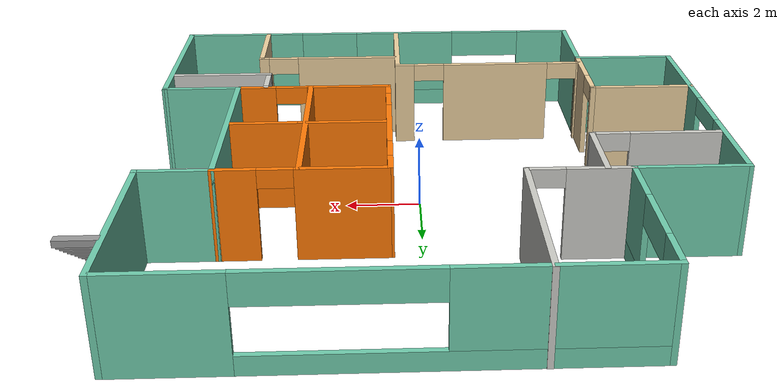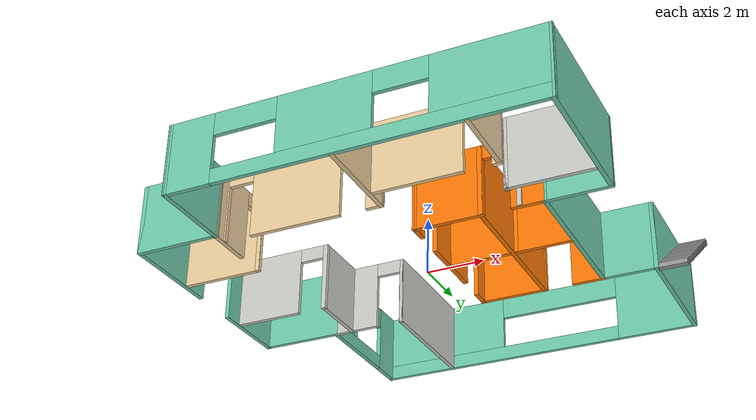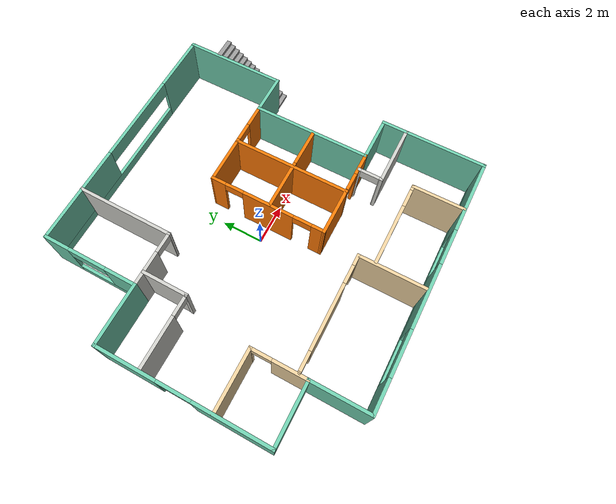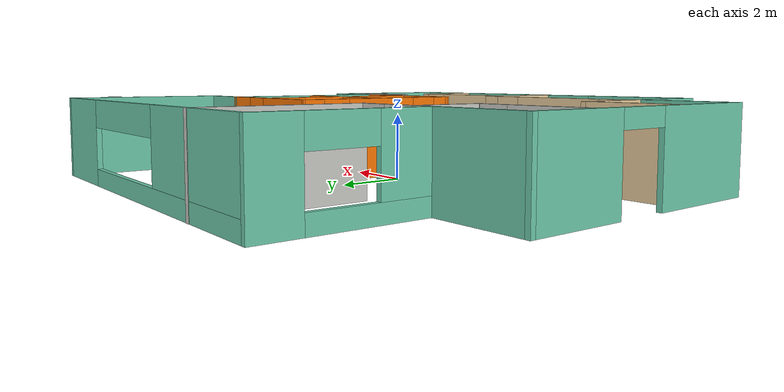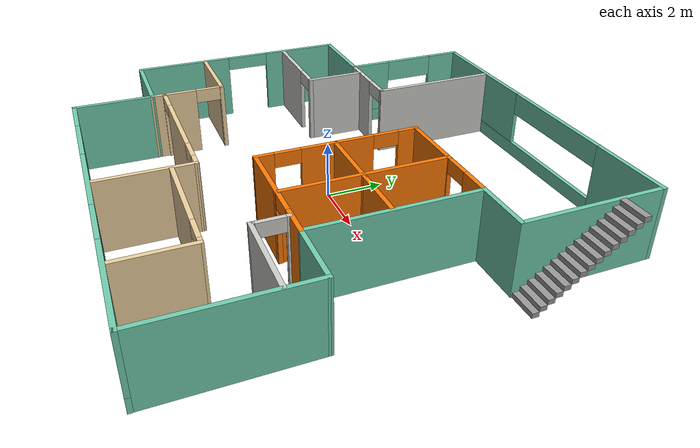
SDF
<?xml version='1.0'?>
<sdf version='1.6'>
  <model name='Building'>
    <link name='Stairs_0'>
      <pose frame=''>0 0 0 0 -0 0</pose>
      <self_collide>0</self_collide>
      <kinematic>0</kinematic>
      <visual name='Stairs_0_Visual_0'>
        <pose frame=''>7.53348 2.95514 0.083333 0 0 -3.14159</pose>
        <geometry>
          <box>
            <size>1 0.231704 0.166667</size>
          </box>
        </geometry>
        <material>
          <script>
            <uri>file://media/materials/scripts/gazebo.material</uri>
            <name>Gazebo/Grey</name>
          </script>
          <ambient>1 1 1 1</ambient>
          <shader type='pixel'/>
          <diffuse>0.7 0.7 0.7 1</diffuse>
          <specular>0.01 0.01 0.01 1</specular>
          <emissive>0 0 0 1</emissive>
        </material>
        <meta>
          <layer>0</layer>
        </meta>
        <transparency>0</transparency>
        <cast_shadows>1</cast_shadows>
      </visual>
      <visual name='Stairs_0_Visual_1'>
        <pose frame=''>7.53348 3.18685 0.25 0 0 -3.14159</pose>
        <geometry>
          <box>
            <size>1 0.231704 0.166667</size>
          </box>
        </geometry>
        <material>
          <script>
            <uri>file://media/materials/scripts/gazebo.material</uri>
            <name>Gazebo/Grey</name>
          </script>
          <ambient>1 1 1 1</ambient>
          <shader type='pixel'/>
          <diffuse>0.7 0.7 0.7 1</diffuse>
          <specular>0.01 0.01 0.01 1</specular>
          <emissive>0 0 0 1</emissive>
        </material>
        <meta>
          <layer>0</layer>
        </meta>
        <transparency>0</transparency>
        <cast_shadows>1</cast_shadows>
      </visual>
      <visual name='Stairs_0_Visual_2'>
        <pose frame=''>7.53348 3.41855 0.416667 0 0 -3.14159</pose>
        <geometry>
          <box>
            <size>1 0.231704 0.166667</size>
          </box>
        </geometry>
        <material>
          <script>
            <uri>file://media/materials/scripts/gazebo.material</uri>
            <name>Gazebo/Grey</name>
          </script>
          <ambient>1 1 1 1</ambient>
          <shader type='pixel'/>
          <diffuse>0.7 0.7 0.7 1</diffuse>
          <specular>0.01 0.01 0.01 1</specular>
          <emissive>0 0 0 1</emissive>
        </material>
        <meta>
          <layer>0</layer>
        </meta>
        <transparency>0</transparency>
        <cast_shadows>1</cast_shadows>
      </visual>
      <visual name='Stairs_0_Visual_3'>
        <pose frame=''>7.53348 3.65026 0.583333 0 0 -3.14159</pose>
        <geometry>
          <box>
            <size>1 0.231704 0.166667</size>
          </box>
        </geometry>
        <material>
          <script>
            <uri>file://media/materials/scripts/gazebo.material</uri>
            <name>Gazebo/Grey</name>
          </script>
          <ambient>1 1 1 1</ambient>
          <shader type='pixel'/>
          <diffuse>0.7 0.7 0.7 1</diffuse>
          <specular>0.01 0.01 0.01 1</specular>
          <emissive>0 0 0 1</emissive>
        </material>
        <meta>
          <layer>0</layer>
        </meta>
        <transparency>0</transparency>
        <cast_shadows>1</cast_shadows>
      </visual>
      <visual name='Stairs_0_Visual_4'>
        <pose frame=''>7.53348 3.88196 0.75 0 0 -3.14159</pose>
        <geometry>
          <box>
            <size>1 0.231704 0.166667</size>
          </box>
        </geometry>
        <material>
          <script>
            <uri>file://media/materials/scripts/gazebo.material</uri>
            <name>Gazebo/Grey</name>
          </script>
          <ambient>1 1 1 1</ambient>
          <shader type='pixel'/>
          <diffuse>0.7 0.7 0.7 1</diffuse>
          <specular>0.01 0.01 0.01 1</specular>
          <emissive>0 0 0 1</emissive>
        </material>
        <meta>
          <layer>0</layer>
        </meta>
        <transparency>0</transparency>
        <cast_shadows>1</cast_shadows>
      </visual>
      <visual name='Stairs_0_Visual_5'>
        <pose frame=''>7.53348 4.11367 0.916667 0 0 -3.14159</pose>
        <geometry>
          <box>
            <size>1 0.231704 0.166667</size>
          </box>
        </geometry>
        <material>
          <script>
            <uri>file://media/materials/scripts/gazebo.material</uri>
            <name>Gazebo/Grey</name>
          </script>
          <ambient>1 1 1 1</ambient>
          <shader type='pixel'/>
          <diffuse>0.7 0.7 0.7 1</diffuse>
          <specular>0.01 0.01 0.01 1</specular>
          <emissive>0 0 0 1</emissive>
        </material>
        <meta>
          <layer>0</layer>
        </meta>
        <transparency>0</transparency>
        <cast_shadows>1</cast_shadows>
      </visual>
      <visual name='Stairs_0_Visual_6'>
        <pose frame=''>7.53348 4.34537 1.08333 0 0 -3.14159</pose>
        <geometry>
          <box>
            <size>1 0.231704 0.166667</size>
          </box>
        </geometry>
        <material>
          <script>
            <uri>file://media/materials/scripts/gazebo.material</uri>
            <name>Gazebo/Grey</name>
          </script>
          <ambient>1 1 1 1</ambient>
          <shader type='pixel'/>
          <diffuse>0.7 0.7 0.7 1</diffuse>
          <specular>0.01 0.01 0.01 1</specular>
          <emissive>0 0 0 1</emissive>
        </material>
        <meta>
          <layer>0</layer>
        </meta>
        <transparency>0</transparency>
        <cast_shadows>1</cast_shadows>
      </visual>
      <visual name='Stairs_0_Visual_7'>
        <pose frame=''>7.53348 4.57708 1.25 0 0 -3.14159</pose>
        <geometry>
          <box>
            <size>1 0.231704 0.166667</size>
          </box>
        </geometry>
        <material>
          <script>
            <uri>file://media/materials/scripts/gazebo.material</uri>
            <name>Gazebo/Grey</name>
          </script>
          <ambient>1 1 1 1</ambient>
          <shader type='pixel'/>
          <diffuse>0.7 0.7 0.7 1</diffuse>
          <specular>0.01 0.01 0.01 1</specular>
          <emissive>0 0 0 1</emissive>
        </material>
        <meta>
          <layer>0</layer>
        </meta>
        <transparency>0</transparency>
        <cast_shadows>1</cast_shadows>
      </visual>
      <visual name='Stairs_0_Visual_8'>
        <pose frame=''>7.53348 4.80878 1.41667 0 0 -3.14159</pose>
        <geometry>
          <box>
            <size>1 0.231704 0.166667</size>
          </box>
        </geometry>
        <material>
          <script>
            <uri>file://media/materials/scripts/gazebo.material</uri>
            <name>Gazebo/Grey</name>
          </script>
          <ambient>1 1 1 1</ambient>
          <shader type='pixel'/>
          <diffuse>0.7 0.7 0.7 1</diffuse>
          <specular>0.01 0.01 0.01 1</specular>
          <emissive>0 0 0 1</emissive>
        </material>
        <meta>
          <layer>0</layer>
        </meta>
        <transparency>0</transparency>
        <cast_shadows>1</cast_shadows>
      </visual>
      <visual name='Stairs_0_Visual_9'>
        <pose frame=''>7.53348 5.04049 1.58333 0 0 -3.14159</pose>
        <geometry>
          <box>
            <size>1 0.231704 0.166667</size>
          </box>
        </geometry>
        <material>
          <script>
            <uri>file://media/materials/scripts/gazebo.material</uri>
            <name>Gazebo/Grey</name>
          </script>
          <ambient>1 1 1 1</ambient>
          <shader type='pixel'/>
          <diffuse>0.7 0.7 0.7 1</diffuse>
          <specular>0.01 0.01 0.01 1</specular>
          <emissive>0 0 0 1</emissive>
        </material>
        <meta>
          <layer>0</layer>
        </meta>
        <transparency>0</transparency>
        <cast_shadows>1</cast_shadows>
      </visual>
      <visual name='Stairs_0_Visual_10'>
        <pose frame=''>7.53348 5.27219 1.75 0 0 -3.14159</pose>
        <geometry>
          <box>
            <size>1 0.231704 0.166667</size>
          </box>
        </geometry>
        <material>
          <script>
            <uri>file://media/materials/scripts/gazebo.material</uri>
            <name>Gazebo/Grey</name>
          </script>
          <ambient>1 1 1 1</ambient>
          <shader type='pixel'/>
          <diffuse>0.7 0.7 0.7 1</diffuse>
          <specular>0.01 0.01 0.01 1</specular>
          <emissive>0 0 0 1</emissive>
        </material>
        <meta>
          <layer>0</layer>
        </meta>
        <transparency>0</transparency>
        <cast_shadows>1</cast_shadows>
      </visual>
      <visual name='Stairs_0_Visual_11'>
        <pose frame=''>7.53348 5.50389 1.91667 0 0 -3.14159</pose>
        <geometry>
          <box>
            <size>1 0.231704 0.166667</size>
          </box>
        </geometry>
        <material>
          <script>
            <uri>file://media/materials/scripts/gazebo.material</uri>
            <name>Gazebo/Grey</name>
          </script>
          <ambient>1 1 1 1</ambient>
          <shader type='pixel'/>
          <diffuse>0.7 0.7 0.7 1</diffuse>
          <specular>0.01 0.01 0.01 1</specular>
          <emissive>0 0 0 1</emissive>
        </material>
        <meta>
          <layer>0</layer>
        </meta>
        <transparency>0</transparency>
        <cast_shadows>1</cast_shadows>
      </visual>
      <visual name='Stairs_0_Visual_12'>
        <pose frame=''>7.53348 5.7356 2.08333 0 0 -3.14159</pose>
        <geometry>
          <box>
            <size>1 0.231704 0.166667</size>
          </box>
        </geometry>
        <material>
          <script>
            <uri>file://media/materials/scripts/gazebo.material</uri>
            <name>Gazebo/Grey</name>
          </script>
          <ambient>1 1 1 1</ambient>
          <shader type='pixel'/>
          <diffuse>0.7 0.7 0.7 1</diffuse>
          <specular>0.01 0.01 0.01 1</specular>
          <emissive>0 0 0 1</emissive>
        </material>
        <meta>
          <layer>0</layer>
        </meta>
        <transparency>0</transparency>
        <cast_shadows>1</cast_shadows>
      </visual>
      <visual name='Stairs_0_Visual_13'>
        <pose frame=''>7.53348 5.9673 2.25 0 0 -3.14159</pose>
        <geometry>
          <box>
            <size>1 0.231704 0.166667</size>
          </box>
        </geometry>
        <material>
          <script>
            <uri>file://media/materials/scripts/gazebo.material</uri>
            <name>Gazebo/Grey</name>
          </script>
          <ambient>1 1 1 1</ambient>
          <shader type='pixel'/>
          <diffuse>0.7 0.7 0.7 1</diffuse>
          <specular>0.01 0.01 0.01 1</specular>
          <emissive>0 0 0 1</emissive>
        </material>
        <meta>
          <layer>0</layer>
        </meta>
        <transparency>0</transparency>
        <cast_shadows>1</cast_shadows>
      </visual>
      <visual name='Stairs_0_Visual_14'>
        <pose frame=''>7.53348 6.19901 2.41667 0 0 -3.14159</pose>
        <geometry>
          <box>
            <size>1 0.231704 0.166667</size>
          </box>
        </geometry>
        <material>
          <script>
            <uri>file://media/materials/scripts/gazebo.material</uri>
            <name>Gazebo/Grey</name>
          </script>
          <ambient>1 1 1 1</ambient>
          <shader type='pixel'/>
          <diffuse>0.7 0.7 0.7 1</diffuse>
          <specular>0.01 0.01 0.01 1</specular>
          <emissive>0 0 0 1</emissive>
        </material>
        <meta>
          <layer>0</layer>
        </meta>
        <transparency>0</transparency>
        <cast_shadows>1</cast_shadows>
      </visual>
      <collision name='Stairs_0_Collision_6'>
        <laser_retro>0</laser_retro>
        <max_contacts>10</max_contacts>
        <pose frame=''>7.53348 4.34537 1.08333 0 0 -3.14159</pose>
        <geometry>
          <box>
            <size>1 0.231704 0.166667</size>
          </box>
        </geometry>
        <surface>
          <friction>
            <ode>
              <mu>1</mu>
              <mu2>1</mu2>
              <fdir1>0 0 0</fdir1>
              <slip1>0</slip1>
              <slip2>0</slip2>
            </ode>
            <torsional>
              <coefficient>1</coefficient>
              <patch_radius>0</patch_radius>
              <surface_radius>0</surface_radius>
              <use_patch_radius>1</use_patch_radius>
              <ode>
                <slip>0</slip>
              </ode>
            </torsional>
          </friction>
          <bounce>
            <restitution_coefficient>0</restitution_coefficient>
            <threshold>1e+06</threshold>
          </bounce>
          <contact>
            <collide_without_contact>0</collide_without_contact>
            <collide_without_contact_bitmask>1</collide_without_contact_bitmask>
            <collide_bitmask>1</collide_bitmask>
            <ode>
              <soft_cfm>0</soft_cfm>
              <soft_erp>0.2</soft_erp>
              <kp>1e+13</kp>
              <kd>1</kd>
              <max_vel>0.01</max_vel>
              <min_depth>0</min_depth>
            </ode>
            <bullet>
              <split_impulse>1</split_impulse>
              <split_impulse_penetration_threshold>-0.01</split_impulse_penetration_threshold>
              <soft_cfm>0</soft_cfm>
              <soft_erp>0.2</soft_erp>
              <kp>1e+13</kp>
              <kd>1</kd>
            </bullet>
          </contact>
        </surface>
      </collision>
      <collision name='Stairs_0_Collision_0'>
        <laser_retro>0</laser_retro>
        <max_contacts>10</max_contacts>
        <pose frame=''>7.53348 2.95514 0.083333 0 0 -3.14159</pose>
        <geometry>
          <box>
            <size>1 0.231704 0.166667</size>
          </box>
        </geometry>
        <surface>
          <friction>
            <ode>
              <mu>1</mu>
              <mu2>1</mu2>
              <fdir1>0 0 0</fdir1>
              <slip1>0</slip1>
              <slip2>0</slip2>
            </ode>
            <torsional>
              <coefficient>1</coefficient>
              <patch_radius>0</patch_radius>
              <surface_radius>0</surface_radius>
              <use_patch_radius>1</use_patch_radius>
              <ode>
                <slip>0</slip>
              </ode>
            </torsional>
          </friction>
          <bounce>
            <restitution_coefficient>0</restitution_coefficient>
            <threshold>1e+06</threshold>
          </bounce>
          <contact>
            <collide_without_contact>0</collide_without_contact>
            <collide_without_contact_bitmask>1</collide_without_contact_bitmask>
            <collide_bitmask>1</collide_bitmask>
            <ode>
              <soft_cfm>0</soft_cfm>
              <soft_erp>0.2</soft_erp>
              <kp>1e+13</kp>
              <kd>1</kd>
              <max_vel>0.01</max_vel>
              <min_depth>0</min_depth>
            </ode>
            <bullet>
              <split_impulse>1</split_impulse>
              <split_impulse_penetration_threshold>-0.01</split_impulse_penetration_threshold>
              <soft_cfm>0</soft_cfm>
              <soft_erp>0.2</soft_erp>
              <kp>1e+13</kp>
              <kd>1</kd>
            </bullet>
          </contact>
        </surface>
      </collision>
      <collision name='Stairs_0_Collision_2'>
        <laser_retro>0</laser_retro>
        <max_contacts>10</max_contacts>
        <pose frame=''>7.53348 3.41855 0.416667 0 0 -3.14159</pose>
        <geometry>
          <box>
            <size>1 0.231704 0.166667</size>
          </box>
        </geometry>
        <surface>
          <friction>
            <ode>
              <mu>1</mu>
              <mu2>1</mu2>
              <fdir1>0 0 0</fdir1>
              <slip1>0</slip1>
              <slip2>0</slip2>
            </ode>
            <torsional>
              <coefficient>1</coefficient>
              <patch_radius>0</patch_radius>
              <surface_radius>0</surface_radius>
              <use_patch_radius>1</use_patch_radius>
              <ode>
                <slip>0</slip>
              </ode>
            </torsional>
          </friction>
          <bounce>
            <restitution_coefficient>0</restitution_coefficient>
            <threshold>1e+06</threshold>
          </bounce>
          <contact>
            <collide_without_contact>0</collide_without_contact>
            <collide_without_contact_bitmask>1</collide_without_contact_bitmask>
            <collide_bitmask>1</collide_bitmask>
            <ode>
              <soft_cfm>0</soft_cfm>
              <soft_erp>0.2</soft_erp>
              <kp>1e+13</kp>
              <kd>1</kd>
              <max_vel>0.01</max_vel>
              <min_depth>0</min_depth>
            </ode>
            <bullet>
              <split_impulse>1</split_impulse>
              <split_impulse_penetration_threshold>-0.01</split_impulse_penetration_threshold>
              <soft_cfm>0</soft_cfm>
              <soft_erp>0.2</soft_erp>
              <kp>1e+13</kp>
              <kd>1</kd>
            </bullet>
          </contact>
        </surface>
      </collision>
      <collision name='Stairs_0_Collision_1'>
        <laser_retro>0</laser_retro>
        <max_contacts>10</max_contacts>
        <pose frame=''>7.53348 3.18685 0.25 0 0 -3.14159</pose>
        <geometry>
          <box>
            <size>1 0.231704 0.166667</size>
          </box>
        </geometry>
        <surface>
          <friction>
            <ode>
              <mu>1</mu>
              <mu2>1</mu2>
              <fdir1>0 0 0</fdir1>
              <slip1>0</slip1>
              <slip2>0</slip2>
            </ode>
            <torsional>
              <coefficient>1</coefficient>
              <patch_radius>0</patch_radius>
              <surface_radius>0</surface_radius>
              <use_patch_radius>1</use_patch_radius>
              <ode>
                <slip>0</slip>
              </ode>
            </torsional>
          </friction>
          <bounce>
            <restitution_coefficient>0</restitution_coefficient>
            <threshold>1e+06</threshold>
          </bounce>
          <contact>
            <collide_without_contact>0</collide_without_contact>
            <collide_without_contact_bitmask>1</collide_without_contact_bitmask>
            <collide_bitmask>1</collide_bitmask>
            <ode>
              <soft_cfm>0</soft_cfm>
              <soft_erp>0.2</soft_erp>
              <kp>1e+13</kp>
              <kd>1</kd>
              <max_vel>0.01</max_vel>
              <min_depth>0</min_depth>
            </ode>
            <bullet>
              <split_impulse>1</split_impulse>
              <split_impulse_penetration_threshold>-0.01</split_impulse_penetration_threshold>
              <soft_cfm>0</soft_cfm>
              <soft_erp>0.2</soft_erp>
              <kp>1e+13</kp>
              <kd>1</kd>
            </bullet>
          </contact>
        </surface>
      </collision>
      <collision name='Stairs_0_Collision_4'>
        <laser_retro>0</laser_retro>
        <max_contacts>10</max_contacts>
        <pose frame=''>7.53348 3.88196 0.75 0 0 -3.14159</pose>
        <geometry>
          <box>
            <size>1 0.231704 0.166667</size>
          </box>
        </geometry>
        <surface>
          <friction>
            <ode>
              <mu>1</mu>
              <mu2>1</mu2>
              <fdir1>0 0 0</fdir1>
              <slip1>0</slip1>
              <slip2>0</slip2>
            </ode>
            <torsional>
              <coefficient>1</coefficient>
              <patch_radius>0</patch_radius>
              <surface_radius>0</surface_radius>
              <use_patch_radius>1</use_patch_radius>
              <ode>
                <slip>0</slip>
              </ode>
            </torsional>
          </friction>
          <bounce>
            <restitution_coefficient>0</restitution_coefficient>
            <threshold>1e+06</threshold>
          </bounce>
          <contact>
            <collide_without_contact>0</collide_without_contact>
            <collide_without_contact_bitmask>1</collide_without_contact_bitmask>
            <collide_bitmask>1</collide_bitmask>
            <ode>
              <soft_cfm>0</soft_cfm>
              <soft_erp>0.2</soft_erp>
              <kp>1e+13</kp>
              <kd>1</kd>
              <max_vel>0.01</max_vel>
              <min_depth>0</min_depth>
            </ode>
            <bullet>
              <split_impulse>1</split_impulse>
              <split_impulse_penetration_threshold>-0.01</split_impulse_penetration_threshold>
              <soft_cfm>0</soft_cfm>
              <soft_erp>0.2</soft_erp>
              <kp>1e+13</kp>
              <kd>1</kd>
            </bullet>
          </contact>
        </surface>
      </collision>
      <collision name='Stairs_0_Collision_3'>
        <laser_retro>0</laser_retro>
        <max_contacts>10</max_contacts>
        <pose frame=''>7.53348 3.65026 0.583333 0 0 -3.14159</pose>
        <geometry>
          <box>
            <size>1 0.231704 0.166667</size>
          </box>
        </geometry>
        <surface>
          <friction>
            <ode>
              <mu>1</mu>
              <mu2>1</mu2>
              <fdir1>0 0 0</fdir1>
              <slip1>0</slip1>
              <slip2>0</slip2>
            </ode>
            <torsional>
              <coefficient>1</coefficient>
              <patch_radius>0</patch_radius>
              <surface_radius>0</surface_radius>
              <use_patch_radius>1</use_patch_radius>
              <ode>
                <slip>0</slip>
              </ode>
            </torsional>
          </friction>
          <bounce>
            <restitution_coefficient>0</restitution_coefficient>
            <threshold>1e+06</threshold>
          </bounce>
          <contact>
            <collide_without_contact>0</collide_without_contact>
            <collide_without_contact_bitmask>1</collide_without_contact_bitmask>
            <collide_bitmask>1</collide_bitmask>
            <ode>
              <soft_cfm>0</soft_cfm>
              <soft_erp>0.2</soft_erp>
              <kp>1e+13</kp>
              <kd>1</kd>
              <max_vel>0.01</max_vel>
              <min_depth>0</min_depth>
            </ode>
            <bullet>
              <split_impulse>1</split_impulse>
              <split_impulse_penetration_threshold>-0.01</split_impulse_penetration_threshold>
              <soft_cfm>0</soft_cfm>
              <soft_erp>0.2</soft_erp>
              <kp>1e+13</kp>
              <kd>1</kd>
            </bullet>
          </contact>
        </surface>
      </collision>
      <collision name='Stairs_0_Collision_5'>
        <laser_retro>0</laser_retro>
        <max_contacts>10</max_contacts>
        <pose frame=''>7.53348 4.11367 0.916667 0 0 -3.14159</pose>
        <geometry>
          <box>
            <size>1 0.231704 0.166667</size>
          </box>
        </geometry>
        <surface>
          <friction>
            <ode>
              <mu>1</mu>
              <mu2>1</mu2>
              <fdir1>0 0 0</fdir1>
              <slip1>0</slip1>
              <slip2>0</slip2>
            </ode>
            <torsional>
              <coefficient>1</coefficient>
              <patch_radius>0</patch_radius>
              <surface_radius>0</surface_radius>
              <use_patch_radius>1</use_patch_radius>
              <ode>
                <slip>0</slip>
              </ode>
            </torsional>
          </friction>
          <bounce>
            <restitution_coefficient>0</restitution_coefficient>
            <threshold>1e+06</threshold>
          </bounce>
          <contact>
            <collide_without_contact>0</collide_without_contact>
            <collide_without_contact_bitmask>1</collide_without_contact_bitmask>
            <collide_bitmask>1</collide_bitmask>
            <ode>
              <soft_cfm>0</soft_cfm>
              <soft_erp>0.2</soft_erp>
              <kp>1e+13</kp>
              <kd>1</kd>
              <max_vel>0.01</max_vel>
              <min_depth>0</min_depth>
            </ode>
            <bullet>
              <split_impulse>1</split_impulse>
              <split_impulse_penetration_threshold>-0.01</split_impulse_penetration_threshold>
              <soft_cfm>0</soft_cfm>
              <soft_erp>0.2</soft_erp>
              <kp>1e+13</kp>
              <kd>1</kd>
            </bullet>
          </contact>
        </surface>
      </collision>
      <collision name='Stairs_0_Collision_8'>
        <laser_retro>0</laser_retro>
        <max_contacts>10</max_contacts>
        <pose frame=''>7.53348 4.80878 1.41667 0 0 -3.14159</pose>
        <geometry>
          <box>
            <size>1 0.231704 0.166667</size>
          </box>
        </geometry>
        <surface>
          <friction>
            <ode>
              <mu>1</mu>
              <mu2>1</mu2>
              <fdir1>0 0 0</fdir1>
              <slip1>0</slip1>
              <slip2>0</slip2>
            </ode>
            <torsional>
              <coefficient>1</coefficient>
              <patch_radius>0</patch_radius>
              <surface_radius>0</surface_radius>
              <use_patch_radius>1</use_patch_radius>
              <ode>
                <slip>0</slip>
              </ode>
            </torsional>
          </friction>
          <bounce>
            <restitution_coefficient>0</restitution_coefficient>
            <threshold>1e+06</threshold>
          </bounce>
          <contact>
            <collide_without_contact>0</collide_without_contact>
            <collide_without_contact_bitmask>1</collide_without_contact_bitmask>
            <collide_bitmask>1</collide_bitmask>
            <ode>
              <soft_cfm>0</soft_cfm>
              <soft_erp>0.2</soft_erp>
              <kp>1e+13</kp>
              <kd>1</kd>
              <max_vel>0.01</max_vel>
              <min_depth>0</min_depth>
            </ode>
            <bullet>
              <split_impulse>1</split_impulse>
              <split_impulse_penetration_threshold>-0.01</split_impulse_penetration_threshold>
              <soft_cfm>0</soft_cfm>
              <soft_erp>0.2</soft_erp>
              <kp>1e+13</kp>
              <kd>1</kd>
            </bullet>
          </contact>
        </surface>
      </collision>
      <collision name='Stairs_0_Collision_7'>
        <laser_retro>0</laser_retro>
        <max_contacts>10</max_contacts>
        <pose frame=''>7.53348 4.57708 1.25 0 0 -3.14159</pose>
        <geometry>
          <box>
            <size>1 0.231704 0.166667</size>
          </box>
        </geometry>
        <surface>
          <friction>
            <ode>
              <mu>1</mu>
              <mu2>1</mu2>
              <fdir1>0 0 0</fdir1>
              <slip1>0</slip1>
              <slip2>0</slip2>
            </ode>
            <torsional>
              <coefficient>1</coefficient>
              <patch_radius>0</patch_radius>
              <surface_radius>0</surface_radius>
              <use_patch_radius>1</use_patch_radius>
              <ode>
                <slip>0</slip>
              </ode>
            </torsional>
          </friction>
          <bounce>
            <restitution_coefficient>0</restitution_coefficient>
            <threshold>1e+06</threshold>
          </bounce>
          <contact>
            <collide_without_contact>0</collide_without_contact>
            <collide_without_contact_bitmask>1</collide_without_contact_bitmask>
            <collide_bitmask>1</collide_bitmask>
            <ode>
              <soft_cfm>0</soft_cfm>
              <soft_erp>0.2</soft_erp>
              <kp>1e+13</kp>
              <kd>1</kd>
              <max_vel>0.01</max_vel>
              <min_depth>0</min_depth>
            </ode>
            <bullet>
              <split_impulse>1</split_impulse>
              <split_impulse_penetration_threshold>-0.01</split_impulse_penetration_threshold>
              <soft_cfm>0</soft_cfm>
              <soft_erp>0.2</soft_erp>
              <kp>1e+13</kp>
              <kd>1</kd>
            </bullet>
          </contact>
        </surface>
      </collision>
      <collision name='Stairs_0_Collision_9'>
        <laser_retro>0</laser_retro>
        <max_contacts>10</max_contacts>
        <pose frame=''>7.53348 5.04049 1.58333 0 0 -3.14159</pose>
        <geometry>
          <box>
            <size>1 0.231704 0.166667</size>
          </box>
        </geometry>
        <surface>
          <friction>
            <ode>
              <mu>1</mu>
              <mu2>1</mu2>
              <fdir1>0 0 0</fdir1>
              <slip1>0</slip1>
              <slip2>0</slip2>
            </ode>
            <torsional>
              <coefficient>1</coefficient>
              <patch_radius>0</patch_radius>
              <surface_radius>0</surface_radius>
              <use_patch_radius>1</use_patch_radius>
              <ode>
                <slip>0</slip>
              </ode>
            </torsional>
          </friction>
          <bounce>
            <restitution_coefficient>0</restitution_coefficient>
            <threshold>1e+06</threshold>
          </bounce>
          <contact>
            <collide_without_contact>0</collide_without_contact>
            <collide_without_contact_bitmask>1</collide_without_contact_bitmask>
            <collide_bitmask>1</collide_bitmask>
            <ode>
              <soft_cfm>0</soft_cfm>
              <soft_erp>0.2</soft_erp>
              <kp>1e+13</kp>
              <kd>1</kd>
              <max_vel>0.01</max_vel>
              <min_depth>0</min_depth>
            </ode>
            <bullet>
              <split_impulse>1</split_impulse>
              <split_impulse_penetration_threshold>-0.01</split_impulse_penetration_threshold>
              <soft_cfm>0</soft_cfm>
              <soft_erp>0.2</soft_erp>
              <kp>1e+13</kp>
              <kd>1</kd>
            </bullet>
          </contact>
        </surface>
      </collision>
      <collision name='Stairs_0_Collision_10'>
        <laser_retro>0</laser_retro>
        <max_contacts>10</max_contacts>
        <pose frame=''>7.53348 5.27219 1.75 0 0 -3.14159</pose>
        <geometry>
          <box>
            <size>1 0.231704 0.166667</size>
          </box>
        </geometry>
        <surface>
          <friction>
            <ode>
              <mu>1</mu>
              <mu2>1</mu2>
              <fdir1>0 0 0</fdir1>
              <slip1>0</slip1>
              <slip2>0</slip2>
            </ode>
            <torsional>
              <coefficient>1</coefficient>
              <patch_radius>0</patch_radius>
              <surface_radius>0</surface_radius>
              <use_patch_radius>1</use_patch_radius>
              <ode>
                <slip>0</slip>
              </ode>
            </torsional>
          </friction>
          <bounce>
            <restitution_coefficient>0</restitution_coefficient>
            <threshold>1e+06</threshold>
          </bounce>
          <contact>
            <collide_without_contact>0</collide_without_contact>
            <collide_without_contact_bitmask>1</collide_without_contact_bitmask>
            <collide_bitmask>1</collide_bitmask>
            <ode>
              <soft_cfm>0</soft_cfm>
              <soft_erp>0.2</soft_erp>
              <kp>1e+13</kp>
              <kd>1</kd>
              <max_vel>0.01</max_vel>
              <min_depth>0</min_depth>
            </ode>
            <bullet>
              <split_impulse>1</split_impulse>
              <split_impulse_penetration_threshold>-0.01</split_impulse_penetration_threshold>
              <soft_cfm>0</soft_cfm>
              <soft_erp>0.2</soft_erp>
              <kp>1e+13</kp>
              <kd>1</kd>
            </bullet>
          </contact>
        </surface>
      </collision>
      <collision name='Stairs_0_Collision_11'>
        <laser_retro>0</laser_retro>
        <max_contacts>10</max_contacts>
        <pose frame=''>7.53348 5.50389 1.91667 0 0 -3.14159</pose>
        <geometry>
          <box>
            <size>1 0.231704 0.166667</size>
          </box>
        </geometry>
        <surface>
          <friction>
            <ode>
              <mu>1</mu>
              <mu2>1</mu2>
              <fdir1>0 0 0</fdir1>
              <slip1>0</slip1>
              <slip2>0</slip2>
            </ode>
            <torsional>
              <coefficient>1</coefficient>
              <patch_radius>0</patch_radius>
              <surface_radius>0</surface_radius>
              <use_patch_radius>1</use_patch_radius>
              <ode>
                <slip>0</slip>
              </ode>
            </torsional>
          </friction>
          <bounce>
            <restitution_coefficient>0</restitution_coefficient>
            <threshold>1e+06</threshold>
          </bounce>
          <contact>
            <collide_without_contact>0</collide_without_contact>
            <collide_without_contact_bitmask>1</collide_without_contact_bitmask>
            <collide_bitmask>1</collide_bitmask>
            <ode>
              <soft_cfm>0</soft_cfm>
              <soft_erp>0.2</soft_erp>
              <kp>1e+13</kp>
              <kd>1</kd>
              <max_vel>0.01</max_vel>
              <min_depth>0</min_depth>
            </ode>
            <bullet>
              <split_impulse>1</split_impulse>
              <split_impulse_penetration_threshold>-0.01</split_impulse_penetration_threshold>
              <soft_cfm>0</soft_cfm>
              <soft_erp>0.2</soft_erp>
              <kp>1e+13</kp>
              <kd>1</kd>
            </bullet>
          </contact>
        </surface>
      </collision>
      <collision name='Stairs_0_Collision_12'>
        <laser_retro>0</laser_retro>
        <max_contacts>10</max_contacts>
        <pose frame=''>7.53348 5.7356 2.08333 0 0 -3.14159</pose>
        <geometry>
          <box>
            <size>1 0.231704 0.166667</size>
          </box>
        </geometry>
        <surface>
          <friction>
            <ode>
              <mu>1</mu>
              <mu2>1</mu2>
              <fdir1>0 0 0</fdir1>
              <slip1>0</slip1>
              <slip2>0</slip2>
            </ode>
            <torsional>
              <coefficient>1</coefficient>
              <patch_radius>0</patch_radius>
              <surface_radius>0</surface_radius>
              <use_patch_radius>1</use_patch_radius>
              <ode>
                <slip>0</slip>
              </ode>
            </torsional>
          </friction>
          <bounce>
            <restitution_coefficient>0</restitution_coefficient>
            <threshold>1e+06</threshold>
          </bounce>
          <contact>
            <collide_without_contact>0</collide_without_contact>
            <collide_without_contact_bitmask>1</collide_without_contact_bitmask>
            <collide_bitmask>1</collide_bitmask>
            <ode>
              <soft_cfm>0</soft_cfm>
              <soft_erp>0.2</soft_erp>
              <kp>1e+13</kp>
              <kd>1</kd>
              <max_vel>0.01</max_vel>
              <min_depth>0</min_depth>
            </ode>
            <bullet>
              <split_impulse>1</split_impulse>
              <split_impulse_penetration_threshold>-0.01</split_impulse_penetration_threshold>
              <soft_cfm>0</soft_cfm>
              <soft_erp>0.2</soft_erp>
              <kp>1e+13</kp>
              <kd>1</kd>
            </bullet>
          </contact>
        </surface>
      </collision>
      <collision name='Stairs_0_Collision_14'>
        <laser_retro>0</laser_retro>
        <max_contacts>10</max_contacts>
        <pose frame=''>7.53348 6.19901 2.41667 0 0 -3.14159</pose>
        <geometry>
          <box>
            <size>1 0.231704 0.166667</size>
          </box>
        </geometry>
        <surface>
          <friction>
            <ode>
              <mu>1</mu>
              <mu2>1</mu2>
              <fdir1>0 0 0</fdir1>
              <slip1>0</slip1>
              <slip2>0</slip2>
            </ode>
            <torsional>
              <coefficient>1</coefficient>
              <patch_radius>0</patch_radius>
              <surface_radius>0</surface_radius>
              <use_patch_radius>1</use_patch_radius>
              <ode>
                <slip>0</slip>
              </ode>
            </torsional>
          </friction>
          <bounce>
            <restitution_coefficient>0</restitution_coefficient>
            <threshold>1e+06</threshold>
          </bounce>
          <contact>
            <collide_without_contact>0</collide_without_contact>
            <collide_without_contact_bitmask>1</collide_without_contact_bitmask>
            <collide_bitmask>1</collide_bitmask>
            <ode>
              <soft_cfm>0</soft_cfm>
              <soft_erp>0.2</soft_erp>
              <kp>1e+13</kp>
              <kd>1</kd>
              <max_vel>0.01</max_vel>
              <min_depth>0</min_depth>
            </ode>
            <bullet>
              <split_impulse>1</split_impulse>
              <split_impulse_penetration_threshold>-0.01</split_impulse_penetration_threshold>
              <soft_cfm>0</soft_cfm>
              <soft_erp>0.2</soft_erp>
              <kp>1e+13</kp>
              <kd>1</kd>
            </bullet>
          </contact>
        </surface>
      </collision>
      <collision name='Stairs_0_Collision_13'>
        <laser_retro>0</laser_retro>
        <max_contacts>10</max_contacts>
        <pose frame=''>7.53348 5.9673 2.25 0 0 -3.14159</pose>
        <geometry>
          <box>
            <size>1 0.231704 0.166667</size>
          </box>
        </geometry>
        <surface>
          <friction>
            <ode>
              <mu>1</mu>
              <mu2>1</mu2>
              <fdir1>0 0 0</fdir1>
              <slip1>0</slip1>
              <slip2>0</slip2>
            </ode>
            <torsional>
              <coefficient>1</coefficient>
              <patch_radius>0</patch_radius>
              <surface_radius>0</surface_radius>
              <use_patch_radius>1</use_patch_radius>
              <ode>
                <slip>0</slip>
              </ode>
            </torsional>
          </friction>
          <bounce>
            <restitution_coefficient>0</restitution_coefficient>
            <threshold>1e+06</threshold>
          </bounce>
          <contact>
            <collide_without_contact>0</collide_without_contact>
            <collide_without_contact_bitmask>1</collide_without_contact_bitmask>
            <collide_bitmask>1</collide_bitmask>
            <ode>
              <soft_cfm>0</soft_cfm>
              <soft_erp>0.2</soft_erp>
              <kp>1e+13</kp>
              <kd>1</kd>
              <max_vel>0.01</max_vel>
              <min_depth>0</min_depth>
            </ode>
            <bullet>
              <split_impulse>1</split_impulse>
              <split_impulse_penetration_threshold>-0.01</split_impulse_penetration_threshold>
              <soft_cfm>0</soft_cfm>
              <soft_erp>0.2</soft_erp>
              <kp>1e+13</kp>
              <kd>1</kd>
            </bullet>
          </contact>
        </surface>
      </collision>
    </link>
    <link name='Wall_10'>
      <pose frame=''>6.19158 -2.73169 0 0 -0 3.14159</pose>
      <self_collide>0</self_collide>
      <kinematic>0</kinematic>
      <visual name='Wall_10_Visual'>
        <pose frame=''>0 0 1.25 0 -0 0</pose>
        <geometry>
          <box>
            <size>2.25 0.15 2.5</size>
          </box>
        </geometry>
        <material>
          <script>
            <uri>file://media/materials/scripts/gazebo.material</uri>
            <name>Gazebo/Grey</name>
          </script>
          <ambient>0.435294 0.796078 0.67451 1</ambient>
          <shader type='pixel'/>
          <diffuse>0.7 0.7 0.7 1</diffuse>
          <specular>0.01 0.01 0.01 1</specular>
          <emissive>0 0 0 1</emissive>
        </material>
        <meta>
          <layer>0</layer>
        </meta>
        <transparency>0</transparency>
        <cast_shadows>1</cast_shadows>
      </visual>
      <collision name='Wall_10_Collision'>
        <laser_retro>0</laser_retro>
        <max_contacts>10</max_contacts>
        <pose frame=''>0 0 1.25 0 -0 0</pose>
        <geometry>
          <box>
            <size>2.25 0.15 2.5</size>
          </box>
        </geometry>
        <surface>
          <friction>
            <ode>
              <mu>1</mu>
              <mu2>1</mu2>
              <fdir1>0 0 0</fdir1>
              <slip1>0</slip1>
              <slip2>0</slip2>
            </ode>
            <torsional>
              <coefficient>1</coefficient>
              <patch_radius>0</patch_radius>
              <surface_radius>0</surface_radius>
              <use_patch_radius>1</use_patch_radius>
              <ode>
                <slip>0</slip>
              </ode>
            </torsional>
          </friction>
          <bounce>
            <restitution_coefficient>0</restitution_coefficient>
            <threshold>1e+06</threshold>
          </bounce>
          <contact>
            <collide_without_contact>0</collide_without_contact>
            <collide_without_contact_bitmask>1</collide_without_contact_bitmask>
            <collide_bitmask>1</collide_bitmask>
            <ode>
              <soft_cfm>0</soft_cfm>
              <soft_erp>0.2</soft_erp>
              <kp>1e+13</kp>
              <kd>1</kd>
              <max_vel>0.01</max_vel>
              <min_depth>0</min_depth>
            </ode>
            <bullet>
              <split_impulse>1</split_impulse>
              <split_impulse_penetration_threshold>-0.01</split_impulse_penetration_threshold>
              <soft_cfm>0</soft_cfm>
              <soft_erp>0.2</soft_erp>
              <kp>1e+13</kp>
              <kd>1</kd>
            </bullet>
          </contact>
        </surface>
      </collision>
    </link>
    <link name='Wall_11'>
      <pose frame=''>5.14158 0.068309 0 0 -0 1.5708</pose>
      <self_collide>0</self_collide>
      <kinematic>0</kinematic>
      <visual name='Wall_11_Visual'>
        <pose frame=''>0 0 1.25 0 -0 0</pose>
        <geometry>
          <box>
            <size>5.75 0.15 2.5</size>
          </box>
        </geometry>
        <material>
          <script>
            <uri>file://media/materials/scripts/gazebo.material</uri>
            <name>Gazebo/Grey</name>
          </script>
          <ambient>0.435294 0.796078 0.67451 1</ambient>
          <shader type='pixel'/>
          <diffuse>0.7 0.7 0.7 1</diffuse>
          <specular>0.01 0.01 0.01 1</specular>
          <emissive>0 0 0 1</emissive>
        </material>
        <meta>
          <layer>0</layer>
        </meta>
        <transparency>0</transparency>
        <cast_shadows>1</cast_shadows>
      </visual>
      <collision name='Wall_11_Collision'>
        <laser_retro>0</laser_retro>
        <max_contacts>10</max_contacts>
        <pose frame=''>0 0 1.25 0 -0 0</pose>
        <geometry>
          <box>
            <size>5.75 0.15 2.5</size>
          </box>
        </geometry>
        <surface>
          <friction>
            <ode>
              <mu>1</mu>
              <mu2>1</mu2>
              <fdir1>0 0 0</fdir1>
              <slip1>0</slip1>
              <slip2>0</slip2>
            </ode>
            <torsional>
              <coefficient>1</coefficient>
              <patch_radius>0</patch_radius>
              <surface_radius>0</surface_radius>
              <use_patch_radius>1</use_patch_radius>
              <ode>
                <slip>0</slip>
              </ode>
            </torsional>
          </friction>
          <bounce>
            <restitution_coefficient>0</restitution_coefficient>
            <threshold>1e+06</threshold>
          </bounce>
          <contact>
            <collide_without_contact>0</collide_without_contact>
            <collide_without_contact_bitmask>1</collide_without_contact_bitmask>
            <collide_bitmask>1</collide_bitmask>
            <ode>
              <soft_cfm>0</soft_cfm>
              <soft_erp>0.2</soft_erp>
              <kp>1e+13</kp>
              <kd>1</kd>
              <max_vel>0.01</max_vel>
              <min_depth>0</min_depth>
            </ode>
            <bullet>
              <split_impulse>1</split_impulse>
              <split_impulse_penetration_threshold>-0.01</split_impulse_penetration_threshold>
              <soft_cfm>0</soft_cfm>
              <soft_erp>0.2</soft_erp>
              <kp>1e+13</kp>
              <kd>1</kd>
            </bullet>
          </contact>
        </surface>
      </collision>
    </link>
    <link name='Wall_12'>
      <pose frame=''>6.06658 2.86831 0 0 -0 0</pose>
      <self_collide>0</self_collide>
      <kinematic>0</kinematic>
      <visual name='Wall_12_Visual'>
        <pose frame=''>0 0 1.25 0 -0 0</pose>
        <geometry>
          <box>
            <size>2 0.15 2.5</size>
          </box>
        </geometry>
        <material>
          <script>
            <uri>file://media/materials/scripts/gazebo.material</uri>
            <name>Gazebo/Grey</name>
          </script>
          <ambient>0.435294 0.796078 0.67451 1</ambient>
          <shader type='pixel'/>
          <diffuse>0.7 0.7 0.7 1</diffuse>
          <specular>0.01 0.01 0.01 1</specular>
          <emissive>0 0 0 1</emissive>
        </material>
        <meta>
          <layer>0</layer>
        </meta>
        <transparency>0</transparency>
        <cast_shadows>1</cast_shadows>
      </visual>
      <collision name='Wall_12_Collision'>
        <laser_retro>0</laser_retro>
        <max_contacts>10</max_contacts>
        <pose frame=''>0 0 1.25 0 -0 0</pose>
        <geometry>
          <box>
            <size>2 0.15 2.5</size>
          </box>
        </geometry>
        <surface>
          <friction>
            <ode>
              <mu>1</mu>
              <mu2>1</mu2>
              <fdir1>0 0 0</fdir1>
              <slip1>0</slip1>
              <slip2>0</slip2>
            </ode>
            <torsional>
              <coefficient>1</coefficient>
              <patch_radius>0</patch_radius>
              <surface_radius>0</surface_radius>
              <use_patch_radius>1</use_patch_radius>
              <ode>
                <slip>0</slip>
              </ode>
            </torsional>
          </friction>
          <bounce>
            <restitution_coefficient>0</restitution_coefficient>
            <threshold>1e+06</threshold>
          </bounce>
          <contact>
            <collide_without_contact>0</collide_without_contact>
            <collide_without_contact_bitmask>1</collide_without_contact_bitmask>
            <collide_bitmask>1</collide_bitmask>
            <ode>
              <soft_cfm>0</soft_cfm>
              <soft_erp>0.2</soft_erp>
              <kp>1e+13</kp>
              <kd>1</kd>
              <max_vel>0.01</max_vel>
              <min_depth>0</min_depth>
            </ode>
            <bullet>
              <split_impulse>1</split_impulse>
              <split_impulse_penetration_threshold>-0.01</split_impulse_penetration_threshold>
              <soft_cfm>0</soft_cfm>
              <soft_erp>0.2</soft_erp>
              <kp>1e+13</kp>
              <kd>1</kd>
            </bullet>
          </contact>
        </surface>
      </collision>
    </link>
    <link name='Wall_13'>
      <pose frame=''>6.99158 5.29331 0 0 -0 1.5708</pose>
      <self_collide>0</self_collide>
      <kinematic>0</kinematic>
      <visual name='Wall_13_Visual'>
        <pose frame=''>0 0 1.25 0 -0 0</pose>
        <geometry>
          <box>
            <size>5 0.15 2.5</size>
          </box>
        </geometry>
        <material>
          <script>
            <uri>file://media/materials/scripts/gazebo.material</uri>
            <name>Gazebo/Grey</name>
          </script>
          <ambient>0.435294 0.796078 0.67451 1</ambient>
          <shader type='pixel'/>
          <diffuse>0.7 0.7 0.7 1</diffuse>
          <specular>0.01 0.01 0.01 1</specular>
          <emissive>0 0 0 1</emissive>
        </material>
        <meta>
          <layer>0</layer>
        </meta>
        <transparency>0</transparency>
        <cast_shadows>1</cast_shadows>
      </visual>
      <collision name='Wall_13_Collision'>
        <laser_retro>0</laser_retro>
        <max_contacts>10</max_contacts>
        <pose frame=''>0 0 1.25 0 -0 0</pose>
        <geometry>
          <box>
            <size>5 0.15 2.5</size>
          </box>
        </geometry>
        <surface>
          <friction>
            <ode>
              <mu>1</mu>
              <mu2>1</mu2>
              <fdir1>0 0 0</fdir1>
              <slip1>0</slip1>
              <slip2>0</slip2>
            </ode>
            <torsional>
              <coefficient>1</coefficient>
              <patch_radius>0</patch_radius>
              <surface_radius>0</surface_radius>
              <use_patch_radius>1</use_patch_radius>
              <ode>
                <slip>0</slip>
              </ode>
            </torsional>
          </friction>
          <bounce>
            <restitution_coefficient>0</restitution_coefficient>
            <threshold>1e+06</threshold>
          </bounce>
          <contact>
            <collide_without_contact>0</collide_without_contact>
            <collide_without_contact_bitmask>1</collide_without_contact_bitmask>
            <collide_bitmask>1</collide_bitmask>
            <ode>
              <soft_cfm>0</soft_cfm>
              <soft_erp>0.2</soft_erp>
              <kp>1e+13</kp>
              <kd>1</kd>
              <max_vel>0.01</max_vel>
              <min_depth>0</min_depth>
            </ode>
            <bullet>
              <split_impulse>1</split_impulse>
              <split_impulse_penetration_threshold>-0.01</split_impulse_penetration_threshold>
              <soft_cfm>0</soft_cfm>
              <soft_erp>0.2</soft_erp>
              <kp>1e+13</kp>
              <kd>1</kd>
            </bullet>
          </contact>
        </surface>
      </collision>
    </link>
    <link name='Wall_14'>
      <pose frame=''>0.941578 7.71831 0 0 -0 3.14159</pose>
      <self_collide>0</self_collide>
      <kinematic>0</kinematic>
      <visual name='Wall_14_Visual_0'>
        <pose frame=''>-4.67981 0 1.25 0 -0 0</pose>
        <geometry>
          <box>
            <size>2.89038 0.15 2.5</size>
          </box>
        </geometry>
        <material>
          <script>
            <uri>file://media/materials/scripts/gazebo.material</uri>
            <name>Gazebo/Grey</name>
          </script>
          <ambient>0.435294 0.796078 0.67451 1</ambient>
          <shader type='pixel'/>
          <diffuse>0.7 0.7 0.7 1</diffuse>
          <specular>0.01 0.01 0.01 1</specular>
          <emissive>0 0 0 1</emissive>
        </material>
        <meta>
          <layer>0</layer>
        </meta>
        <transparency>0</transparency>
        <cast_shadows>1</cast_shadows>
      </visual>
      <visual name='Wall_14_Visual_1'>
        <pose frame=''>1.44519 0 0.25 0 -0 0</pose>
        <geometry>
          <box>
            <size>9.35962 0.15 0.5</size>
          </box>
        </geometry>
        <material>
          <script>
            <uri>file://media/materials/scripts/gazebo.material</uri>
            <name>Gazebo/Grey</name>
          </script>
          <ambient>0.435294 0.796078 0.67451 1</ambient>
          <shader type='pixel'/>
          <diffuse>0.7 0.7 0.7 1</diffuse>
          <specular>0.01 0.01 0.01 1</specular>
          <emissive>0 0 0 1</emissive>
        </material>
        <meta>
          <layer>0</layer>
        </meta>
        <transparency>0</transparency>
        <cast_shadows>1</cast_shadows>
      </visual>
      <visual name='Wall_14_Visual_2'>
        <pose frame=''>3.69519 0 1.5 0 -0 0</pose>
        <geometry>
          <box>
            <size>4.85962 0.15 2</size>
          </box>
        </geometry>
        <material>
          <script>
            <uri>file://media/materials/scripts/gazebo.material</uri>
            <name>Gazebo/Grey</name>
          </script>
          <ambient>0.435294 0.796078 0.67451 1</ambient>
          <shader type='pixel'/>
          <diffuse>0.7 0.7 0.7 1</diffuse>
          <specular>0.01 0.01 0.01 1</specular>
          <emissive>0 0 0 1</emissive>
        </material>
        <meta>
          <layer>0</layer>
        </meta>
        <transparency>0</transparency>
        <cast_shadows>1</cast_shadows>
      </visual>
      <visual name='Wall_14_Visual_3'>
        <pose frame=''>-0.984623 0 2.1 0 -0 0</pose>
        <geometry>
          <box>
            <size>4.5 0.15 0.8</size>
          </box>
        </geometry>
        <material>
          <script>
            <uri>file://media/materials/scripts/gazebo.material</uri>
            <name>Gazebo/Grey</name>
          </script>
          <ambient>0.435294 0.796078 0.67451 1</ambient>
          <shader type='pixel'/>
          <diffuse>0.7 0.7 0.7 1</diffuse>
          <specular>0.01 0.01 0.01 1</specular>
          <emissive>0 0 0 1</emissive>
        </material>
        <meta>
          <layer>0</layer>
        </meta>
        <transparency>0</transparency>
        <cast_shadows>1</cast_shadows>
      </visual>
      <collision name='Wall_14_Collision_0'>
        <laser_retro>0</laser_retro>
        <max_contacts>10</max_contacts>
        <pose frame=''>-4.67981 0 1.25 0 -0 0</pose>
        <geometry>
          <box>
            <size>2.89038 0.15 2.5</size>
          </box>
        </geometry>
        <surface>
          <friction>
            <ode>
              <mu>1</mu>
              <mu2>1</mu2>
              <fdir1>0 0 0</fdir1>
              <slip1>0</slip1>
              <slip2>0</slip2>
            </ode>
            <torsional>
              <coefficient>1</coefficient>
              <patch_radius>0</patch_radius>
              <surface_radius>0</surface_radius>
              <use_patch_radius>1</use_patch_radius>
              <ode>
                <slip>0</slip>
              </ode>
            </torsional>
          </friction>
          <bounce>
            <restitution_coefficient>0</restitution_coefficient>
            <threshold>1e+06</threshold>
          </bounce>
          <contact>
            <collide_without_contact>0</collide_without_contact>
            <collide_without_contact_bitmask>1</collide_without_contact_bitmask>
            <collide_bitmask>1</collide_bitmask>
            <ode>
              <soft_cfm>0</soft_cfm>
              <soft_erp>0.2</soft_erp>
              <kp>1e+13</kp>
              <kd>1</kd>
              <max_vel>0.01</max_vel>
              <min_depth>0</min_depth>
            </ode>
            <bullet>
              <split_impulse>1</split_impulse>
              <split_impulse_penetration_threshold>-0.01</split_impulse_penetration_threshold>
              <soft_cfm>0</soft_cfm>
              <soft_erp>0.2</soft_erp>
              <kp>1e+13</kp>
              <kd>1</kd>
            </bullet>
          </contact>
        </surface>
      </collision>
      <collision name='Wall_14_Collision_1'>
        <laser_retro>0</laser_retro>
        <max_contacts>10</max_contacts>
        <pose frame=''>1.44519 0 0.25 0 -0 0</pose>
        <geometry>
          <box>
            <size>9.35962 0.15 0.5</size>
          </box>
        </geometry>
        <surface>
          <friction>
            <ode>
              <mu>1</mu>
              <mu2>1</mu2>
              <fdir1>0 0 0</fdir1>
              <slip1>0</slip1>
              <slip2>0</slip2>
            </ode>
            <torsional>
              <coefficient>1</coefficient>
              <patch_radius>0</patch_radius>
              <surface_radius>0</surface_radius>
              <use_patch_radius>1</use_patch_radius>
              <ode>
                <slip>0</slip>
              </ode>
            </torsional>
          </friction>
          <bounce>
            <restitution_coefficient>0</restitution_coefficient>
            <threshold>1e+06</threshold>
          </bounce>
          <contact>
            <collide_without_contact>0</collide_without_contact>
            <collide_without_contact_bitmask>1</collide_without_contact_bitmask>
            <collide_bitmask>1</collide_bitmask>
            <ode>
              <soft_cfm>0</soft_cfm>
              <soft_erp>0.2</soft_erp>
              <kp>1e+13</kp>
              <kd>1</kd>
              <max_vel>0.01</max_vel>
              <min_depth>0</min_depth>
            </ode>
            <bullet>
              <split_impulse>1</split_impulse>
              <split_impulse_penetration_threshold>-0.01</split_impulse_penetration_threshold>
              <soft_cfm>0</soft_cfm>
              <soft_erp>0.2</soft_erp>
              <kp>1e+13</kp>
              <kd>1</kd>
            </bullet>
          </contact>
        </surface>
      </collision>
      <collision name='Wall_14_Collision_2'>
        <laser_retro>0</laser_retro>
        <max_contacts>10</max_contacts>
        <pose frame=''>3.69519 0 1.5 0 -0 0</pose>
        <geometry>
          <box>
            <size>4.85962 0.15 2</size>
          </box>
        </geometry>
        <surface>
          <friction>
            <ode>
              <mu>1</mu>
              <mu2>1</mu2>
              <fdir1>0 0 0</fdir1>
              <slip1>0</slip1>
              <slip2>0</slip2>
            </ode>
            <torsional>
              <coefficient>1</coefficient>
              <patch_radius>0</patch_radius>
              <surface_radius>0</surface_radius>
              <use_patch_radius>1</use_patch_radius>
              <ode>
                <slip>0</slip>
              </ode>
            </torsional>
          </friction>
          <bounce>
            <restitution_coefficient>0</restitution_coefficient>
            <threshold>1e+06</threshold>
          </bounce>
          <contact>
            <collide_without_contact>0</collide_without_contact>
            <collide_without_contact_bitmask>1</collide_without_contact_bitmask>
            <collide_bitmask>1</collide_bitmask>
            <ode>
              <soft_cfm>0</soft_cfm>
              <soft_erp>0.2</soft_erp>
              <kp>1e+13</kp>
              <kd>1</kd>
              <max_vel>0.01</max_vel>
              <min_depth>0</min_depth>
            </ode>
            <bullet>
              <split_impulse>1</split_impulse>
              <split_impulse_penetration_threshold>-0.01</split_impulse_penetration_threshold>
              <soft_cfm>0</soft_cfm>
              <soft_erp>0.2</soft_erp>
              <kp>1e+13</kp>
              <kd>1</kd>
            </bullet>
          </contact>
        </surface>
      </collision>
      <collision name='Wall_14_Collision_3'>
        <laser_retro>0</laser_retro>
        <max_contacts>10</max_contacts>
        <pose frame=''>-0.984623 0 2.1 0 -0 0</pose>
        <geometry>
          <box>
            <size>4.5 0.15 0.8</size>
          </box>
        </geometry>
        <surface>
          <friction>
            <ode>
              <mu>1</mu>
              <mu2>1</mu2>
              <fdir1>0 0 0</fdir1>
              <slip1>0</slip1>
              <slip2>0</slip2>
            </ode>
            <torsional>
              <coefficient>1</coefficient>
              <patch_radius>0</patch_radius>
              <surface_radius>0</surface_radius>
              <use_patch_radius>1</use_patch_radius>
              <ode>
                <slip>0</slip>
              </ode>
            </torsional>
          </friction>
          <bounce>
            <restitution_coefficient>0</restitution_coefficient>
            <threshold>1e+06</threshold>
          </bounce>
          <contact>
            <collide_without_contact>0</collide_without_contact>
            <collide_without_contact_bitmask>1</collide_without_contact_bitmask>
            <collide_bitmask>1</collide_bitmask>
            <ode>
              <soft_cfm>0</soft_cfm>
              <soft_erp>0.2</soft_erp>
              <kp>1e+13</kp>
              <kd>1</kd>
              <max_vel>0.01</max_vel>
              <min_depth>0</min_depth>
            </ode>
            <bullet>
              <split_impulse>1</split_impulse>
              <split_impulse_penetration_threshold>-0.01</split_impulse_penetration_threshold>
              <soft_cfm>0</soft_cfm>
              <soft_erp>0.2</soft_erp>
              <kp>1e+13</kp>
              <kd>1</kd>
            </bullet>
          </contact>
        </surface>
      </collision>
    </link>
    <link name='Wall_253'>
      <pose frame=''>2.97544 -2.73481 0 0 -0 0.00144</pose>
      <self_collide>0</self_collide>
      <kinematic>0</kinematic>
      <visual name='Wall_253_Visual_0'>
        <pose frame=''>-1.03152 0 1.25 0 -0 0</pose>
        <geometry>
          <box>
            <size>2.41923 0.15 2.5</size>
          </box>
        </geometry>
        <material>
          <script>
            <uri>file://media/materials/scripts/gazebo.material</uri>
            <name>Gazebo/Grey</name>
          </script>
          <ambient>0.996078 0.47451 0.0196078 1</ambient>
          <shader type='pixel'/>
          <diffuse>0.7 0.7 0.7 1</diffuse>
          <specular>0.01 0.01 0.01 1</specular>
          <emissive>0 0 0 1</emissive>
        </material>
        <meta>
          <layer>0</layer>
        </meta>
        <transparency>0</transparency>
        <cast_shadows>1</cast_shadows>
      </visual>
      <visual name='Wall_253_Visual_1'>
        <pose frame=''>1.65962 0 1.25 0 -0 0</pose>
        <geometry>
          <box>
            <size>1.16304 0.15 2.5</size>
          </box>
        </geometry>
        <material>
          <script>
            <uri>file://media/materials/scripts/gazebo.material</uri>
            <name>Gazebo/Grey</name>
          </script>
          <ambient>0.996078 0.47451 0.0196078 1</ambient>
          <shader type='pixel'/>
          <diffuse>0.7 0.7 0.7 1</diffuse>
          <specular>0.01 0.01 0.01 1</specular>
          <emissive>0 0 0 1</emissive>
        </material>
        <meta>
          <layer>0</layer>
        </meta>
        <transparency>0</transparency>
        <cast_shadows>1</cast_shadows>
      </visual>
      <visual name='Wall_253_Visual_2'>
        <pose frame=''>0.628096 0 2.25 0 -0 0</pose>
        <geometry>
          <box>
            <size>0.9 0.15 0.5</size>
          </box>
        </geometry>
        <material>
          <script>
            <uri>file://media/materials/scripts/gazebo.material</uri>
            <name>Gazebo/Grey</name>
          </script>
          <ambient>0.996078 0.47451 0.0196078 1</ambient>
          <shader type='pixel'/>
          <diffuse>0.7 0.7 0.7 1</diffuse>
          <specular>0.01 0.01 0.01 1</specular>
          <emissive>0 0 0 1</emissive>
        </material>
        <meta>
          <layer>0</layer>
        </meta>
        <transparency>0</transparency>
        <cast_shadows>1</cast_shadows>
      </visual>
      <collision name='Wall_253_Collision_0'>
        <laser_retro>0</laser_retro>
        <max_contacts>10</max_contacts>
        <pose frame=''>-1.03152 0 1.25 0 -0 0</pose>
        <geometry>
          <box>
            <size>2.41923 0.15 2.5</size>
          </box>
        </geometry>
        <surface>
          <friction>
            <ode>
              <mu>1</mu>
              <mu2>1</mu2>
              <fdir1>0 0 0</fdir1>
              <slip1>0</slip1>
              <slip2>0</slip2>
            </ode>
            <torsional>
              <coefficient>1</coefficient>
              <patch_radius>0</patch_radius>
              <surface_radius>0</surface_radius>
              <use_patch_radius>1</use_patch_radius>
              <ode>
                <slip>0</slip>
              </ode>
            </torsional>
          </friction>
          <bounce>
            <restitution_coefficient>0</restitution_coefficient>
            <threshold>1e+06</threshold>
          </bounce>
          <contact>
            <collide_without_contact>0</collide_without_contact>
            <collide_without_contact_bitmask>1</collide_without_contact_bitmask>
            <collide_bitmask>1</collide_bitmask>
            <ode>
              <soft_cfm>0</soft_cfm>
              <soft_erp>0.2</soft_erp>
              <kp>1e+13</kp>
              <kd>1</kd>
              <max_vel>0.01</max_vel>
              <min_depth>0</min_depth>
            </ode>
            <bullet>
              <split_impulse>1</split_impulse>
              <split_impulse_penetration_threshold>-0.01</split_impulse_penetration_threshold>
              <soft_cfm>0</soft_cfm>
              <soft_erp>0.2</soft_erp>
              <kp>1e+13</kp>
              <kd>1</kd>
            </bullet>
          </contact>
        </surface>
      </collision>
      <collision name='Wall_253_Collision_1'>
        <laser_retro>0</laser_retro>
        <max_contacts>10</max_contacts>
        <pose frame=''>1.65962 0 1.25 0 -0 0</pose>
        <geometry>
          <box>
            <size>1.16304 0.15 2.5</size>
          </box>
        </geometry>
        <surface>
          <friction>
            <ode>
              <mu>1</mu>
              <mu2>1</mu2>
              <fdir1>0 0 0</fdir1>
              <slip1>0</slip1>
              <slip2>0</slip2>
            </ode>
            <torsional>
              <coefficient>1</coefficient>
              <patch_radius>0</patch_radius>
              <surface_radius>0</surface_radius>
              <use_patch_radius>1</use_patch_radius>
              <ode>
                <slip>0</slip>
              </ode>
            </torsional>
          </friction>
          <bounce>
            <restitution_coefficient>0</restitution_coefficient>
            <threshold>1e+06</threshold>
          </bounce>
          <contact>
            <collide_without_contact>0</collide_without_contact>
            <collide_without_contact_bitmask>1</collide_without_contact_bitmask>
            <collide_bitmask>1</collide_bitmask>
            <ode>
              <soft_cfm>0</soft_cfm>
              <soft_erp>0.2</soft_erp>
              <kp>1e+13</kp>
              <kd>1</kd>
              <max_vel>0.01</max_vel>
              <min_depth>0</min_depth>
            </ode>
            <bullet>
              <split_impulse>1</split_impulse>
              <split_impulse_penetration_threshold>-0.01</split_impulse_penetration_threshold>
              <soft_cfm>0</soft_cfm>
              <soft_erp>0.2</soft_erp>
              <kp>1e+13</kp>
              <kd>1</kd>
            </bullet>
          </contact>
        </surface>
      </collision>
      <collision name='Wall_253_Collision_2'>
        <laser_retro>0</laser_retro>
        <max_contacts>10</max_contacts>
        <pose frame=''>0.628096 0 2.25 0 -0 0</pose>
        <geometry>
          <box>
            <size>0.9 0.15 0.5</size>
          </box>
        </geometry>
        <surface>
          <friction>
            <ode>
              <mu>1</mu>
              <mu2>1</mu2>
              <fdir1>0 0 0</fdir1>
              <slip1>0</slip1>
              <slip2>0</slip2>
            </ode>
            <torsional>
              <coefficient>1</coefficient>
              <patch_radius>0</patch_radius>
              <surface_radius>0</surface_radius>
              <use_patch_radius>1</use_patch_radius>
              <ode>
                <slip>0</slip>
              </ode>
            </torsional>
          </friction>
          <bounce>
            <restitution_coefficient>0</restitution_coefficient>
            <threshold>1e+06</threshold>
          </bounce>
          <contact>
            <collide_without_contact>0</collide_without_contact>
            <collide_without_contact_bitmask>1</collide_without_contact_bitmask>
            <collide_bitmask>1</collide_bitmask>
            <ode>
              <soft_cfm>0</soft_cfm>
              <soft_erp>0.2</soft_erp>
              <kp>1e+13</kp>
              <kd>1</kd>
              <max_vel>0.01</max_vel>
              <min_depth>0</min_depth>
            </ode>
            <bullet>
              <split_impulse>1</split_impulse>
              <split_impulse_penetration_threshold>-0.01</split_impulse_penetration_threshold>
              <soft_cfm>0</soft_cfm>
              <soft_erp>0.2</soft_erp>
              <kp>1e+13</kp>
              <kd>1</kd>
            </bullet>
          </contact>
        </surface>
      </collision>
    </link>
    <link name='Wall_255'>
      <pose frame=''>0.809307 0.06207 0 0 -0 1.5708</pose>
      <self_collide>0</self_collide>
      <kinematic>0</kinematic>
      <visual name='Wall_255_Visual_0'>
        <pose frame=''>-2.53553 0 1.25 0 -0 0</pose>
        <geometry>
          <box>
            <size>0.678944 0.15 2.5</size>
          </box>
        </geometry>
        <material>
          <script>
            <uri>file://media/materials/scripts/gazebo.material</uri>
            <name>Gazebo/Grey</name>
          </script>
          <ambient>0.996078 0.47451 0.0196078 1</ambient>
          <shader type='pixel'/>
          <diffuse>0.7 0.7 0.7 1</diffuse>
          <specular>0.01 0.01 0.01 1</specular>
          <emissive>0 0 0 1</emissive>
        </material>
        <meta>
          <layer>0</layer>
        </meta>
        <transparency>0</transparency>
        <cast_shadows>1</cast_shadows>
      </visual>
      <visual name='Wall_255_Visual_1'>
        <pose frame=''>-0.032303 0 1.25 0 -0 0</pose>
        <geometry>
          <box>
            <size>2.52751 0.15 2.5</size>
          </box>
        </geometry>
        <material>
          <script>
            <uri>file://media/materials/scripts/gazebo.material</uri>
            <name>Gazebo/Grey</name>
          </script>
          <ambient>0.996078 0.47451 0.0196078 1</ambient>
          <shader type='pixel'/>
          <diffuse>0.7 0.7 0.7 1</diffuse>
          <specular>0.01 0.01 0.01 1</specular>
          <emissive>0 0 0 1</emissive>
        </material>
        <meta>
          <layer>0</layer>
        </meta>
        <transparency>0</transparency>
        <cast_shadows>1</cast_shadows>
      </visual>
      <visual name='Wall_255_Visual_2'>
        <pose frame=''>2.50322 0 1.25 0 -0 0</pose>
        <geometry>
          <box>
            <size>0.743551 0.15 2.5</size>
          </box>
        </geometry>
        <material>
          <script>
            <uri>file://media/materials/scripts/gazebo.material</uri>
            <name>Gazebo/Grey</name>
          </script>
          <ambient>0.996078 0.47451 0.0196078 1</ambient>
          <shader type='pixel'/>
          <diffuse>0.7 0.7 0.7 1</diffuse>
          <specular>0.01 0.01 0.01 1</specular>
          <emissive>0 0 0 1</emissive>
        </material>
        <meta>
          <layer>0</layer>
        </meta>
        <transparency>0</transparency>
        <cast_shadows>1</cast_shadows>
      </visual>
      <visual name='Wall_255_Visual_3'>
        <pose frame=''>-1.74606 0 2.25 0 -0 0</pose>
        <geometry>
          <box>
            <size>0.9 0.15 0.5</size>
          </box>
        </geometry>
        <material>
          <script>
            <uri>file://media/materials/scripts/gazebo.material</uri>
            <name>Gazebo/Grey</name>
          </script>
          <ambient>0.996078 0.47451 0.0196078 1</ambient>
          <shader type='pixel'/>
          <diffuse>0.7 0.7 0.7 1</diffuse>
          <specular>0.01 0.01 0.01 1</specular>
          <emissive>0 0 0 1</emissive>
        </material>
        <meta>
          <layer>0</layer>
        </meta>
        <transparency>0</transparency>
        <cast_shadows>1</cast_shadows>
      </visual>
      <visual name='Wall_255_Visual_4'>
        <pose frame=''>1.68145 0 2.25 0 -0 0</pose>
        <geometry>
          <box>
            <size>0.9 0.15 0.5</size>
          </box>
        </geometry>
        <material>
          <script>
            <uri>file://media/materials/scripts/gazebo.material</uri>
            <name>Gazebo/Grey</name>
          </script>
          <ambient>0.996078 0.47451 0.0196078 1</ambient>
          <shader type='pixel'/>
          <diffuse>0.7 0.7 0.7 1</diffuse>
          <specular>0.01 0.01 0.01 1</specular>
          <emissive>0 0 0 1</emissive>
        </material>
        <meta>
          <layer>0</layer>
        </meta>
        <transparency>0</transparency>
        <cast_shadows>1</cast_shadows>
      </visual>
      <collision name='Wall_255_Collision_0'>
        <laser_retro>0</laser_retro>
        <max_contacts>10</max_contacts>
        <pose frame=''>-2.53553 0 1.25 0 -0 0</pose>
        <geometry>
          <box>
            <size>0.678944 0.15 2.5</size>
          </box>
        </geometry>
        <surface>
          <friction>
            <ode>
              <mu>1</mu>
              <mu2>1</mu2>
              <fdir1>0 0 0</fdir1>
              <slip1>0</slip1>
              <slip2>0</slip2>
            </ode>
            <torsional>
              <coefficient>1</coefficient>
              <patch_radius>0</patch_radius>
              <surface_radius>0</surface_radius>
              <use_patch_radius>1</use_patch_radius>
              <ode>
                <slip>0</slip>
              </ode>
            </torsional>
          </friction>
          <bounce>
            <restitution_coefficient>0</restitution_coefficient>
            <threshold>1e+06</threshold>
          </bounce>
          <contact>
            <collide_without_contact>0</collide_without_contact>
            <collide_without_contact_bitmask>1</collide_without_contact_bitmask>
            <collide_bitmask>1</collide_bitmask>
            <ode>
              <soft_cfm>0</soft_cfm>
              <soft_erp>0.2</soft_erp>
              <kp>1e+13</kp>
              <kd>1</kd>
              <max_vel>0.01</max_vel>
              <min_depth>0</min_depth>
            </ode>
            <bullet>
              <split_impulse>1</split_impulse>
              <split_impulse_penetration_threshold>-0.01</split_impulse_penetration_threshold>
              <soft_cfm>0</soft_cfm>
              <soft_erp>0.2</soft_erp>
              <kp>1e+13</kp>
              <kd>1</kd>
            </bullet>
          </contact>
        </surface>
      </collision>
      <collision name='Wall_255_Collision_2'>
        <laser_retro>0</laser_retro>
        <max_contacts>10</max_contacts>
        <pose frame=''>2.50322 0 1.25 0 -0 0</pose>
        <geometry>
          <box>
            <size>0.743551 0.15 2.5</size>
          </box>
        </geometry>
        <surface>
          <friction>
            <ode>
              <mu>1</mu>
              <mu2>1</mu2>
              <fdir1>0 0 0</fdir1>
              <slip1>0</slip1>
              <slip2>0</slip2>
            </ode>
            <torsional>
              <coefficient>1</coefficient>
              <patch_radius>0</patch_radius>
              <surface_radius>0</surface_radius>
              <use_patch_radius>1</use_patch_radius>
              <ode>
                <slip>0</slip>
              </ode>
            </torsional>
          </friction>
          <bounce>
            <restitution_coefficient>0</restitution_coefficient>
            <threshold>1e+06</threshold>
          </bounce>
          <contact>
            <collide_without_contact>0</collide_without_contact>
            <collide_without_contact_bitmask>1</collide_without_contact_bitmask>
            <collide_bitmask>1</collide_bitmask>
            <ode>
              <soft_cfm>0</soft_cfm>
              <soft_erp>0.2</soft_erp>
              <kp>1e+13</kp>
              <kd>1</kd>
              <max_vel>0.01</max_vel>
              <min_depth>0</min_depth>
            </ode>
            <bullet>
              <split_impulse>1</split_impulse>
              <split_impulse_penetration_threshold>-0.01</split_impulse_penetration_threshold>
              <soft_cfm>0</soft_cfm>
              <soft_erp>0.2</soft_erp>
              <kp>1e+13</kp>
              <kd>1</kd>
            </bullet>
          </contact>
        </surface>
      </collision>
      <collision name='Wall_255_Collision_1'>
        <laser_retro>0</laser_retro>
        <max_contacts>10</max_contacts>
        <pose frame=''>-0.032303 0 1.25 0 -0 0</pose>
        <geometry>
          <box>
            <size>2.52751 0.15 2.5</size>
          </box>
        </geometry>
        <surface>
          <friction>
            <ode>
              <mu>1</mu>
              <mu2>1</mu2>
              <fdir1>0 0 0</fdir1>
              <slip1>0</slip1>
              <slip2>0</slip2>
            </ode>
            <torsional>
              <coefficient>1</coefficient>
              <patch_radius>0</patch_radius>
              <surface_radius>0</surface_radius>
              <use_patch_radius>1</use_patch_radius>
              <ode>
                <slip>0</slip>
              </ode>
            </torsional>
          </friction>
          <bounce>
            <restitution_coefficient>0</restitution_coefficient>
            <threshold>1e+06</threshold>
          </bounce>
          <contact>
            <collide_without_contact>0</collide_without_contact>
            <collide_without_contact_bitmask>1</collide_without_contact_bitmask>
            <collide_bitmask>1</collide_bitmask>
            <ode>
              <soft_cfm>0</soft_cfm>
              <soft_erp>0.2</soft_erp>
              <kp>1e+13</kp>
              <kd>1</kd>
              <max_vel>0.01</max_vel>
              <min_depth>0</min_depth>
            </ode>
            <bullet>
              <split_impulse>1</split_impulse>
              <split_impulse_penetration_threshold>-0.01</split_impulse_penetration_threshold>
              <soft_cfm>0</soft_cfm>
              <soft_erp>0.2</soft_erp>
              <kp>1e+13</kp>
              <kd>1</kd>
            </bullet>
          </contact>
        </surface>
      </collision>
      <collision name='Wall_255_Collision_3'>
        <laser_retro>0</laser_retro>
        <max_contacts>10</max_contacts>
        <pose frame=''>-1.74606 0 2.25 0 -0 0</pose>
        <geometry>
          <box>
            <size>0.9 0.15 0.5</size>
          </box>
        </geometry>
        <surface>
          <friction>
            <ode>
              <mu>1</mu>
              <mu2>1</mu2>
              <fdir1>0 0 0</fdir1>
              <slip1>0</slip1>
              <slip2>0</slip2>
            </ode>
            <torsional>
              <coefficient>1</coefficient>
              <patch_radius>0</patch_radius>
              <surface_radius>0</surface_radius>
              <use_patch_radius>1</use_patch_radius>
              <ode>
                <slip>0</slip>
              </ode>
            </torsional>
          </friction>
          <bounce>
            <restitution_coefficient>0</restitution_coefficient>
            <threshold>1e+06</threshold>
          </bounce>
          <contact>
            <collide_without_contact>0</collide_without_contact>
            <collide_without_contact_bitmask>1</collide_without_contact_bitmask>
            <collide_bitmask>1</collide_bitmask>
            <ode>
              <soft_cfm>0</soft_cfm>
              <soft_erp>0.2</soft_erp>
              <kp>1e+13</kp>
              <kd>1</kd>
              <max_vel>0.01</max_vel>
              <min_depth>0</min_depth>
            </ode>
            <bullet>
              <split_impulse>1</split_impulse>
              <split_impulse_penetration_threshold>-0.01</split_impulse_penetration_threshold>
              <soft_cfm>0</soft_cfm>
              <soft_erp>0.2</soft_erp>
              <kp>1e+13</kp>
              <kd>1</kd>
            </bullet>
          </contact>
        </surface>
      </collision>
      <collision name='Wall_255_Collision_4'>
        <laser_retro>0</laser_retro>
        <max_contacts>10</max_contacts>
        <pose frame=''>1.68145 0 2.25 0 -0 0</pose>
        <geometry>
          <box>
            <size>0.9 0.15 0.5</size>
          </box>
        </geometry>
        <surface>
          <friction>
            <ode>
              <mu>1</mu>
              <mu2>1</mu2>
              <fdir1>0 0 0</fdir1>
              <slip1>0</slip1>
              <slip2>0</slip2>
            </ode>
            <torsional>
              <coefficient>1</coefficient>
              <patch_radius>0</patch_radius>
              <surface_radius>0</surface_radius>
              <use_patch_radius>1</use_patch_radius>
              <ode>
                <slip>0</slip>
              </ode>
            </torsional>
          </friction>
          <bounce>
            <restitution_coefficient>0</restitution_coefficient>
            <threshold>1e+06</threshold>
          </bounce>
          <contact>
            <collide_without_contact>0</collide_without_contact>
            <collide_without_contact_bitmask>1</collide_without_contact_bitmask>
            <collide_bitmask>1</collide_bitmask>
            <ode>
              <soft_cfm>0</soft_cfm>
              <soft_erp>0.2</soft_erp>
              <kp>1e+13</kp>
              <kd>1</kd>
              <max_vel>0.01</max_vel>
              <min_depth>0</min_depth>
            </ode>
            <bullet>
              <split_impulse>1</split_impulse>
              <split_impulse_penetration_threshold>-0.01</split_impulse_penetration_threshold>
              <soft_cfm>0</soft_cfm>
              <soft_erp>0.2</soft_erp>
              <kp>1e+13</kp>
              <kd>1</kd>
            </bullet>
          </contact>
        </surface>
      </collision>
    </link>
    <link name='Wall_256'>
      <pose frame=''>2.97544 2.86519 0 0 -0 0.00144</pose>
      <self_collide>0</self_collide>
      <kinematic>0</kinematic>
      <visual name='Wall_256_Visual_0'>
        <pose frame=''>-1.02435 0 1.25 0 -0 0</pose>
        <geometry>
          <box>
            <size>2.43357 0.15 2.5</size>
          </box>
        </geometry>
        <material>
          <script>
            <uri>file://media/materials/scripts/gazebo.material</uri>
            <name>Gazebo/Grey</name>
          </script>
          <ambient>0.996078 0.47451 0.0196078 1</ambient>
          <shader type='pixel'/>
          <diffuse>0.7 0.7 0.7 1</diffuse>
          <specular>0.01 0.01 0.01 1</specular>
          <emissive>0 0 0 1</emissive>
        </material>
        <meta>
          <layer>0</layer>
        </meta>
        <transparency>0</transparency>
        <cast_shadows>1</cast_shadows>
      </visual>
      <visual name='Wall_256_Visual_1'>
        <pose frame=''>1.66679 0 1.25 0 -0 0</pose>
        <geometry>
          <box>
            <size>1.1487 0.15 2.5</size>
          </box>
        </geometry>
        <material>
          <script>
            <uri>file://media/materials/scripts/gazebo.material</uri>
            <name>Gazebo/Grey</name>
          </script>
          <ambient>0.996078 0.47451 0.0196078 1</ambient>
          <shader type='pixel'/>
          <diffuse>0.7 0.7 0.7 1</diffuse>
          <specular>0.01 0.01 0.01 1</specular>
          <emissive>0 0 0 1</emissive>
        </material>
        <meta>
          <layer>0</layer>
        </meta>
        <transparency>0</transparency>
        <cast_shadows>1</cast_shadows>
      </visual>
      <visual name='Wall_256_Visual_2'>
        <pose frame=''>0.642434 0 2.25 0 -0 0</pose>
        <geometry>
          <box>
            <size>0.9 0.15 0.5</size>
          </box>
        </geometry>
        <material>
          <script>
            <uri>file://media/materials/scripts/gazebo.material</uri>
            <name>Gazebo/Grey</name>
          </script>
          <ambient>0.996078 0.47451 0.0196078 1</ambient>
          <shader type='pixel'/>
          <diffuse>0.7 0.7 0.7 1</diffuse>
          <specular>0.01 0.01 0.01 1</specular>
          <emissive>0 0 0 1</emissive>
        </material>
        <meta>
          <layer>0</layer>
        </meta>
        <transparency>0</transparency>
        <cast_shadows>1</cast_shadows>
      </visual>
      <collision name='Wall_256_Collision_0'>
        <laser_retro>0</laser_retro>
        <max_contacts>10</max_contacts>
        <pose frame=''>-1.02435 0 1.25 0 -0 0</pose>
        <geometry>
          <box>
            <size>2.43357 0.15 2.5</size>
          </box>
        </geometry>
        <surface>
          <friction>
            <ode>
              <mu>1</mu>
              <mu2>1</mu2>
              <fdir1>0 0 0</fdir1>
              <slip1>0</slip1>
              <slip2>0</slip2>
            </ode>
            <torsional>
              <coefficient>1</coefficient>
              <patch_radius>0</patch_radius>
              <surface_radius>0</surface_radius>
              <use_patch_radius>1</use_patch_radius>
              <ode>
                <slip>0</slip>
              </ode>
            </torsional>
          </friction>
          <bounce>
            <restitution_coefficient>0</restitution_coefficient>
            <threshold>1e+06</threshold>
          </bounce>
          <contact>
            <collide_without_contact>0</collide_without_contact>
            <collide_without_contact_bitmask>1</collide_without_contact_bitmask>
            <collide_bitmask>1</collide_bitmask>
            <ode>
              <soft_cfm>0</soft_cfm>
              <soft_erp>0.2</soft_erp>
              <kp>1e+13</kp>
              <kd>1</kd>
              <max_vel>0.01</max_vel>
              <min_depth>0</min_depth>
            </ode>
            <bullet>
              <split_impulse>1</split_impulse>
              <split_impulse_penetration_threshold>-0.01</split_impulse_penetration_threshold>
              <soft_cfm>0</soft_cfm>
              <soft_erp>0.2</soft_erp>
              <kp>1e+13</kp>
              <kd>1</kd>
            </bullet>
          </contact>
        </surface>
      </collision>
      <collision name='Wall_256_Collision_1'>
        <laser_retro>0</laser_retro>
        <max_contacts>10</max_contacts>
        <pose frame=''>1.66679 0 1.25 0 -0 0</pose>
        <geometry>
          <box>
            <size>1.1487 0.15 2.5</size>
          </box>
        </geometry>
        <surface>
          <friction>
            <ode>
              <mu>1</mu>
              <mu2>1</mu2>
              <fdir1>0 0 0</fdir1>
              <slip1>0</slip1>
              <slip2>0</slip2>
            </ode>
            <torsional>
              <coefficient>1</coefficient>
              <patch_radius>0</patch_radius>
              <surface_radius>0</surface_radius>
              <use_patch_radius>1</use_patch_radius>
              <ode>
                <slip>0</slip>
              </ode>
            </torsional>
          </friction>
          <bounce>
            <restitution_coefficient>0</restitution_coefficient>
            <threshold>1e+06</threshold>
          </bounce>
          <contact>
            <collide_without_contact>0</collide_without_contact>
            <collide_without_contact_bitmask>1</collide_without_contact_bitmask>
            <collide_bitmask>1</collide_bitmask>
            <ode>
              <soft_cfm>0</soft_cfm>
              <soft_erp>0.2</soft_erp>
              <kp>1e+13</kp>
              <kd>1</kd>
              <max_vel>0.01</max_vel>
              <min_depth>0</min_depth>
            </ode>
            <bullet>
              <split_impulse>1</split_impulse>
              <split_impulse_penetration_threshold>-0.01</split_impulse_penetration_threshold>
              <soft_cfm>0</soft_cfm>
              <soft_erp>0.2</soft_erp>
              <kp>1e+13</kp>
              <kd>1</kd>
            </bullet>
          </contact>
        </surface>
      </collision>
      <collision name='Wall_256_Collision_2'>
        <laser_retro>0</laser_retro>
        <max_contacts>10</max_contacts>
        <pose frame=''>0.642434 0 2.25 0 -0 0</pose>
        <geometry>
          <box>
            <size>0.9 0.15 0.5</size>
          </box>
        </geometry>
        <surface>
          <friction>
            <ode>
              <mu>1</mu>
              <mu2>1</mu2>
              <fdir1>0 0 0</fdir1>
              <slip1>0</slip1>
              <slip2>0</slip2>
            </ode>
            <torsional>
              <coefficient>1</coefficient>
              <patch_radius>0</patch_radius>
              <surface_radius>0</surface_radius>
              <use_patch_radius>1</use_patch_radius>
              <ode>
                <slip>0</slip>
              </ode>
            </torsional>
          </friction>
          <bounce>
            <restitution_coefficient>0</restitution_coefficient>
            <threshold>1e+06</threshold>
          </bounce>
          <contact>
            <collide_without_contact>0</collide_without_contact>
            <collide_without_contact_bitmask>1</collide_without_contact_bitmask>
            <collide_bitmask>1</collide_bitmask>
            <ode>
              <soft_cfm>0</soft_cfm>
              <soft_erp>0.2</soft_erp>
              <kp>1e+13</kp>
              <kd>1</kd>
              <max_vel>0.01</max_vel>
              <min_depth>0</min_depth>
            </ode>
            <bullet>
              <split_impulse>1</split_impulse>
              <split_impulse_penetration_threshold>-0.01</split_impulse_penetration_threshold>
              <soft_cfm>0</soft_cfm>
              <soft_erp>0.2</soft_erp>
              <kp>1e+13</kp>
              <kd>1</kd>
            </bullet>
          </contact>
        </surface>
      </collision>
    </link>
    <link name='Wall_259'>
      <pose frame=''>3.04316 0.057951 0 0 -0 1.5708</pose>
      <self_collide>0</self_collide>
      <kinematic>0</kinematic>
      <visual name='Wall_259_Visual'>
        <pose frame=''>0 0 1.25 0 -0 0</pose>
        <geometry>
          <box>
            <size>5.75 0.15 2.5</size>
          </box>
        </geometry>
        <material>
          <script>
            <uri>file://media/materials/scripts/gazebo.material</uri>
            <name>Gazebo/Grey</name>
          </script>
          <ambient>0.996078 0.47451 0.0196078 1</ambient>
          <shader type='pixel'/>
          <diffuse>0.7 0.7 0.7 1</diffuse>
          <specular>0.01 0.01 0.01 1</specular>
          <emissive>0 0 0 1</emissive>
        </material>
        <meta>
          <layer>0</layer>
        </meta>
        <transparency>0</transparency>
        <cast_shadows>1</cast_shadows>
      </visual>
      <collision name='Wall_259_Collision'>
        <laser_retro>0</laser_retro>
        <max_contacts>10</max_contacts>
        <pose frame=''>0 0 1.25 0 -0 0</pose>
        <geometry>
          <box>
            <size>5.75 0.15 2.5</size>
          </box>
        </geometry>
        <surface>
          <friction>
            <ode>
              <mu>1</mu>
              <mu2>1</mu2>
              <fdir1>0 0 0</fdir1>
              <slip1>0</slip1>
              <slip2>0</slip2>
            </ode>
            <torsional>
              <coefficient>1</coefficient>
              <patch_radius>0</patch_radius>
              <surface_radius>0</surface_radius>
              <use_patch_radius>1</use_patch_radius>
              <ode>
                <slip>0</slip>
              </ode>
            </torsional>
          </friction>
          <bounce>
            <restitution_coefficient>0</restitution_coefficient>
            <threshold>1e+06</threshold>
          </bounce>
          <contact>
            <collide_without_contact>0</collide_without_contact>
            <collide_without_contact_bitmask>1</collide_without_contact_bitmask>
            <collide_bitmask>1</collide_bitmask>
            <ode>
              <soft_cfm>0</soft_cfm>
              <soft_erp>0.2</soft_erp>
              <kp>1e+13</kp>
              <kd>1</kd>
              <max_vel>0.01</max_vel>
              <min_depth>0</min_depth>
            </ode>
            <bullet>
              <split_impulse>1</split_impulse>
              <split_impulse_penetration_threshold>-0.01</split_impulse_penetration_threshold>
              <soft_cfm>0</soft_cfm>
              <soft_erp>0.2</soft_erp>
              <kp>1e+13</kp>
              <kd>1</kd>
            </bullet>
          </contact>
        </surface>
      </collision>
    </link>
    <link name='Wall_264'>
      <pose frame=''>4.1082 -0.049164 0 0 -0 3.14159</pose>
      <self_collide>0</self_collide>
      <kinematic>0</kinematic>
      <visual name='Wall_264_Visual'>
        <pose frame=''>0 0 1.25 0 -0 0</pose>
        <geometry>
          <box>
            <size>2 0.15 2.5</size>
          </box>
        </geometry>
        <material>
          <script>
            <uri>file://media/materials/scripts/gazebo.material</uri>
            <name>Gazebo/Grey</name>
          </script>
          <ambient>0.996078 0.47451 0.0196078 1</ambient>
          <shader type='pixel'/>
          <diffuse>0.7 0.7 0.7 1</diffuse>
          <specular>0.01 0.01 0.01 1</specular>
          <emissive>0 0 0 1</emissive>
        </material>
        <meta>
          <layer>0</layer>
        </meta>
        <transparency>0</transparency>
        <cast_shadows>1</cast_shadows>
      </visual>
      <collision name='Wall_264_Collision'>
        <laser_retro>0</laser_retro>
        <max_contacts>10</max_contacts>
        <pose frame=''>0 0 1.25 0 -0 0</pose>
        <geometry>
          <box>
            <size>2 0.15 2.5</size>
          </box>
        </geometry>
        <surface>
          <friction>
            <ode>
              <mu>1</mu>
              <mu2>1</mu2>
              <fdir1>0 0 0</fdir1>
              <slip1>0</slip1>
              <slip2>0</slip2>
            </ode>
            <torsional>
              <coefficient>1</coefficient>
              <patch_radius>0</patch_radius>
              <surface_radius>0</surface_radius>
              <use_patch_radius>1</use_patch_radius>
              <ode>
                <slip>0</slip>
              </ode>
            </torsional>
          </friction>
          <bounce>
            <restitution_coefficient>0</restitution_coefficient>
            <threshold>1e+06</threshold>
          </bounce>
          <contact>
            <collide_without_contact>0</collide_without_contact>
            <collide_without_contact_bitmask>1</collide_without_contact_bitmask>
            <collide_bitmask>1</collide_bitmask>
            <ode>
              <soft_cfm>0</soft_cfm>
              <soft_erp>0.2</soft_erp>
              <kp>1e+13</kp>
              <kd>1</kd>
              <max_vel>0.01</max_vel>
              <min_depth>0</min_depth>
            </ode>
            <bullet>
              <split_impulse>1</split_impulse>
              <split_impulse_penetration_threshold>-0.01</split_impulse_penetration_threshold>
              <soft_cfm>0</soft_cfm>
              <soft_erp>0.2</soft_erp>
              <kp>1e+13</kp>
              <kd>1</kd>
            </bullet>
          </contact>
        </surface>
      </collision>
    </link>
    <link name='Wall_267'>
      <pose frame=''>-2.47738 5.4303 0 0 -0 1.5708</pose>
      <self_collide>0</self_collide>
      <kinematic>0</kinematic>
      <visual name='Wall_267_Visual'>
        <pose frame=''>0 0 1.25 0 -0 0</pose>
        <geometry>
          <box>
            <size>4.75 0.15 2.5</size>
          </box>
        </geometry>
        <material>
          <script>
            <uri>file://media/materials/scripts/gazebo.material</uri>
            <name>Gazebo/CeilingTiled</name>
          </script>
          <ambient>0.921569 0.807843 0.615686 1</ambient>
          <shader type='pixel'/>
          <diffuse>1 1 1 1</diffuse>
          <specular>0 0 0 1</specular>
          <emissive>0 0 0 1</emissive>
        </material>
        <meta>
          <layer>0</layer>
        </meta>
        <transparency>0</transparency>
        <cast_shadows>1</cast_shadows>
      </visual>
      <collision name='Wall_267_Collision'>
        <laser_retro>0</laser_retro>
        <max_contacts>10</max_contacts>
        <pose frame=''>0 0 1.25 0 -0 0</pose>
        <geometry>
          <box>
            <size>4.75 0.15 2.5</size>
          </box>
        </geometry>
        <surface>
          <friction>
            <ode>
              <mu>1</mu>
              <mu2>1</mu2>
              <fdir1>0 0 0</fdir1>
              <slip1>0</slip1>
              <slip2>0</slip2>
            </ode>
            <torsional>
              <coefficient>1</coefficient>
              <patch_radius>0</patch_radius>
              <surface_radius>0</surface_radius>
              <use_patch_radius>1</use_patch_radius>
              <ode>
                <slip>0</slip>
              </ode>
            </torsional>
          </friction>
          <bounce>
            <restitution_coefficient>0</restitution_coefficient>
            <threshold>1e+06</threshold>
          </bounce>
          <contact>
            <collide_without_contact>0</collide_without_contact>
            <collide_without_contact_bitmask>1</collide_without_contact_bitmask>
            <collide_bitmask>1</collide_bitmask>
            <ode>
              <soft_cfm>0</soft_cfm>
              <soft_erp>0.2</soft_erp>
              <kp>1e+13</kp>
              <kd>1</kd>
              <max_vel>0.01</max_vel>
              <min_depth>0</min_depth>
            </ode>
            <bullet>
              <split_impulse>1</split_impulse>
              <split_impulse_penetration_threshold>-0.01</split_impulse_penetration_threshold>
              <soft_cfm>0</soft_cfm>
              <soft_erp>0.2</soft_erp>
              <kp>1e+13</kp>
              <kd>1</kd>
            </bullet>
          </contact>
        </surface>
      </collision>
    </link>
    <link name='Wall_269'>
      <pose frame=''>-5.10842 -4.98169 0 0 -0 0</pose>
      <self_collide>0</self_collide>
      <kinematic>0</kinematic>
      <visual name='Wall_269_Visual'>
        <pose frame=''>0 0 1.25 0 -0 0</pose>
        <geometry>
          <box>
            <size>0.15 0.15 2.5</size>
          </box>
        </geometry>
        <material>
          <script>
            <uri>file://media/materials/scripts/gazebo.material</uri>
            <name>Gazebo/Grey</name>
          </script>
          <ambient>1 1 1 1</ambient>
          <shader type='pixel'/>
          <diffuse>0.7 0.7 0.7 1</diffuse>
          <specular>0.01 0.01 0.01 1</specular>
          <emissive>0 0 0 1</emissive>
        </material>
        <meta>
          <layer>0</layer>
        </meta>
        <transparency>0</transparency>
        <cast_shadows>1</cast_shadows>
      </visual>
      <collision name='Wall_269_Collision'>
        <laser_retro>0</laser_retro>
        <max_contacts>10</max_contacts>
        <pose frame=''>0 0 1.25 0 -0 0</pose>
        <geometry>
          <box>
            <size>0.15 0.15 2.5</size>
          </box>
        </geometry>
        <surface>
          <friction>
            <ode>
              <mu>1</mu>
              <mu2>1</mu2>
              <fdir1>0 0 0</fdir1>
              <slip1>0</slip1>
              <slip2>0</slip2>
            </ode>
            <torsional>
              <coefficient>1</coefficient>
              <patch_radius>0</patch_radius>
              <surface_radius>0</surface_radius>
              <use_patch_radius>1</use_patch_radius>
              <ode>
                <slip>0</slip>
              </ode>
            </torsional>
          </friction>
          <bounce>
            <restitution_coefficient>0</restitution_coefficient>
            <threshold>1e+06</threshold>
          </bounce>
          <contact>
            <collide_without_contact>0</collide_without_contact>
            <collide_without_contact_bitmask>1</collide_without_contact_bitmask>
            <collide_bitmask>1</collide_bitmask>
            <ode>
              <soft_cfm>0</soft_cfm>
              <soft_erp>0.2</soft_erp>
              <kp>1e+13</kp>
              <kd>1</kd>
              <max_vel>0.01</max_vel>
              <min_depth>0</min_depth>
            </ode>
            <bullet>
              <split_impulse>1</split_impulse>
              <split_impulse_penetration_threshold>-0.01</split_impulse_penetration_threshold>
              <soft_cfm>0</soft_cfm>
              <soft_erp>0.2</soft_erp>
              <kp>1e+13</kp>
              <kd>1</kd>
            </bullet>
          </contact>
        </surface>
      </collision>
    </link>
    <link name='Wall_270'>
      <pose frame=''>-5.10842 -3.68169 0 0 -0 1.5708</pose>
      <self_collide>0</self_collide>
      <kinematic>0</kinematic>
      <visual name='Wall_270_Visual_0'>
        <pose frame=''>-0.529099 0 1.25 0 -0 0</pose>
        <geometry>
          <box>
            <size>1.6918 0.15 2.5</size>
          </box>
        </geometry>
        <material>
          <script>
            <uri>file://media/materials/scripts/gazebo.material</uri>
            <name>Gazebo/Grey</name>
          </script>
          <ambient>0.921569 0.807843 0.615686 1</ambient>
          <shader type='pixel'/>
          <diffuse>0.7 0.7 0.7 1</diffuse>
          <specular>0.01 0.01 0.01 1</specular>
          <emissive>0 0 0 1</emissive>
        </material>
        <meta>
          <layer>0</layer>
        </meta>
        <transparency>0</transparency>
        <cast_shadows>1</cast_shadows>
      </visual>
      <visual name='Wall_270_Visual_1'>
        <pose frame=''>1.2959 0 1.25 0 -0 0</pose>
        <geometry>
          <box>
            <size>0.158198 0.15 2.5</size>
          </box>
        </geometry>
        <material>
          <script>
            <uri>file://media/materials/scripts/gazebo.material</uri>
            <name>Gazebo/Grey</name>
          </script>
          <ambient>0.921569 0.807843 0.615686 1</ambient>
          <shader type='pixel'/>
          <diffuse>0.7 0.7 0.7 1</diffuse>
          <specular>0.01 0.01 0.01 1</specular>
          <emissive>0 0 0 1</emissive>
        </material>
        <meta>
          <layer>0</layer>
        </meta>
        <transparency>0</transparency>
        <cast_shadows>1</cast_shadows>
      </visual>
      <visual name='Wall_270_Visual_2'>
        <pose frame=''>0.766802 0 2.25 0 -0 0</pose>
        <geometry>
          <box>
            <size>0.9 0.15 0.5</size>
          </box>
        </geometry>
        <material>
          <script>
            <uri>file://media/materials/scripts/gazebo.material</uri>
            <name>Gazebo/Grey</name>
          </script>
          <ambient>0.921569 0.807843 0.615686 1</ambient>
          <shader type='pixel'/>
          <diffuse>0.7 0.7 0.7 1</diffuse>
          <specular>0.01 0.01 0.01 1</specular>
          <emissive>0 0 0 1</emissive>
        </material>
        <meta>
          <layer>0</layer>
        </meta>
        <transparency>0</transparency>
        <cast_shadows>1</cast_shadows>
      </visual>
      <collision name='Wall_270_Collision_0'>
        <laser_retro>0</laser_retro>
        <max_contacts>10</max_contacts>
        <pose frame=''>-0.529099 0 1.25 0 -0 0</pose>
        <geometry>
          <box>
            <size>1.6918 0.15 2.5</size>
          </box>
        </geometry>
        <surface>
          <friction>
            <ode>
              <mu>1</mu>
              <mu2>1</mu2>
              <fdir1>0 0 0</fdir1>
              <slip1>0</slip1>
              <slip2>0</slip2>
            </ode>
            <torsional>
              <coefficient>1</coefficient>
              <patch_radius>0</patch_radius>
              <surface_radius>0</surface_radius>
              <use_patch_radius>1</use_patch_radius>
              <ode>
                <slip>0</slip>
              </ode>
            </torsional>
          </friction>
          <bounce>
            <restitution_coefficient>0</restitution_coefficient>
            <threshold>1e+06</threshold>
          </bounce>
          <contact>
            <collide_without_contact>0</collide_without_contact>
            <collide_without_contact_bitmask>1</collide_without_contact_bitmask>
            <collide_bitmask>1</collide_bitmask>
            <ode>
              <soft_cfm>0</soft_cfm>
              <soft_erp>0.2</soft_erp>
              <kp>1e+13</kp>
              <kd>1</kd>
              <max_vel>0.01</max_vel>
              <min_depth>0</min_depth>
            </ode>
            <bullet>
              <split_impulse>1</split_impulse>
              <split_impulse_penetration_threshold>-0.01</split_impulse_penetration_threshold>
              <soft_cfm>0</soft_cfm>
              <soft_erp>0.2</soft_erp>
              <kp>1e+13</kp>
              <kd>1</kd>
            </bullet>
          </contact>
        </surface>
      </collision>
      <collision name='Wall_270_Collision_1'>
        <laser_retro>0</laser_retro>
        <max_contacts>10</max_contacts>
        <pose frame=''>1.2959 0 1.25 0 -0 0</pose>
        <geometry>
          <box>
            <size>0.158198 0.15 2.5</size>
          </box>
        </geometry>
        <surface>
          <friction>
            <ode>
              <mu>1</mu>
              <mu2>1</mu2>
              <fdir1>0 0 0</fdir1>
              <slip1>0</slip1>
              <slip2>0</slip2>
            </ode>
            <torsional>
              <coefficient>1</coefficient>
              <patch_radius>0</patch_radius>
              <surface_radius>0</surface_radius>
              <use_patch_radius>1</use_patch_radius>
              <ode>
                <slip>0</slip>
              </ode>
            </torsional>
          </friction>
          <bounce>
            <restitution_coefficient>0</restitution_coefficient>
            <threshold>1e+06</threshold>
          </bounce>
          <contact>
            <collide_without_contact>0</collide_without_contact>
            <collide_without_contact_bitmask>1</collide_without_contact_bitmask>
            <collide_bitmask>1</collide_bitmask>
            <ode>
              <soft_cfm>0</soft_cfm>
              <soft_erp>0.2</soft_erp>
              <kp>1e+13</kp>
              <kd>1</kd>
              <max_vel>0.01</max_vel>
              <min_depth>0</min_depth>
            </ode>
            <bullet>
              <split_impulse>1</split_impulse>
              <split_impulse_penetration_threshold>-0.01</split_impulse_penetration_threshold>
              <soft_cfm>0</soft_cfm>
              <soft_erp>0.2</soft_erp>
              <kp>1e+13</kp>
              <kd>1</kd>
            </bullet>
          </contact>
        </surface>
      </collision>
      <collision name='Wall_270_Collision_2'>
        <laser_retro>0</laser_retro>
        <max_contacts>10</max_contacts>
        <pose frame=''>0.766802 0 2.25 0 -0 0</pose>
        <geometry>
          <box>
            <size>0.9 0.15 0.5</size>
          </box>
        </geometry>
        <surface>
          <friction>
            <ode>
              <mu>1</mu>
              <mu2>1</mu2>
              <fdir1>0 0 0</fdir1>
              <slip1>0</slip1>
              <slip2>0</slip2>
            </ode>
            <torsional>
              <coefficient>1</coefficient>
              <patch_radius>0</patch_radius>
              <surface_radius>0</surface_radius>
              <use_patch_radius>1</use_patch_radius>
              <ode>
                <slip>0</slip>
              </ode>
            </torsional>
          </friction>
          <bounce>
            <restitution_coefficient>0</restitution_coefficient>
            <threshold>1e+06</threshold>
          </bounce>
          <contact>
            <collide_without_contact>0</collide_without_contact>
            <collide_without_contact_bitmask>1</collide_without_contact_bitmask>
            <collide_bitmask>1</collide_bitmask>
            <ode>
              <soft_cfm>0</soft_cfm>
              <soft_erp>0.2</soft_erp>
              <kp>1e+13</kp>
              <kd>1</kd>
              <max_vel>0.01</max_vel>
              <min_depth>0</min_depth>
            </ode>
            <bullet>
              <split_impulse>1</split_impulse>
              <split_impulse_penetration_threshold>-0.01</split_impulse_penetration_threshold>
              <soft_cfm>0</soft_cfm>
              <soft_erp>0.2</soft_erp>
              <kp>1e+13</kp>
              <kd>1</kd>
            </bullet>
          </contact>
        </surface>
      </collision>
    </link>
    <link name='Wall_271'>
      <pose frame=''>-6.53342 -2.38169 0 0 -0 3.14159</pose>
      <self_collide>0</self_collide>
      <kinematic>0</kinematic>
      <visual name='Wall_271_Visual'>
        <pose frame=''>0 0 1.25 0 -0 0</pose>
        <geometry>
          <box>
            <size>3 0.15 2.5</size>
          </box>
        </geometry>
        <material>
          <script>
            <uri>file://media/materials/scripts/gazebo.material</uri>
            <name>Gazebo/Grey</name>
          </script>
          <ambient>0.921569 0.807843 0.615686 1</ambient>
          <shader type='pixel'/>
          <diffuse>0.7 0.7 0.7 1</diffuse>
          <specular>0.01 0.01 0.01 1</specular>
          <emissive>0 0 0 1</emissive>
        </material>
        <meta>
          <layer>0</layer>
        </meta>
        <transparency>0</transparency>
        <cast_shadows>1</cast_shadows>
      </visual>
      <collision name='Wall_271_Collision'>
        <laser_retro>0</laser_retro>
        <max_contacts>10</max_contacts>
        <pose frame=''>0 0 1.25 0 -0 0</pose>
        <geometry>
          <box>
            <size>3 0.15 2.5</size>
          </box>
        </geometry>
        <surface>
          <friction>
            <ode>
              <mu>1</mu>
              <mu2>1</mu2>
              <fdir1>0 0 0</fdir1>
              <slip1>0</slip1>
              <slip2>0</slip2>
            </ode>
            <torsional>
              <coefficient>1</coefficient>
              <patch_radius>0</patch_radius>
              <surface_radius>0</surface_radius>
              <use_patch_radius>1</use_patch_radius>
              <ode>
                <slip>0</slip>
              </ode>
            </torsional>
          </friction>
          <bounce>
            <restitution_coefficient>0</restitution_coefficient>
            <threshold>1e+06</threshold>
          </bounce>
          <contact>
            <collide_without_contact>0</collide_without_contact>
            <collide_without_contact_bitmask>1</collide_without_contact_bitmask>
            <collide_bitmask>1</collide_bitmask>
            <ode>
              <soft_cfm>0</soft_cfm>
              <soft_erp>0.2</soft_erp>
              <kp>1e+13</kp>
              <kd>1</kd>
              <max_vel>0.01</max_vel>
              <min_depth>0</min_depth>
            </ode>
            <bullet>
              <split_impulse>1</split_impulse>
              <split_impulse_penetration_threshold>-0.01</split_impulse_penetration_threshold>
              <soft_cfm>0</soft_cfm>
              <soft_erp>0.2</soft_erp>
              <kp>1e+13</kp>
              <kd>1</kd>
            </bullet>
          </contact>
        </surface>
      </collision>
    </link>
    <link name='Wall_273'>
      <pose frame=''>-2.28397 -4.52295 0 0 -0 0.003202</pose>
      <self_collide>0</self_collide>
      <kinematic>0</kinematic>
      <visual name='Wall_273_Visual_0'>
        <pose frame=''>-2.78056 0 1.25 0 -0 0</pose>
        <geometry>
          <box>
            <size>0.16425 0.15 2.5</size>
          </box>
        </geometry>
        <material>
          <script>
            <uri>file://media/materials/scripts/gazebo.material</uri>
            <name>Gazebo/Grey</name>
          </script>
          <ambient>0.921569 0.807843 0.615686 1</ambient>
          <shader type='pixel'/>
          <diffuse>0.7 0.7 0.7 1</diffuse>
          <specular>0.01 0.01 0.01 1</specular>
          <emissive>0 0 0 1</emissive>
        </material>
        <meta>
          <layer>0</layer>
        </meta>
        <transparency>0</transparency>
        <cast_shadows>1</cast_shadows>
      </visual>
      <visual name='Wall_273_Visual_1'>
        <pose frame=''>-0.206382 0 1.25 0 -0 0</pose>
        <geometry>
          <box>
            <size>3.18411 0.15 2.5</size>
          </box>
        </geometry>
        <material>
          <script>
            <uri>file://media/materials/scripts/gazebo.material</uri>
            <name>Gazebo/Grey</name>
          </script>
          <ambient>0.921569 0.807843 0.615686 1</ambient>
          <shader type='pixel'/>
          <diffuse>0.7 0.7 0.7 1</diffuse>
          <specular>0.01 0.01 0.01 1</specular>
          <emissive>0 0 0 1</emissive>
        </material>
        <meta>
          <layer>0</layer>
        </meta>
        <transparency>0</transparency>
        <cast_shadows>1</cast_shadows>
      </visual>
      <visual name='Wall_273_Visual_2'>
        <pose frame=''>2.57418 0 1.25 0 -0 0</pose>
        <geometry>
          <box>
            <size>0.577014 0.15 2.5</size>
          </box>
        </geometry>
        <material>
          <script>
            <uri>file://media/materials/scripts/gazebo.material</uri>
            <name>Gazebo/Grey</name>
          </script>
          <ambient>0.921569 0.807843 0.615686 1</ambient>
          <shader type='pixel'/>
          <diffuse>0.7 0.7 0.7 1</diffuse>
          <specular>0.01 0.01 0.01 1</specular>
          <emissive>0 0 0 1</emissive>
        </material>
        <meta>
          <layer>0</layer>
        </meta>
        <transparency>0</transparency>
        <cast_shadows>1</cast_shadows>
      </visual>
      <visual name='Wall_273_Visual_3'>
        <pose frame=''>-2.24844 0 2.25 0 -0 0</pose>
        <geometry>
          <box>
            <size>0.9 0.15 0.5</size>
          </box>
        </geometry>
        <material>
          <script>
            <uri>file://media/materials/scripts/gazebo.material</uri>
            <name>Gazebo/Grey</name>
          </script>
          <ambient>0.921569 0.807843 0.615686 1</ambient>
          <shader type='pixel'/>
          <diffuse>0.7 0.7 0.7 1</diffuse>
          <specular>0.01 0.01 0.01 1</specular>
          <emissive>0 0 0 1</emissive>
        </material>
        <meta>
          <layer>0</layer>
        </meta>
        <transparency>0</transparency>
        <cast_shadows>1</cast_shadows>
      </visual>
      <visual name='Wall_273_Visual_4'>
        <pose frame=''>1.83567 0 2.25 0 -0 0</pose>
        <geometry>
          <box>
            <size>0.9 0.15 0.5</size>
          </box>
        </geometry>
        <material>
          <script>
            <uri>file://media/materials/scripts/gazebo.material</uri>
            <name>Gazebo/Grey</name>
          </script>
          <ambient>0.921569 0.807843 0.615686 1</ambient>
          <shader type='pixel'/>
          <diffuse>0.7 0.7 0.7 1</diffuse>
          <specular>0.01 0.01 0.01 1</specular>
          <emissive>0 0 0 1</emissive>
        </material>
        <meta>
          <layer>0</layer>
        </meta>
        <transparency>0</transparency>
        <cast_shadows>1</cast_shadows>
      </visual>
      <collision name='Wall_273_Collision_0'>
        <laser_retro>0</laser_retro>
        <max_contacts>10</max_contacts>
        <pose frame=''>-2.78056 0 1.25 0 -0 0</pose>
        <geometry>
          <box>
            <size>0.16425 0.15 2.5</size>
          </box>
        </geometry>
        <surface>
          <friction>
            <ode>
              <mu>1</mu>
              <mu2>1</mu2>
              <fdir1>0 0 0</fdir1>
              <slip1>0</slip1>
              <slip2>0</slip2>
            </ode>
            <torsional>
              <coefficient>1</coefficient>
              <patch_radius>0</patch_radius>
              <surface_radius>0</surface_radius>
              <use_patch_radius>1</use_patch_radius>
              <ode>
                <slip>0</slip>
              </ode>
            </torsional>
          </friction>
          <bounce>
            <restitution_coefficient>0</restitution_coefficient>
            <threshold>1e+06</threshold>
          </bounce>
          <contact>
            <collide_without_contact>0</collide_without_contact>
            <collide_without_contact_bitmask>1</collide_without_contact_bitmask>
            <collide_bitmask>1</collide_bitmask>
            <ode>
              <soft_cfm>0</soft_cfm>
              <soft_erp>0.2</soft_erp>
              <kp>1e+13</kp>
              <kd>1</kd>
              <max_vel>0.01</max_vel>
              <min_depth>0</min_depth>
            </ode>
            <bullet>
              <split_impulse>1</split_impulse>
              <split_impulse_penetration_threshold>-0.01</split_impulse_penetration_threshold>
              <soft_cfm>0</soft_cfm>
              <soft_erp>0.2</soft_erp>
              <kp>1e+13</kp>
              <kd>1</kd>
            </bullet>
          </contact>
        </surface>
      </collision>
      <collision name='Wall_273_Collision_1'>
        <laser_retro>0</laser_retro>
        <max_contacts>10</max_contacts>
        <pose frame=''>-0.206382 0 1.25 0 -0 0</pose>
        <geometry>
          <box>
            <size>3.18411 0.15 2.5</size>
          </box>
        </geometry>
        <surface>
          <friction>
            <ode>
              <mu>1</mu>
              <mu2>1</mu2>
              <fdir1>0 0 0</fdir1>
              <slip1>0</slip1>
              <slip2>0</slip2>
            </ode>
            <torsional>
              <coefficient>1</coefficient>
              <patch_radius>0</patch_radius>
              <surface_radius>0</surface_radius>
              <use_patch_radius>1</use_patch_radius>
              <ode>
                <slip>0</slip>
              </ode>
            </torsional>
          </friction>
          <bounce>
            <restitution_coefficient>0</restitution_coefficient>
            <threshold>1e+06</threshold>
          </bounce>
          <contact>
            <collide_without_contact>0</collide_without_contact>
            <collide_without_contact_bitmask>1</collide_without_contact_bitmask>
            <collide_bitmask>1</collide_bitmask>
            <ode>
              <soft_cfm>0</soft_cfm>
              <soft_erp>0.2</soft_erp>
              <kp>1e+13</kp>
              <kd>1</kd>
              <max_vel>0.01</max_vel>
              <min_depth>0</min_depth>
            </ode>
            <bullet>
              <split_impulse>1</split_impulse>
              <split_impulse_penetration_threshold>-0.01</split_impulse_penetration_threshold>
              <soft_cfm>0</soft_cfm>
              <soft_erp>0.2</soft_erp>
              <kp>1e+13</kp>
              <kd>1</kd>
            </bullet>
          </contact>
        </surface>
      </collision>
      <collision name='Wall_273_Collision_2'>
        <laser_retro>0</laser_retro>
        <max_contacts>10</max_contacts>
        <pose frame=''>2.57418 0 1.25 0 -0 0</pose>
        <geometry>
          <box>
            <size>0.577014 0.15 2.5</size>
          </box>
        </geometry>
        <surface>
          <friction>
            <ode>
              <mu>1</mu>
              <mu2>1</mu2>
              <fdir1>0 0 0</fdir1>
              <slip1>0</slip1>
              <slip2>0</slip2>
            </ode>
            <torsional>
              <coefficient>1</coefficient>
              <patch_radius>0</patch_radius>
              <surface_radius>0</surface_radius>
              <use_patch_radius>1</use_patch_radius>
              <ode>
                <slip>0</slip>
              </ode>
            </torsional>
          </friction>
          <bounce>
            <restitution_coefficient>0</restitution_coefficient>
            <threshold>1e+06</threshold>
          </bounce>
          <contact>
            <collide_without_contact>0</collide_without_contact>
            <collide_without_contact_bitmask>1</collide_without_contact_bitmask>
            <collide_bitmask>1</collide_bitmask>
            <ode>
              <soft_cfm>0</soft_cfm>
              <soft_erp>0.2</soft_erp>
              <kp>1e+13</kp>
              <kd>1</kd>
              <max_vel>0.01</max_vel>
              <min_depth>0</min_depth>
            </ode>
            <bullet>
              <split_impulse>1</split_impulse>
              <split_impulse_penetration_threshold>-0.01</split_impulse_penetration_threshold>
              <soft_cfm>0</soft_cfm>
              <soft_erp>0.2</soft_erp>
              <kp>1e+13</kp>
              <kd>1</kd>
            </bullet>
          </contact>
        </surface>
      </collision>
      <collision name='Wall_273_Collision_3'>
        <laser_retro>0</laser_retro>
        <max_contacts>10</max_contacts>
        <pose frame=''>-2.24844 0 2.25 0 -0 0</pose>
        <geometry>
          <box>
            <size>0.9 0.15 0.5</size>
          </box>
        </geometry>
        <surface>
          <friction>
            <ode>
              <mu>1</mu>
              <mu2>1</mu2>
              <fdir1>0 0 0</fdir1>
              <slip1>0</slip1>
              <slip2>0</slip2>
            </ode>
            <torsional>
              <coefficient>1</coefficient>
              <patch_radius>0</patch_radius>
              <surface_radius>0</surface_radius>
              <use_patch_radius>1</use_patch_radius>
              <ode>
                <slip>0</slip>
              </ode>
            </torsional>
          </friction>
          <bounce>
            <restitution_coefficient>0</restitution_coefficient>
            <threshold>1e+06</threshold>
          </bounce>
          <contact>
            <collide_without_contact>0</collide_without_contact>
            <collide_without_contact_bitmask>1</collide_without_contact_bitmask>
            <collide_bitmask>1</collide_bitmask>
            <ode>
              <soft_cfm>0</soft_cfm>
              <soft_erp>0.2</soft_erp>
              <kp>1e+13</kp>
              <kd>1</kd>
              <max_vel>0.01</max_vel>
              <min_depth>0</min_depth>
            </ode>
            <bullet>
              <split_impulse>1</split_impulse>
              <split_impulse_penetration_threshold>-0.01</split_impulse_penetration_threshold>
              <soft_cfm>0</soft_cfm>
              <soft_erp>0.2</soft_erp>
              <kp>1e+13</kp>
              <kd>1</kd>
            </bullet>
          </contact>
        </surface>
      </collision>
      <collision name='Wall_273_Collision_4'>
        <laser_retro>0</laser_retro>
        <max_contacts>10</max_contacts>
        <pose frame=''>1.83567 0 2.25 0 -0 0</pose>
        <geometry>
          <box>
            <size>0.9 0.15 0.5</size>
          </box>
        </geometry>
        <surface>
          <friction>
            <ode>
              <mu>1</mu>
              <mu2>1</mu2>
              <fdir1>0 0 0</fdir1>
              <slip1>0</slip1>
              <slip2>0</slip2>
            </ode>
            <torsional>
              <coefficient>1</coefficient>
              <patch_radius>0</patch_radius>
              <surface_radius>0</surface_radius>
              <use_patch_radius>1</use_patch_radius>
              <ode>
                <slip>0</slip>
              </ode>
            </torsional>
          </friction>
          <bounce>
            <restitution_coefficient>0</restitution_coefficient>
            <threshold>1e+06</threshold>
          </bounce>
          <contact>
            <collide_without_contact>0</collide_without_contact>
            <collide_without_contact_bitmask>1</collide_without_contact_bitmask>
            <collide_bitmask>1</collide_bitmask>
            <ode>
              <soft_cfm>0</soft_cfm>
              <soft_erp>0.2</soft_erp>
              <kp>1e+13</kp>
              <kd>1</kd>
              <max_vel>0.01</max_vel>
              <min_depth>0</min_depth>
            </ode>
            <bullet>
              <split_impulse>1</split_impulse>
              <split_impulse_penetration_threshold>-0.01</split_impulse_penetration_threshold>
              <soft_cfm>0</soft_cfm>
              <soft_erp>0.2</soft_erp>
              <kp>1e+13</kp>
              <kd>1</kd>
            </bullet>
          </contact>
        </surface>
      </collision>
    </link>
    <link name='Wall_274'>
      <pose frame=''>0.503703 -6.07807 0 0 0 -1.5708</pose>
      <self_collide>0</self_collide>
      <kinematic>0</kinematic>
      <visual name='Wall_274_Visual'>
        <pose frame=''>0 0 1.25 0 -0 0</pose>
        <geometry>
          <box>
            <size>3.25 0.15 2.5</size>
          </box>
        </geometry>
        <material>
          <script>
            <uri>file://media/materials/scripts/gazebo.material</uri>
            <name>Gazebo/Grey</name>
          </script>
          <ambient>0.921569 0.807843 0.615686 1</ambient>
          <shader type='pixel'/>
          <diffuse>0.7 0.7 0.7 1</diffuse>
          <specular>0.01 0.01 0.01 1</specular>
          <emissive>0 0 0 1</emissive>
        </material>
        <meta>
          <layer>0</layer>
        </meta>
        <transparency>0</transparency>
        <cast_shadows>1</cast_shadows>
      </visual>
      <collision name='Wall_274_Collision'>
        <laser_retro>0</laser_retro>
        <max_contacts>10</max_contacts>
        <pose frame=''>0 0 1.25 0 -0 0</pose>
        <geometry>
          <box>
            <size>3.25 0.15 2.5</size>
          </box>
        </geometry>
        <surface>
          <friction>
            <ode>
              <mu>1</mu>
              <mu2>1</mu2>
              <fdir1>0 0 0</fdir1>
              <slip1>0</slip1>
              <slip2>0</slip2>
            </ode>
            <torsional>
              <coefficient>1</coefficient>
              <patch_radius>0</patch_radius>
              <surface_radius>0</surface_radius>
              <use_patch_radius>1</use_patch_radius>
              <ode>
                <slip>0</slip>
              </ode>
            </torsional>
          </friction>
          <bounce>
            <restitution_coefficient>0</restitution_coefficient>
            <threshold>1e+06</threshold>
          </bounce>
          <contact>
            <collide_without_contact>0</collide_without_contact>
            <collide_without_contact_bitmask>1</collide_without_contact_bitmask>
            <collide_bitmask>1</collide_bitmask>
            <ode>
              <soft_cfm>0</soft_cfm>
              <soft_erp>0.2</soft_erp>
              <kp>1e+13</kp>
              <kd>1</kd>
              <max_vel>0.01</max_vel>
              <min_depth>0</min_depth>
            </ode>
            <bullet>
              <split_impulse>1</split_impulse>
              <split_impulse_penetration_threshold>-0.01</split_impulse_penetration_threshold>
              <soft_cfm>0</soft_cfm>
              <soft_erp>0.2</soft_erp>
              <kp>1e+13</kp>
              <kd>1</kd>
            </bullet>
          </contact>
        </surface>
      </collision>
    </link>
    <link name='Wall_276'>
      <pose frame=''>2.65197 -5.28598 0 0 -0 0</pose>
      <self_collide>0</self_collide>
      <kinematic>0</kinematic>
      <visual name='Wall_276_Visual_0'>
        <pose frame=''>-0.59905 0 1.25 0 -0 0</pose>
        <geometry>
          <box>
            <size>3.0519 0.15 2.5</size>
          </box>
        </geometry>
        <material>
          <script>
            <uri>file://media/materials/scripts/gazebo.material</uri>
            <name>Gazebo/Grey</name>
          </script>
          <ambient>0.921569 0.807843 0.615686 1</ambient>
          <shader type='pixel'/>
          <diffuse>0.7 0.7 0.7 1</diffuse>
          <specular>0.01 0.01 0.01 1</specular>
          <emissive>0 0 0 1</emissive>
        </material>
        <meta>
          <layer>0</layer>
        </meta>
        <transparency>0</transparency>
        <cast_shadows>1</cast_shadows>
      </visual>
      <visual name='Wall_276_Visual_1'>
        <pose frame=''>1.97595 0 1.25 0 -0 0</pose>
        <geometry>
          <box>
            <size>0.298099 0.15 2.5</size>
          </box>
        </geometry>
        <material>
          <script>
            <uri>file://media/materials/scripts/gazebo.material</uri>
            <name>Gazebo/Grey</name>
          </script>
          <ambient>0.921569 0.807843 0.615686 1</ambient>
          <shader type='pixel'/>
          <diffuse>0.7 0.7 0.7 1</diffuse>
          <specular>0.01 0.01 0.01 1</specular>
          <emissive>0 0 0 1</emissive>
        </material>
        <meta>
          <layer>0</layer>
        </meta>
        <transparency>0</transparency>
        <cast_shadows>1</cast_shadows>
      </visual>
      <visual name='Wall_276_Visual_2'>
        <pose frame=''>1.3769 0 2.25 0 -0 0</pose>
        <geometry>
          <box>
            <size>0.9 0.15 0.5</size>
          </box>
        </geometry>
        <material>
          <script>
            <uri>file://media/materials/scripts/gazebo.material</uri>
            <name>Gazebo/Grey</name>
          </script>
          <ambient>0.921569 0.807843 0.615686 1</ambient>
          <shader type='pixel'/>
          <diffuse>0.7 0.7 0.7 1</diffuse>
          <specular>0.01 0.01 0.01 1</specular>
          <emissive>0 0 0 1</emissive>
        </material>
        <meta>
          <layer>0</layer>
        </meta>
        <transparency>0</transparency>
        <cast_shadows>1</cast_shadows>
      </visual>
      <collision name='Wall_276_Collision_0'>
        <laser_retro>0</laser_retro>
        <max_contacts>10</max_contacts>
        <pose frame=''>-0.59905 0 1.25 0 -0 0</pose>
        <geometry>
          <box>
            <size>3.0519 0.15 2.5</size>
          </box>
        </geometry>
        <surface>
          <friction>
            <ode>
              <mu>1</mu>
              <mu2>1</mu2>
              <fdir1>0 0 0</fdir1>
              <slip1>0</slip1>
              <slip2>0</slip2>
            </ode>
            <torsional>
              <coefficient>1</coefficient>
              <patch_radius>0</patch_radius>
              <surface_radius>0</surface_radius>
              <use_patch_radius>1</use_patch_radius>
              <ode>
                <slip>0</slip>
              </ode>
            </torsional>
          </friction>
          <bounce>
            <restitution_coefficient>0</restitution_coefficient>
            <threshold>1e+06</threshold>
          </bounce>
          <contact>
            <collide_without_contact>0</collide_without_contact>
            <collide_without_contact_bitmask>1</collide_without_contact_bitmask>
            <collide_bitmask>1</collide_bitmask>
            <ode>
              <soft_cfm>0</soft_cfm>
              <soft_erp>0.2</soft_erp>
              <kp>1e+13</kp>
              <kd>1</kd>
              <max_vel>0.01</max_vel>
              <min_depth>0</min_depth>
            </ode>
            <bullet>
              <split_impulse>1</split_impulse>
              <split_impulse_penetration_threshold>-0.01</split_impulse_penetration_threshold>
              <soft_cfm>0</soft_cfm>
              <soft_erp>0.2</soft_erp>
              <kp>1e+13</kp>
              <kd>1</kd>
            </bullet>
          </contact>
        </surface>
      </collision>
      <collision name='Wall_276_Collision_1'>
        <laser_retro>0</laser_retro>
        <max_contacts>10</max_contacts>
        <pose frame=''>1.97595 0 1.25 0 -0 0</pose>
        <geometry>
          <box>
            <size>0.298099 0.15 2.5</size>
          </box>
        </geometry>
        <surface>
          <friction>
            <ode>
              <mu>1</mu>
              <mu2>1</mu2>
              <fdir1>0 0 0</fdir1>
              <slip1>0</slip1>
              <slip2>0</slip2>
            </ode>
            <torsional>
              <coefficient>1</coefficient>
              <patch_radius>0</patch_radius>
              <surface_radius>0</surface_radius>
              <use_patch_radius>1</use_patch_radius>
              <ode>
                <slip>0</slip>
              </ode>
            </torsional>
          </friction>
          <bounce>
            <restitution_coefficient>0</restitution_coefficient>
            <threshold>1e+06</threshold>
          </bounce>
          <contact>
            <collide_without_contact>0</collide_without_contact>
            <collide_without_contact_bitmask>1</collide_without_contact_bitmask>
            <collide_bitmask>1</collide_bitmask>
            <ode>
              <soft_cfm>0</soft_cfm>
              <soft_erp>0.2</soft_erp>
              <kp>1e+13</kp>
              <kd>1</kd>
              <max_vel>0.01</max_vel>
              <min_depth>0</min_depth>
            </ode>
            <bullet>
              <split_impulse>1</split_impulse>
              <split_impulse_penetration_threshold>-0.01</split_impulse_penetration_threshold>
              <soft_cfm>0</soft_cfm>
              <soft_erp>0.2</soft_erp>
              <kp>1e+13</kp>
              <kd>1</kd>
            </bullet>
          </contact>
        </surface>
      </collision>
      <collision name='Wall_276_Collision_2'>
        <laser_retro>0</laser_retro>
        <max_contacts>10</max_contacts>
        <pose frame=''>1.3769 0 2.25 0 -0 0</pose>
        <geometry>
          <box>
            <size>0.9 0.15 0.5</size>
          </box>
        </geometry>
        <surface>
          <friction>
            <ode>
              <mu>1</mu>
              <mu2>1</mu2>
              <fdir1>0 0 0</fdir1>
              <slip1>0</slip1>
              <slip2>0</slip2>
            </ode>
            <torsional>
              <coefficient>1</coefficient>
              <patch_radius>0</patch_radius>
              <surface_radius>0</surface_radius>
              <use_patch_radius>1</use_patch_radius>
              <ode>
                <slip>0</slip>
              </ode>
            </torsional>
          </friction>
          <bounce>
            <restitution_coefficient>0</restitution_coefficient>
            <threshold>1e+06</threshold>
          </bounce>
          <contact>
            <collide_without_contact>0</collide_without_contact>
            <collide_without_contact_bitmask>1</collide_without_contact_bitmask>
            <collide_bitmask>1</collide_bitmask>
            <ode>
              <soft_cfm>0</soft_cfm>
              <soft_erp>0.2</soft_erp>
              <kp>1e+13</kp>
              <kd>1</kd>
              <max_vel>0.01</max_vel>
              <min_depth>0</min_depth>
            </ode>
            <bullet>
              <split_impulse>1</split_impulse>
              <split_impulse_penetration_threshold>-0.01</split_impulse_penetration_threshold>
              <soft_cfm>0</soft_cfm>
              <soft_erp>0.2</soft_erp>
              <kp>1e+13</kp>
              <kd>1</kd>
            </bullet>
          </contact>
        </surface>
      </collision>
    </link>
    <link name='Wall_277'>
      <pose frame=''>4.70728 -6.49036 0 0 0 -1.56635</pose>
      <self_collide>0</self_collide>
      <kinematic>0</kinematic>
      <visual name='Wall_277_Visual'>
        <pose frame=''>0 0 1.25 0 -0 0</pose>
        <geometry>
          <box>
            <size>2.53755 0.15 2.5</size>
          </box>
        </geometry>
        <material>
          <script>
            <uri>file://media/materials/scripts/gazebo.material</uri>
            <name>Gazebo/Grey</name>
          </script>
          <ambient>0.921569 0.807843 0.615686 1</ambient>
          <shader type='pixel'/>
          <diffuse>0.7 0.7 0.7 1</diffuse>
          <specular>0.01 0.01 0.01 1</specular>
          <emissive>0 0 0 1</emissive>
        </material>
        <meta>
          <layer>0</layer>
        </meta>
        <transparency>0</transparency>
        <cast_shadows>1</cast_shadows>
      </visual>
      <collision name='Wall_277_Collision'>
        <laser_retro>0</laser_retro>
        <max_contacts>10</max_contacts>
        <pose frame=''>0 0 1.25 0 -0 0</pose>
        <geometry>
          <box>
            <size>2.53755 0.15 2.5</size>
          </box>
        </geometry>
        <surface>
          <friction>
            <ode>
              <mu>1</mu>
              <mu2>1</mu2>
              <fdir1>0 0 0</fdir1>
              <slip1>0</slip1>
              <slip2>0</slip2>
            </ode>
            <torsional>
              <coefficient>1</coefficient>
              <patch_radius>0</patch_radius>
              <surface_radius>0</surface_radius>
              <use_patch_radius>1</use_patch_radius>
              <ode>
                <slip>0</slip>
              </ode>
            </torsional>
          </friction>
          <bounce>
            <restitution_coefficient>0</restitution_coefficient>
            <threshold>1e+06</threshold>
          </bounce>
          <contact>
            <collide_without_contact>0</collide_without_contact>
            <collide_without_contact_bitmask>1</collide_without_contact_bitmask>
            <collide_bitmask>1</collide_bitmask>
            <ode>
              <soft_cfm>0</soft_cfm>
              <soft_erp>0.2</soft_erp>
              <kp>1e+13</kp>
              <kd>1</kd>
              <max_vel>0.01</max_vel>
              <min_depth>0</min_depth>
            </ode>
            <bullet>
              <split_impulse>1</split_impulse>
              <split_impulse_penetration_threshold>-0.01</split_impulse_penetration_threshold>
              <soft_cfm>0</soft_cfm>
              <soft_erp>0.2</soft_erp>
              <kp>1e+13</kp>
              <kd>1</kd>
            </bullet>
          </contact>
        </surface>
      </collision>
    </link>
    <link name='Wall_280'>
      <pose frame=''>5.77925 -3.8816 0 0 -0 0</pose>
      <self_collide>0</self_collide>
      <kinematic>0</kinematic>
      <visual name='Wall_280_Visual'>
        <pose frame=''>0 0 1.25 0 -0 0</pose>
        <geometry>
          <box>
            <size>3 0.15 2.5</size>
          </box>
        </geometry>
        <material>
          <script>
            <uri>file://media/materials/scripts/gazebo.material</uri>
            <name>Gazebo/CeilingTiled</name>
          </script>
          <ambient>0.921569 0.807843 0.615686 1</ambient>
          <shader type='pixel'/>
          <diffuse>1 1 1 1</diffuse>
          <specular>0 0 0 1</specular>
          <emissive>0 0 0 1</emissive>
        </material>
        <meta>
          <layer>0</layer>
        </meta>
        <transparency>0</transparency>
        <cast_shadows>1</cast_shadows>
      </visual>
      <collision name='Wall_280_Collision'>
        <laser_retro>0</laser_retro>
        <max_contacts>10</max_contacts>
        <pose frame=''>0 0 1.25 0 -0 0</pose>
        <geometry>
          <box>
            <size>3 0.15 2.5</size>
          </box>
        </geometry>
        <surface>
          <friction>
            <ode>
              <mu>1</mu>
              <mu2>1</mu2>
              <fdir1>0 0 0</fdir1>
              <slip1>0</slip1>
              <slip2>0</slip2>
            </ode>
            <torsional>
              <coefficient>1</coefficient>
              <patch_radius>0</patch_radius>
              <surface_radius>0</surface_radius>
              <use_patch_radius>1</use_patch_radius>
              <ode>
                <slip>0</slip>
              </ode>
            </torsional>
          </friction>
          <bounce>
            <restitution_coefficient>0</restitution_coefficient>
            <threshold>1e+06</threshold>
          </bounce>
          <contact>
            <collide_without_contact>0</collide_without_contact>
            <collide_without_contact_bitmask>1</collide_without_contact_bitmask>
            <collide_bitmask>1</collide_bitmask>
            <ode>
              <soft_cfm>0</soft_cfm>
              <soft_erp>0.2</soft_erp>
              <kp>1e+13</kp>
              <kd>1</kd>
              <max_vel>0.01</max_vel>
              <min_depth>0</min_depth>
            </ode>
            <bullet>
              <split_impulse>1</split_impulse>
              <split_impulse_penetration_threshold>-0.01</split_impulse_penetration_threshold>
              <soft_cfm>0</soft_cfm>
              <soft_erp>0.2</soft_erp>
              <kp>1e+13</kp>
              <kd>1</kd>
            </bullet>
          </contact>
        </surface>
      </collision>
    </link>
    <link name='Wall_3'>
      <pose frame=''>-5.10853 5.41846 0 0 0 -1.5708</pose>
      <self_collide>0</self_collide>
      <kinematic>0</kinematic>
      <visual name='Wall_3_Visual_0'>
        <pose frame=''>-1.72863 0 1.25 0 -0 0</pose>
        <geometry>
          <box>
            <size>1.29275 0.15 2.5</size>
          </box>
        </geometry>
        <material>
          <script>
            <uri>file://media/materials/scripts/gazebo.material</uri>
            <name>Gazebo/Grey</name>
          </script>
          <ambient>0.435294 0.796078 0.67451 1</ambient>
          <shader type='pixel'/>
          <diffuse>0.7 0.7 0.7 1</diffuse>
          <specular>0.01 0.01 0.01 1</specular>
          <emissive>0 0 0 1</emissive>
        </material>
        <meta>
          <layer>0</layer>
        </meta>
        <transparency>0</transparency>
        <cast_shadows>1</cast_shadows>
      </visual>
      <visual name='Wall_3_Visual_1'>
        <pose frame=''>0.646374 0 0.25 0 -0 0</pose>
        <geometry>
          <box>
            <size>3.45725 0.15 0.5</size>
          </box>
        </geometry>
        <material>
          <script>
            <uri>file://media/materials/scripts/gazebo.material</uri>
            <name>Gazebo/Grey</name>
          </script>
          <ambient>0.435294 0.796078 0.67451 1</ambient>
          <shader type='pixel'/>
          <diffuse>0.7 0.7 0.7 1</diffuse>
          <specular>0.01 0.01 0.01 1</specular>
          <emissive>0 0 0 1</emissive>
        </material>
        <meta>
          <layer>0</layer>
        </meta>
        <transparency>0</transparency>
        <cast_shadows>1</cast_shadows>
      </visual>
      <visual name='Wall_3_Visual_2'>
        <pose frame=''>1.58537 0 1.5 0 -0 0</pose>
        <geometry>
          <box>
            <size>1.57925 0.15 2</size>
          </box>
        </geometry>
        <material>
          <script>
            <uri>file://media/materials/scripts/gazebo.material</uri>
            <name>Gazebo/Grey</name>
          </script>
          <ambient>0.435294 0.796078 0.67451 1</ambient>
          <shader type='pixel'/>
          <diffuse>0.7 0.7 0.7 1</diffuse>
          <specular>0.01 0.01 0.01 1</specular>
          <emissive>0 0 0 1</emissive>
        </material>
        <meta>
          <layer>0</layer>
        </meta>
        <transparency>0</transparency>
        <cast_shadows>1</cast_shadows>
      </visual>
      <visual name='Wall_3_Visual_3'>
        <pose frame=''>-0.143253 0 2.1 0 -0 0</pose>
        <geometry>
          <box>
            <size>1.878 0.15 0.8</size>
          </box>
        </geometry>
        <material>
          <script>
            <uri>file://media/materials/scripts/gazebo.material</uri>
            <name>Gazebo/Grey</name>
          </script>
          <ambient>0.435294 0.796078 0.67451 1</ambient>
          <shader type='pixel'/>
          <diffuse>0.7 0.7 0.7 1</diffuse>
          <specular>0.01 0.01 0.01 1</specular>
          <emissive>0 0 0 1</emissive>
        </material>
        <meta>
          <layer>0</layer>
        </meta>
        <transparency>0</transparency>
        <cast_shadows>1</cast_shadows>
      </visual>
      <collision name='Wall_3_Collision_3'>
        <laser_retro>0</laser_retro>
        <max_contacts>10</max_contacts>
        <pose frame=''>-0.143253 0 2.1 0 -0 0</pose>
        <geometry>
          <box>
            <size>1.878 0.15 0.8</size>
          </box>
        </geometry>
        <surface>
          <friction>
            <ode>
              <mu>1</mu>
              <mu2>1</mu2>
              <fdir1>0 0 0</fdir1>
              <slip1>0</slip1>
              <slip2>0</slip2>
            </ode>
            <torsional>
              <coefficient>1</coefficient>
              <patch_radius>0</patch_radius>
              <surface_radius>0</surface_radius>
              <use_patch_radius>1</use_patch_radius>
              <ode>
                <slip>0</slip>
              </ode>
            </torsional>
          </friction>
          <bounce>
            <restitution_coefficient>0</restitution_coefficient>
            <threshold>1e+06</threshold>
          </bounce>
          <contact>
            <collide_without_contact>0</collide_without_contact>
            <collide_without_contact_bitmask>1</collide_without_contact_bitmask>
            <collide_bitmask>1</collide_bitmask>
            <ode>
              <soft_cfm>0</soft_cfm>
              <soft_erp>0.2</soft_erp>
              <kp>1e+13</kp>
              <kd>1</kd>
              <max_vel>0.01</max_vel>
              <min_depth>0</min_depth>
            </ode>
            <bullet>
              <split_impulse>1</split_impulse>
              <split_impulse_penetration_threshold>-0.01</split_impulse_penetration_threshold>
              <soft_cfm>0</soft_cfm>
              <soft_erp>0.2</soft_erp>
              <kp>1e+13</kp>
              <kd>1</kd>
            </bullet>
          </contact>
        </surface>
      </collision>
      <collision name='Wall_3_Collision_0'>
        <laser_retro>0</laser_retro>
        <max_contacts>10</max_contacts>
        <pose frame=''>-1.72863 0 1.25 0 -0 0</pose>
        <geometry>
          <box>
            <size>1.29275 0.15 2.5</size>
          </box>
        </geometry>
        <surface>
          <friction>
            <ode>
              <mu>1</mu>
              <mu2>1</mu2>
              <fdir1>0 0 0</fdir1>
              <slip1>0</slip1>
              <slip2>0</slip2>
            </ode>
            <torsional>
              <coefficient>1</coefficient>
              <patch_radius>0</patch_radius>
              <surface_radius>0</surface_radius>
              <use_patch_radius>1</use_patch_radius>
              <ode>
                <slip>0</slip>
              </ode>
            </torsional>
          </friction>
          <bounce>
            <restitution_coefficient>0</restitution_coefficient>
            <threshold>1e+06</threshold>
          </bounce>
          <contact>
            <collide_without_contact>0</collide_without_contact>
            <collide_without_contact_bitmask>1</collide_without_contact_bitmask>
            <collide_bitmask>1</collide_bitmask>
            <ode>
              <soft_cfm>0</soft_cfm>
              <soft_erp>0.2</soft_erp>
              <kp>1e+13</kp>
              <kd>1</kd>
              <max_vel>0.01</max_vel>
              <min_depth>0</min_depth>
            </ode>
            <bullet>
              <split_impulse>1</split_impulse>
              <split_impulse_penetration_threshold>-0.01</split_impulse_penetration_threshold>
              <soft_cfm>0</soft_cfm>
              <soft_erp>0.2</soft_erp>
              <kp>1e+13</kp>
              <kd>1</kd>
            </bullet>
          </contact>
        </surface>
      </collision>
      <collision name='Wall_3_Collision_1'>
        <laser_retro>0</laser_retro>
        <max_contacts>10</max_contacts>
        <pose frame=''>0.646374 0 0.25 0 -0 0</pose>
        <geometry>
          <box>
            <size>3.45725 0.15 0.5</size>
          </box>
        </geometry>
        <surface>
          <friction>
            <ode>
              <mu>1</mu>
              <mu2>1</mu2>
              <fdir1>0 0 0</fdir1>
              <slip1>0</slip1>
              <slip2>0</slip2>
            </ode>
            <torsional>
              <coefficient>1</coefficient>
              <patch_radius>0</patch_radius>
              <surface_radius>0</surface_radius>
              <use_patch_radius>1</use_patch_radius>
              <ode>
                <slip>0</slip>
              </ode>
            </torsional>
          </friction>
          <bounce>
            <restitution_coefficient>0</restitution_coefficient>
            <threshold>1e+06</threshold>
          </bounce>
          <contact>
            <collide_without_contact>0</collide_without_contact>
            <collide_without_contact_bitmask>1</collide_without_contact_bitmask>
            <collide_bitmask>1</collide_bitmask>
            <ode>
              <soft_cfm>0</soft_cfm>
              <soft_erp>0.2</soft_erp>
              <kp>1e+13</kp>
              <kd>1</kd>
              <max_vel>0.01</max_vel>
              <min_depth>0</min_depth>
            </ode>
            <bullet>
              <split_impulse>1</split_impulse>
              <split_impulse_penetration_threshold>-0.01</split_impulse_penetration_threshold>
              <soft_cfm>0</soft_cfm>
              <soft_erp>0.2</soft_erp>
              <kp>1e+13</kp>
              <kd>1</kd>
            </bullet>
          </contact>
        </surface>
      </collision>
      <collision name='Wall_3_Collision_2'>
        <laser_retro>0</laser_retro>
        <max_contacts>10</max_contacts>
        <pose frame=''>1.58537 0 1.5 0 -0 0</pose>
        <geometry>
          <box>
            <size>1.57925 0.15 2</size>
          </box>
        </geometry>
        <surface>
          <friction>
            <ode>
              <mu>1</mu>
              <mu2>1</mu2>
              <fdir1>0 0 0</fdir1>
              <slip1>0</slip1>
              <slip2>0</slip2>
            </ode>
            <torsional>
              <coefficient>1</coefficient>
              <patch_radius>0</patch_radius>
              <surface_radius>0</surface_radius>
              <use_patch_radius>1</use_patch_radius>
              <ode>
                <slip>0</slip>
              </ode>
            </torsional>
          </friction>
          <bounce>
            <restitution_coefficient>0</restitution_coefficient>
            <threshold>1e+06</threshold>
          </bounce>
          <contact>
            <collide_without_contact>0</collide_without_contact>
            <collide_without_contact_bitmask>1</collide_without_contact_bitmask>
            <collide_bitmask>1</collide_bitmask>
            <ode>
              <soft_cfm>0</soft_cfm>
              <soft_erp>0.2</soft_erp>
              <kp>1e+13</kp>
              <kd>1</kd>
              <max_vel>0.01</max_vel>
              <min_depth>0</min_depth>
            </ode>
            <bullet>
              <split_impulse>1</split_impulse>
              <split_impulse_penetration_threshold>-0.01</split_impulse_penetration_threshold>
              <soft_cfm>0</soft_cfm>
              <soft_erp>0.2</soft_erp>
              <kp>1e+13</kp>
              <kd>1</kd>
            </bullet>
          </contact>
        </surface>
      </collision>
    </link>
    <link name='Wall_340'>
      <pose frame=''>-3.80853 3.11846 0 0 -0 0</pose>
      <self_collide>0</self_collide>
      <kinematic>0</kinematic>
      <visual name='Wall_340_Visual_0'>
        <pose frame=''>-0.501718 0 1.25 0 -0 0</pose>
        <geometry>
          <box>
            <size>1.74656 0.15 2.5</size>
          </box>
        </geometry>
        <material>
          <script>
            <uri>file://media/materials/scripts/gazebo.material</uri>
            <name>Gazebo/CeilingTiled</name>
          </script>
          <ambient>0.921569 0.807843 0.615686 1</ambient>
          <shader type='pixel'/>
          <diffuse>1 1 1 1</diffuse>
          <specular>0 0 0 1</specular>
          <emissive>0 0 0 1</emissive>
        </material>
        <meta>
          <layer>0</layer>
        </meta>
        <transparency>0</transparency>
        <cast_shadows>1</cast_shadows>
      </visual>
      <visual name='Wall_340_Visual_1'>
        <pose frame=''>1.32328 0 1.25 0 -0 0</pose>
        <geometry>
          <box>
            <size>0.103436 0.15 2.5</size>
          </box>
        </geometry>
        <material>
          <script>
            <uri>file://media/materials/scripts/gazebo.material</uri>
            <name>Gazebo/CeilingTiled</name>
          </script>
          <ambient>0.921569 0.807843 0.615686 1</ambient>
          <shader type='pixel'/>
          <diffuse>1 1 1 1</diffuse>
          <specular>0 0 0 1</specular>
          <emissive>0 0 0 1</emissive>
        </material>
        <meta>
          <layer>0</layer>
        </meta>
        <transparency>0</transparency>
        <cast_shadows>1</cast_shadows>
      </visual>
      <visual name='Wall_340_Visual_2'>
        <pose frame=''>0.821564 0 2.25 0 -0 0</pose>
        <geometry>
          <box>
            <size>0.9 0.15 0.5</size>
          </box>
        </geometry>
        <material>
          <script>
            <uri>file://media/materials/scripts/gazebo.material</uri>
            <name>Gazebo/CeilingTiled</name>
          </script>
          <ambient>0.921569 0.807843 0.615686 1</ambient>
          <shader type='pixel'/>
          <diffuse>1 1 1 1</diffuse>
          <specular>0 0 0 1</specular>
          <emissive>0 0 0 1</emissive>
        </material>
        <meta>
          <layer>0</layer>
        </meta>
        <transparency>0</transparency>
        <cast_shadows>1</cast_shadows>
      </visual>
      <collision name='Wall_340_Collision_0'>
        <laser_retro>0</laser_retro>
        <max_contacts>10</max_contacts>
        <pose frame=''>-0.501718 0 1.25 0 -0 0</pose>
        <geometry>
          <box>
            <size>1.74656 0.15 2.5</size>
          </box>
        </geometry>
        <surface>
          <friction>
            <ode>
              <mu>1</mu>
              <mu2>1</mu2>
              <fdir1>0 0 0</fdir1>
              <slip1>0</slip1>
              <slip2>0</slip2>
            </ode>
            <torsional>
              <coefficient>1</coefficient>
              <patch_radius>0</patch_radius>
              <surface_radius>0</surface_radius>
              <use_patch_radius>1</use_patch_radius>
              <ode>
                <slip>0</slip>
              </ode>
            </torsional>
          </friction>
          <bounce>
            <restitution_coefficient>0</restitution_coefficient>
            <threshold>1e+06</threshold>
          </bounce>
          <contact>
            <collide_without_contact>0</collide_without_contact>
            <collide_without_contact_bitmask>1</collide_without_contact_bitmask>
            <collide_bitmask>1</collide_bitmask>
            <ode>
              <soft_cfm>0</soft_cfm>
              <soft_erp>0.2</soft_erp>
              <kp>1e+13</kp>
              <kd>1</kd>
              <max_vel>0.01</max_vel>
              <min_depth>0</min_depth>
            </ode>
            <bullet>
              <split_impulse>1</split_impulse>
              <split_impulse_penetration_threshold>-0.01</split_impulse_penetration_threshold>
              <soft_cfm>0</soft_cfm>
              <soft_erp>0.2</soft_erp>
              <kp>1e+13</kp>
              <kd>1</kd>
            </bullet>
          </contact>
        </surface>
      </collision>
      <collision name='Wall_340_Collision_1'>
        <laser_retro>0</laser_retro>
        <max_contacts>10</max_contacts>
        <pose frame=''>1.32328 0 1.25 0 -0 0</pose>
        <geometry>
          <box>
            <size>0.103436 0.15 2.5</size>
          </box>
        </geometry>
        <surface>
          <friction>
            <ode>
              <mu>1</mu>
              <mu2>1</mu2>
              <fdir1>0 0 0</fdir1>
              <slip1>0</slip1>
              <slip2>0</slip2>
            </ode>
            <torsional>
              <coefficient>1</coefficient>
              <patch_radius>0</patch_radius>
              <surface_radius>0</surface_radius>
              <use_patch_radius>1</use_patch_radius>
              <ode>
                <slip>0</slip>
              </ode>
            </torsional>
          </friction>
          <bounce>
            <restitution_coefficient>0</restitution_coefficient>
            <threshold>1e+06</threshold>
          </bounce>
          <contact>
            <collide_without_contact>0</collide_without_contact>
            <collide_without_contact_bitmask>1</collide_without_contact_bitmask>
            <collide_bitmask>1</collide_bitmask>
            <ode>
              <soft_cfm>0</soft_cfm>
              <soft_erp>0.2</soft_erp>
              <kp>1e+13</kp>
              <kd>1</kd>
              <max_vel>0.01</max_vel>
              <min_depth>0</min_depth>
            </ode>
            <bullet>
              <split_impulse>1</split_impulse>
              <split_impulse_penetration_threshold>-0.01</split_impulse_penetration_threshold>
              <soft_cfm>0</soft_cfm>
              <soft_erp>0.2</soft_erp>
              <kp>1e+13</kp>
              <kd>1</kd>
            </bullet>
          </contact>
        </surface>
      </collision>
      <collision name='Wall_340_Collision_2'>
        <laser_retro>0</laser_retro>
        <max_contacts>10</max_contacts>
        <pose frame=''>0.821564 0 2.25 0 -0 0</pose>
        <geometry>
          <box>
            <size>0.9 0.15 0.5</size>
          </box>
        </geometry>
        <surface>
          <friction>
            <ode>
              <mu>1</mu>
              <mu2>1</mu2>
              <fdir1>0 0 0</fdir1>
              <slip1>0</slip1>
              <slip2>0</slip2>
            </ode>
            <torsional>
              <coefficient>1</coefficient>
              <patch_radius>0</patch_radius>
              <surface_radius>0</surface_radius>
              <use_patch_radius>1</use_patch_radius>
              <ode>
                <slip>0</slip>
              </ode>
            </torsional>
          </friction>
          <bounce>
            <restitution_coefficient>0</restitution_coefficient>
            <threshold>1e+06</threshold>
          </bounce>
          <contact>
            <collide_without_contact>0</collide_without_contact>
            <collide_without_contact_bitmask>1</collide_without_contact_bitmask>
            <collide_bitmask>1</collide_bitmask>
            <ode>
              <soft_cfm>0</soft_cfm>
              <soft_erp>0.2</soft_erp>
              <kp>1e+13</kp>
              <kd>1</kd>
              <max_vel>0.01</max_vel>
              <min_depth>0</min_depth>
            </ode>
            <bullet>
              <split_impulse>1</split_impulse>
              <split_impulse_penetration_threshold>-0.01</split_impulse_penetration_threshold>
              <soft_cfm>0</soft_cfm>
              <soft_erp>0.2</soft_erp>
              <kp>1e+13</kp>
              <kd>1</kd>
            </bullet>
          </contact>
        </surface>
      </collision>
    </link>
    <link name='Wall_343'>
      <pose frame=''>4.35425 -3.3316 0 0 -0 1.5708</pose>
      <self_collide>0</self_collide>
      <kinematic>0</kinematic>
      <visual name='Wall_343_Visual_0'>
        <pose frame=''>-0.532668 0 1.25 0 -0 0</pose>
        <geometry>
          <box>
            <size>0.184664 0.15 2.5</size>
          </box>
        </geometry>
        <material>
          <script>
            <uri>file://media/materials/scripts/gazebo.material</uri>
            <name>Gazebo/CeilingTiled</name>
          </script>
          <ambient>0.921569 0.807843 0.615686 1</ambient>
          <shader type='pixel'/>
          <diffuse>1 1 1 1</diffuse>
          <specular>0 0 0 1</specular>
          <emissive>0 0 0 1</emissive>
        </material>
        <meta>
          <layer>0</layer>
        </meta>
        <transparency>0</transparency>
        <cast_shadows>1</cast_shadows>
      </visual>
      <visual name='Wall_343_Visual_1'>
        <pose frame=''>0.542332 0 1.25 0 -0 0</pose>
        <geometry>
          <box>
            <size>0.165336 0.15 2.5</size>
          </box>
        </geometry>
        <material>
          <script>
            <uri>file://media/materials/scripts/gazebo.material</uri>
            <name>Gazebo/CeilingTiled</name>
          </script>
          <ambient>0.921569 0.807843 0.615686 1</ambient>
          <shader type='pixel'/>
          <diffuse>1 1 1 1</diffuse>
          <specular>0 0 0 1</specular>
          <emissive>0 0 0 1</emissive>
        </material>
        <meta>
          <layer>0</layer>
        </meta>
        <transparency>0</transparency>
        <cast_shadows>1</cast_shadows>
      </visual>
      <visual name='Wall_343_Visual_2'>
        <pose frame=''>0.009664 0 2.25 0 -0 0</pose>
        <geometry>
          <box>
            <size>0.9 0.15 0.5</size>
          </box>
        </geometry>
        <material>
          <script>
            <uri>file://media/materials/scripts/gazebo.material</uri>
            <name>Gazebo/CeilingTiled</name>
          </script>
          <ambient>0.921569 0.807843 0.615686 1</ambient>
          <shader type='pixel'/>
          <diffuse>1 1 1 1</diffuse>
          <specular>0 0 0 1</specular>
          <emissive>0 0 0 1</emissive>
        </material>
        <meta>
          <layer>0</layer>
        </meta>
        <transparency>0</transparency>
        <cast_shadows>1</cast_shadows>
      </visual>
      <collision name='Wall_343_Collision_0'>
        <laser_retro>0</laser_retro>
        <max_contacts>10</max_contacts>
        <pose frame=''>-0.532668 0 1.25 0 -0 0</pose>
        <geometry>
          <box>
            <size>0.184664 0.15 2.5</size>
          </box>
        </geometry>
        <surface>
          <friction>
            <ode>
              <mu>1</mu>
              <mu2>1</mu2>
              <fdir1>0 0 0</fdir1>
              <slip1>0</slip1>
              <slip2>0</slip2>
            </ode>
            <torsional>
              <coefficient>1</coefficient>
              <patch_radius>0</patch_radius>
              <surface_radius>0</surface_radius>
              <use_patch_radius>1</use_patch_radius>
              <ode>
                <slip>0</slip>
              </ode>
            </torsional>
          </friction>
          <bounce>
            <restitution_coefficient>0</restitution_coefficient>
            <threshold>1e+06</threshold>
          </bounce>
          <contact>
            <collide_without_contact>0</collide_without_contact>
            <collide_without_contact_bitmask>1</collide_without_contact_bitmask>
            <collide_bitmask>1</collide_bitmask>
            <ode>
              <soft_cfm>0</soft_cfm>
              <soft_erp>0.2</soft_erp>
              <kp>1e+13</kp>
              <kd>1</kd>
              <max_vel>0.01</max_vel>
              <min_depth>0</min_depth>
            </ode>
            <bullet>
              <split_impulse>1</split_impulse>
              <split_impulse_penetration_threshold>-0.01</split_impulse_penetration_threshold>
              <soft_cfm>0</soft_cfm>
              <soft_erp>0.2</soft_erp>
              <kp>1e+13</kp>
              <kd>1</kd>
            </bullet>
          </contact>
        </surface>
      </collision>
      <collision name='Wall_343_Collision_1'>
        <laser_retro>0</laser_retro>
        <max_contacts>10</max_contacts>
        <pose frame=''>0.542332 0 1.25 0 -0 0</pose>
        <geometry>
          <box>
            <size>0.165336 0.15 2.5</size>
          </box>
        </geometry>
        <surface>
          <friction>
            <ode>
              <mu>1</mu>
              <mu2>1</mu2>
              <fdir1>0 0 0</fdir1>
              <slip1>0</slip1>
              <slip2>0</slip2>
            </ode>
            <torsional>
              <coefficient>1</coefficient>
              <patch_radius>0</patch_radius>
              <surface_radius>0</surface_radius>
              <use_patch_radius>1</use_patch_radius>
              <ode>
                <slip>0</slip>
              </ode>
            </torsional>
          </friction>
          <bounce>
            <restitution_coefficient>0</restitution_coefficient>
            <threshold>1e+06</threshold>
          </bounce>
          <contact>
            <collide_without_contact>0</collide_without_contact>
            <collide_without_contact_bitmask>1</collide_without_contact_bitmask>
            <collide_bitmask>1</collide_bitmask>
            <ode>
              <soft_cfm>0</soft_cfm>
              <soft_erp>0.2</soft_erp>
              <kp>1e+13</kp>
              <kd>1</kd>
              <max_vel>0.01</max_vel>
              <min_depth>0</min_depth>
            </ode>
            <bullet>
              <split_impulse>1</split_impulse>
              <split_impulse_penetration_threshold>-0.01</split_impulse_penetration_threshold>
              <soft_cfm>0</soft_cfm>
              <soft_erp>0.2</soft_erp>
              <kp>1e+13</kp>
              <kd>1</kd>
            </bullet>
          </contact>
        </surface>
      </collision>
      <collision name='Wall_343_Collision_2'>
        <laser_retro>0</laser_retro>
        <max_contacts>10</max_contacts>
        <pose frame=''>0.009664 0 2.25 0 -0 0</pose>
        <geometry>
          <box>
            <size>0.9 0.15 0.5</size>
          </box>
        </geometry>
        <surface>
          <friction>
            <ode>
              <mu>1</mu>
              <mu2>1</mu2>
              <fdir1>0 0 0</fdir1>
              <slip1>0</slip1>
              <slip2>0</slip2>
            </ode>
            <torsional>
              <coefficient>1</coefficient>
              <patch_radius>0</patch_radius>
              <surface_radius>0</surface_radius>
              <use_patch_radius>1</use_patch_radius>
              <ode>
                <slip>0</slip>
              </ode>
            </torsional>
          </friction>
          <bounce>
            <restitution_coefficient>0</restitution_coefficient>
            <threshold>1e+06</threshold>
          </bounce>
          <contact>
            <collide_without_contact>0</collide_without_contact>
            <collide_without_contact_bitmask>1</collide_without_contact_bitmask>
            <collide_bitmask>1</collide_bitmask>
            <ode>
              <soft_cfm>0</soft_cfm>
              <soft_erp>0.2</soft_erp>
              <kp>1e+13</kp>
              <kd>1</kd>
              <max_vel>0.01</max_vel>
              <min_depth>0</min_depth>
            </ode>
            <bullet>
              <split_impulse>1</split_impulse>
              <split_impulse_penetration_threshold>-0.01</split_impulse_penetration_threshold>
              <soft_cfm>0</soft_cfm>
              <soft_erp>0.2</soft_erp>
              <kp>1e+13</kp>
              <kd>1</kd>
            </bullet>
          </contact>
        </surface>
      </collision>
    </link>
    <link name='Wall_346'>
      <pose frame=''>2.0082 -0.049164 0 0 -0 3.14159</pose>
      <self_collide>0</self_collide>
      <kinematic>0</kinematic>
      <visual name='Wall_346_Visual'>
        <pose frame=''>0 0 1.25 0 -0 0</pose>
        <geometry>
          <box>
            <size>2.5 0.15 2.5</size>
          </box>
        </geometry>
        <material>
          <script>
            <uri>file://media/materials/scripts/gazebo.material</uri>
            <name>Gazebo/Grey</name>
          </script>
          <ambient>0.996078 0.47451 0.0196078 1</ambient>
          <shader type='pixel'/>
          <diffuse>0.7 0.7 0.7 1</diffuse>
          <specular>0.01 0.01 0.01 1</specular>
          <emissive>0 0 0 1</emissive>
        </material>
        <meta>
          <layer>0</layer>
        </meta>
        <transparency>0</transparency>
        <cast_shadows>1</cast_shadows>
      </visual>
      <collision name='Wall_346_Collision'>
        <laser_retro>0</laser_retro>
        <max_contacts>10</max_contacts>
        <pose frame=''>0 0 1.25 0 -0 0</pose>
        <geometry>
          <box>
            <size>2.5 0.15 2.5</size>
          </box>
        </geometry>
        <surface>
          <friction>
            <ode>
              <mu>1</mu>
              <mu2>1</mu2>
              <fdir1>0 0 0</fdir1>
              <slip1>0</slip1>
              <slip2>0</slip2>
            </ode>
            <torsional>
              <coefficient>1</coefficient>
              <patch_radius>0</patch_radius>
              <surface_radius>0</surface_radius>
              <use_patch_radius>1</use_patch_radius>
              <ode>
                <slip>0</slip>
              </ode>
            </torsional>
          </friction>
          <bounce>
            <restitution_coefficient>0</restitution_coefficient>
            <threshold>1e+06</threshold>
          </bounce>
          <contact>
            <collide_without_contact>0</collide_without_contact>
            <collide_without_contact_bitmask>1</collide_without_contact_bitmask>
            <collide_bitmask>1</collide_bitmask>
            <ode>
              <soft_cfm>0</soft_cfm>
              <soft_erp>0.2</soft_erp>
              <kp>1e+13</kp>
              <kd>1</kd>
              <max_vel>0.01</max_vel>
              <min_depth>0</min_depth>
            </ode>
            <bullet>
              <split_impulse>1</split_impulse>
              <split_impulse_penetration_threshold>-0.01</split_impulse_penetration_threshold>
              <soft_cfm>0</soft_cfm>
              <soft_erp>0.2</soft_erp>
              <kp>1e+13</kp>
              <kd>1</kd>
            </bullet>
          </contact>
        </surface>
      </collision>
    </link>
    <link name='Wall_349'>
      <pose frame=''>-4.45949 2.05019 0 0 0 -1.5708</pose>
      <self_collide>0</self_collide>
      <kinematic>0</kinematic>
      <visual name='Wall_349_Visual'>
        <pose frame=''>0 0 1.25 0 -0 0</pose>
        <geometry>
          <box>
            <size>2.25 0.15 2.5</size>
          </box>
        </geometry>
        <material>
          <script>
            <uri>file://media/materials/scripts/gazebo.material</uri>
            <name>Gazebo/CeilingTiled</name>
          </script>
          <ambient>0.921569 0.807843 0.615686 1</ambient>
          <shader type='pixel'/>
          <diffuse>1 1 1 1</diffuse>
          <specular>0 0 0 1</specular>
          <emissive>0 0 0 1</emissive>
        </material>
        <meta>
          <layer>0</layer>
        </meta>
        <transparency>0</transparency>
        <cast_shadows>1</cast_shadows>
      </visual>
      <collision name='Wall_349_Collision'>
        <laser_retro>0</laser_retro>
        <max_contacts>10</max_contacts>
        <pose frame=''>0 0 1.25 0 -0 0</pose>
        <geometry>
          <box>
            <size>2.25 0.15 2.5</size>
          </box>
        </geometry>
        <surface>
          <friction>
            <ode>
              <mu>1</mu>
              <mu2>1</mu2>
              <fdir1>0 0 0</fdir1>
              <slip1>0</slip1>
              <slip2>0</slip2>
            </ode>
            <torsional>
              <coefficient>1</coefficient>
              <patch_radius>0</patch_radius>
              <surface_radius>0</surface_radius>
              <use_patch_radius>1</use_patch_radius>
              <ode>
                <slip>0</slip>
              </ode>
            </torsional>
          </friction>
          <bounce>
            <restitution_coefficient>0</restitution_coefficient>
            <threshold>1e+06</threshold>
          </bounce>
          <contact>
            <collide_without_contact>0</collide_without_contact>
            <collide_without_contact_bitmask>1</collide_without_contact_bitmask>
            <collide_bitmask>1</collide_bitmask>
            <ode>
              <soft_cfm>0</soft_cfm>
              <soft_erp>0.2</soft_erp>
              <kp>1e+13</kp>
              <kd>1</kd>
              <max_vel>0.01</max_vel>
              <min_depth>0</min_depth>
            </ode>
            <bullet>
              <split_impulse>1</split_impulse>
              <split_impulse_penetration_threshold>-0.01</split_impulse_penetration_threshold>
              <soft_cfm>0</soft_cfm>
              <soft_erp>0.2</soft_erp>
              <kp>1e+13</kp>
              <kd>1</kd>
            </bullet>
          </contact>
        </surface>
      </collision>
    </link>
    <link name='Wall_350'>
      <pose frame=''>-6.13449 1.00019 0 0 -0 3.14159</pose>
      <self_collide>0</self_collide>
      <kinematic>0</kinematic>
      <visual name='Wall_350_Visual_0'>
        <pose frame=''>-1.66412 0 1.25 0 -0 0</pose>
        <geometry>
          <box>
            <size>0.17176 0.15 2.5</size>
          </box>
        </geometry>
        <material>
          <script>
            <uri>file://media/materials/scripts/gazebo.material</uri>
            <name>Gazebo/CeilingTiled</name>
          </script>
          <ambient>0.921569 0.807843 0.615686 1</ambient>
          <shader type='pixel'/>
          <diffuse>1 1 1 1</diffuse>
          <specular>0 0 0 1</specular>
          <emissive>0 0 0 1</emissive>
        </material>
        <meta>
          <layer>0</layer>
        </meta>
        <transparency>0</transparency>
        <cast_shadows>1</cast_shadows>
      </visual>
      <visual name='Wall_350_Visual_1'>
        <pose frame=''>0.53588 0 1.25 0 -0 0</pose>
        <geometry>
          <box>
            <size>2.42824 0.15 2.5</size>
          </box>
        </geometry>
        <material>
          <script>
            <uri>file://media/materials/scripts/gazebo.material</uri>
            <name>Gazebo/CeilingTiled</name>
          </script>
          <ambient>0.921569 0.807843 0.615686 1</ambient>
          <shader type='pixel'/>
          <diffuse>1 1 1 1</diffuse>
          <specular>0 0 0 1</specular>
          <emissive>0 0 0 1</emissive>
        </material>
        <meta>
          <layer>0</layer>
        </meta>
        <transparency>0</transparency>
        <cast_shadows>1</cast_shadows>
      </visual>
      <visual name='Wall_350_Visual_2'>
        <pose frame=''>-1.12824 0 2.25 0 -0 0</pose>
        <geometry>
          <box>
            <size>0.9 0.15 0.5</size>
          </box>
        </geometry>
        <material>
          <script>
            <uri>file://media/materials/scripts/gazebo.material</uri>
            <name>Gazebo/CeilingTiled</name>
          </script>
          <ambient>0.921569 0.807843 0.615686 1</ambient>
          <shader type='pixel'/>
          <diffuse>1 1 1 1</diffuse>
          <specular>0 0 0 1</specular>
          <emissive>0 0 0 1</emissive>
        </material>
        <meta>
          <layer>0</layer>
        </meta>
        <transparency>0</transparency>
        <cast_shadows>1</cast_shadows>
      </visual>
      <collision name='Wall_350_Collision_0'>
        <laser_retro>0</laser_retro>
        <max_contacts>10</max_contacts>
        <pose frame=''>-1.66412 0 1.25 0 -0 0</pose>
        <geometry>
          <box>
            <size>0.17176 0.15 2.5</size>
          </box>
        </geometry>
        <surface>
          <friction>
            <ode>
              <mu>1</mu>
              <mu2>1</mu2>
              <fdir1>0 0 0</fdir1>
              <slip1>0</slip1>
              <slip2>0</slip2>
            </ode>
            <torsional>
              <coefficient>1</coefficient>
              <patch_radius>0</patch_radius>
              <surface_radius>0</surface_radius>
              <use_patch_radius>1</use_patch_radius>
              <ode>
                <slip>0</slip>
              </ode>
            </torsional>
          </friction>
          <bounce>
            <restitution_coefficient>0</restitution_coefficient>
            <threshold>1e+06</threshold>
          </bounce>
          <contact>
            <collide_without_contact>0</collide_without_contact>
            <collide_without_contact_bitmask>1</collide_without_contact_bitmask>
            <collide_bitmask>1</collide_bitmask>
            <ode>
              <soft_cfm>0</soft_cfm>
              <soft_erp>0.2</soft_erp>
              <kp>1e+13</kp>
              <kd>1</kd>
              <max_vel>0.01</max_vel>
              <min_depth>0</min_depth>
            </ode>
            <bullet>
              <split_impulse>1</split_impulse>
              <split_impulse_penetration_threshold>-0.01</split_impulse_penetration_threshold>
              <soft_cfm>0</soft_cfm>
              <soft_erp>0.2</soft_erp>
              <kp>1e+13</kp>
              <kd>1</kd>
            </bullet>
          </contact>
        </surface>
      </collision>
      <collision name='Wall_350_Collision_1'>
        <laser_retro>0</laser_retro>
        <max_contacts>10</max_contacts>
        <pose frame=''>0.53588 0 1.25 0 -0 0</pose>
        <geometry>
          <box>
            <size>2.42824 0.15 2.5</size>
          </box>
        </geometry>
        <surface>
          <friction>
            <ode>
              <mu>1</mu>
              <mu2>1</mu2>
              <fdir1>0 0 0</fdir1>
              <slip1>0</slip1>
              <slip2>0</slip2>
            </ode>
            <torsional>
              <coefficient>1</coefficient>
              <patch_radius>0</patch_radius>
              <surface_radius>0</surface_radius>
              <use_patch_radius>1</use_patch_radius>
              <ode>
                <slip>0</slip>
              </ode>
            </torsional>
          </friction>
          <bounce>
            <restitution_coefficient>0</restitution_coefficient>
            <threshold>1e+06</threshold>
          </bounce>
          <contact>
            <collide_without_contact>0</collide_without_contact>
            <collide_without_contact_bitmask>1</collide_without_contact_bitmask>
            <collide_bitmask>1</collide_bitmask>
            <ode>
              <soft_cfm>0</soft_cfm>
              <soft_erp>0.2</soft_erp>
              <kp>1e+13</kp>
              <kd>1</kd>
              <max_vel>0.01</max_vel>
              <min_depth>0</min_depth>
            </ode>
            <bullet>
              <split_impulse>1</split_impulse>
              <split_impulse_penetration_threshold>-0.01</split_impulse_penetration_threshold>
              <soft_cfm>0</soft_cfm>
              <soft_erp>0.2</soft_erp>
              <kp>1e+13</kp>
              <kd>1</kd>
            </bullet>
          </contact>
        </surface>
      </collision>
      <collision name='Wall_350_Collision_2'>
        <laser_retro>0</laser_retro>
        <max_contacts>10</max_contacts>
        <pose frame=''>-1.12824 0 2.25 0 -0 0</pose>
        <geometry>
          <box>
            <size>0.9 0.15 0.5</size>
          </box>
        </geometry>
        <surface>
          <friction>
            <ode>
              <mu>1</mu>
              <mu2>1</mu2>
              <fdir1>0 0 0</fdir1>
              <slip1>0</slip1>
              <slip2>0</slip2>
            </ode>
            <torsional>
              <coefficient>1</coefficient>
              <patch_radius>0</patch_radius>
              <surface_radius>0</surface_radius>
              <use_patch_radius>1</use_patch_radius>
              <ode>
                <slip>0</slip>
              </ode>
            </torsional>
          </friction>
          <bounce>
            <restitution_coefficient>0</restitution_coefficient>
            <threshold>1e+06</threshold>
          </bounce>
          <contact>
            <collide_without_contact>0</collide_without_contact>
            <collide_without_contact_bitmask>1</collide_without_contact_bitmask>
            <collide_bitmask>1</collide_bitmask>
            <ode>
              <soft_cfm>0</soft_cfm>
              <soft_erp>0.2</soft_erp>
              <kp>1e+13</kp>
              <kd>1</kd>
              <max_vel>0.01</max_vel>
              <min_depth>0</min_depth>
            </ode>
            <bullet>
              <split_impulse>1</split_impulse>
              <split_impulse_penetration_threshold>-0.01</split_impulse_penetration_threshold>
              <soft_cfm>0</soft_cfm>
              <soft_erp>0.2</soft_erp>
              <kp>1e+13</kp>
              <kd>1</kd>
            </bullet>
          </contact>
        </surface>
      </collision>
    </link>
    <link name='Wall_4'>
      <pose frame=''>-6.53348 3.11838 0 0 0 -3.14154</pose>
      <self_collide>0</self_collide>
      <kinematic>0</kinematic>
      <visual name='Wall_4_Visual'>
        <pose frame=''>0 0 1.25 0 -0 0</pose>
        <geometry>
          <box>
            <size>3 0.15 2.5</size>
          </box>
        </geometry>
        <material>
          <script>
            <uri>file://media/materials/scripts/gazebo.material</uri>
            <name>Gazebo/Grey</name>
          </script>
          <ambient>0.435294 0.796078 0.67451 1</ambient>
          <shader type='pixel'/>
          <diffuse>0.7 0.7 0.7 1</diffuse>
          <specular>0.01 0.01 0.01 1</specular>
          <emissive>0 0 0 1</emissive>
        </material>
        <meta>
          <layer>0</layer>
        </meta>
        <transparency>0</transparency>
        <cast_shadows>1</cast_shadows>
      </visual>
      <collision name='Wall_4_Collision'>
        <laser_retro>0</laser_retro>
        <max_contacts>10</max_contacts>
        <pose frame=''>0 0 1.25 0 -0 0</pose>
        <geometry>
          <box>
            <size>3 0.15 2.5</size>
          </box>
        </geometry>
        <surface>
          <friction>
            <ode>
              <mu>1</mu>
              <mu2>1</mu2>
              <fdir1>0 0 0</fdir1>
              <slip1>0</slip1>
              <slip2>0</slip2>
            </ode>
            <torsional>
              <coefficient>1</coefficient>
              <patch_radius>0</patch_radius>
              <surface_radius>0</surface_radius>
              <use_patch_radius>1</use_patch_radius>
              <ode>
                <slip>0</slip>
              </ode>
            </torsional>
          </friction>
          <bounce>
            <restitution_coefficient>0</restitution_coefficient>
            <threshold>1e+06</threshold>
          </bounce>
          <contact>
            <collide_without_contact>0</collide_without_contact>
            <collide_without_contact_bitmask>1</collide_without_contact_bitmask>
            <collide_bitmask>1</collide_bitmask>
            <ode>
              <soft_cfm>0</soft_cfm>
              <soft_erp>0.2</soft_erp>
              <kp>1e+13</kp>
              <kd>1</kd>
              <max_vel>0.01</max_vel>
              <min_depth>0</min_depth>
            </ode>
            <bullet>
              <split_impulse>1</split_impulse>
              <split_impulse_penetration_threshold>-0.01</split_impulse_penetration_threshold>
              <soft_cfm>0</soft_cfm>
              <soft_erp>0.2</soft_erp>
              <kp>1e+13</kp>
              <kd>1</kd>
            </bullet>
          </contact>
        </surface>
      </collision>
    </link>
    <link name='Wall_5'>
      <pose frame=''>-7.95842 -0.931691 0 0 0 -1.5708</pose>
      <self_collide>0</self_collide>
      <kinematic>0</kinematic>
      <visual name='Wall_5_Visual_0'>
        <pose frame=''>-2.6376 0 1.25 0 -0 0</pose>
        <geometry>
          <box>
            <size>2.9748 0.15 2.5</size>
          </box>
        </geometry>
        <material>
          <script>
            <uri>file://media/materials/scripts/gazebo.material</uri>
            <name>Gazebo/Grey</name>
          </script>
          <ambient>0.435294 0.796078 0.67451 1</ambient>
          <shader type='pixel'/>
          <diffuse>0.7 0.7 0.7 1</diffuse>
          <specular>0.01 0.01 0.01 1</specular>
          <emissive>0 0 0 1</emissive>
        </material>
        <meta>
          <layer>0</layer>
        </meta>
        <transparency>0</transparency>
        <cast_shadows>1</cast_shadows>
      </visual>
      <visual name='Wall_5_Visual_1'>
        <pose frame=''>2.29573 0 1.25 0 -0 0</pose>
        <geometry>
          <box>
            <size>3.65854 0.15 2.5</size>
          </box>
        </geometry>
        <material>
          <script>
            <uri>file://media/materials/scripts/gazebo.material</uri>
            <name>Gazebo/Grey</name>
          </script>
          <ambient>0.435294 0.796078 0.67451 1</ambient>
          <shader type='pixel'/>
          <diffuse>0.7 0.7 0.7 1</diffuse>
          <specular>0.01 0.01 0.01 1</specular>
          <emissive>0 0 0 1</emissive>
        </material>
        <meta>
          <layer>0</layer>
        </meta>
        <transparency>0</transparency>
        <cast_shadows>1</cast_shadows>
      </visual>
      <visual name='Wall_5_Visual_2'>
        <pose frame=''>-0.341874 0 2.25 0 -0 0</pose>
        <geometry>
          <box>
            <size>1.61666 0.15 0.5</size>
          </box>
        </geometry>
        <material>
          <script>
            <uri>file://media/materials/scripts/gazebo.material</uri>
            <name>Gazebo/Grey</name>
          </script>
          <ambient>0.435294 0.796078 0.67451 1</ambient>
          <shader type='pixel'/>
          <diffuse>0.7 0.7 0.7 1</diffuse>
          <specular>0.01 0.01 0.01 1</specular>
          <emissive>0 0 0 1</emissive>
        </material>
        <meta>
          <layer>0</layer>
        </meta>
        <transparency>0</transparency>
        <cast_shadows>1</cast_shadows>
      </visual>
      <collision name='Wall_5_Collision_1'>
        <laser_retro>0</laser_retro>
        <max_contacts>10</max_contacts>
        <pose frame=''>2.29573 0 1.25 0 -0 0</pose>
        <geometry>
          <box>
            <size>3.65854 0.15 2.5</size>
          </box>
        </geometry>
        <surface>
          <friction>
            <ode>
              <mu>1</mu>
              <mu2>1</mu2>
              <fdir1>0 0 0</fdir1>
              <slip1>0</slip1>
              <slip2>0</slip2>
            </ode>
            <torsional>
              <coefficient>1</coefficient>
              <patch_radius>0</patch_radius>
              <surface_radius>0</surface_radius>
              <use_patch_radius>1</use_patch_radius>
              <ode>
                <slip>0</slip>
              </ode>
            </torsional>
          </friction>
          <bounce>
            <restitution_coefficient>0</restitution_coefficient>
            <threshold>1e+06</threshold>
          </bounce>
          <contact>
            <collide_without_contact>0</collide_without_contact>
            <collide_without_contact_bitmask>1</collide_without_contact_bitmask>
            <collide_bitmask>1</collide_bitmask>
            <ode>
              <soft_cfm>0</soft_cfm>
              <soft_erp>0.2</soft_erp>
              <kp>1e+13</kp>
              <kd>1</kd>
              <max_vel>0.01</max_vel>
              <min_depth>0</min_depth>
            </ode>
            <bullet>
              <split_impulse>1</split_impulse>
              <split_impulse_penetration_threshold>-0.01</split_impulse_penetration_threshold>
              <soft_cfm>0</soft_cfm>
              <soft_erp>0.2</soft_erp>
              <kp>1e+13</kp>
              <kd>1</kd>
            </bullet>
          </contact>
        </surface>
      </collision>
      <collision name='Wall_5_Collision_0'>
        <laser_retro>0</laser_retro>
        <max_contacts>10</max_contacts>
        <pose frame=''>-2.6376 0 1.25 0 -0 0</pose>
        <geometry>
          <box>
            <size>2.9748 0.15 2.5</size>
          </box>
        </geometry>
        <surface>
          <friction>
            <ode>
              <mu>1</mu>
              <mu2>1</mu2>
              <fdir1>0 0 0</fdir1>
              <slip1>0</slip1>
              <slip2>0</slip2>
            </ode>
            <torsional>
              <coefficient>1</coefficient>
              <patch_radius>0</patch_radius>
              <surface_radius>0</surface_radius>
              <use_patch_radius>1</use_patch_radius>
              <ode>
                <slip>0</slip>
              </ode>
            </torsional>
          </friction>
          <bounce>
            <restitution_coefficient>0</restitution_coefficient>
            <threshold>1e+06</threshold>
          </bounce>
          <contact>
            <collide_without_contact>0</collide_without_contact>
            <collide_without_contact_bitmask>1</collide_without_contact_bitmask>
            <collide_bitmask>1</collide_bitmask>
            <ode>
              <soft_cfm>0</soft_cfm>
              <soft_erp>0.2</soft_erp>
              <kp>1e+13</kp>
              <kd>1</kd>
              <max_vel>0.01</max_vel>
              <min_depth>0</min_depth>
            </ode>
            <bullet>
              <split_impulse>1</split_impulse>
              <split_impulse_penetration_threshold>-0.01</split_impulse_penetration_threshold>
              <soft_cfm>0</soft_cfm>
              <soft_erp>0.2</soft_erp>
              <kp>1e+13</kp>
              <kd>1</kd>
            </bullet>
          </contact>
        </surface>
      </collision>
      <collision name='Wall_5_Collision_2'>
        <laser_retro>0</laser_retro>
        <max_contacts>10</max_contacts>
        <pose frame=''>-0.341874 0 2.25 0 -0 0</pose>
        <geometry>
          <box>
            <size>1.61666 0.15 0.5</size>
          </box>
        </geometry>
        <surface>
          <friction>
            <ode>
              <mu>1</mu>
              <mu2>1</mu2>
              <fdir1>0 0 0</fdir1>
              <slip1>0</slip1>
              <slip2>0</slip2>
            </ode>
            <torsional>
              <coefficient>1</coefficient>
              <patch_radius>0</patch_radius>
              <surface_radius>0</surface_radius>
              <use_patch_radius>1</use_patch_radius>
              <ode>
                <slip>0</slip>
              </ode>
            </torsional>
          </friction>
          <bounce>
            <restitution_coefficient>0</restitution_coefficient>
            <threshold>1e+06</threshold>
          </bounce>
          <contact>
            <collide_without_contact>0</collide_without_contact>
            <collide_without_contact_bitmask>1</collide_without_contact_bitmask>
            <collide_bitmask>1</collide_bitmask>
            <ode>
              <soft_cfm>0</soft_cfm>
              <soft_erp>0.2</soft_erp>
              <kp>1e+13</kp>
              <kd>1</kd>
              <max_vel>0.01</max_vel>
              <min_depth>0</min_depth>
            </ode>
            <bullet>
              <split_impulse>1</split_impulse>
              <split_impulse_penetration_threshold>-0.01</split_impulse_penetration_threshold>
              <soft_cfm>0</soft_cfm>
              <soft_erp>0.2</soft_erp>
              <kp>1e+13</kp>
              <kd>1</kd>
            </bullet>
          </contact>
        </surface>
      </collision>
    </link>
    <link name='Wall_6'>
      <pose frame=''>-6.53342 -4.98169 0 0 -0 0</pose>
      <self_collide>0</self_collide>
      <kinematic>0</kinematic>
      <visual name='Wall_6_Visual'>
        <pose frame=''>0 0 1.25 0 -0 0</pose>
        <geometry>
          <box>
            <size>3 0.15 2.5</size>
          </box>
        </geometry>
        <material>
          <script>
            <uri>file://media/materials/scripts/gazebo.material</uri>
            <name>Gazebo/Grey</name>
          </script>
          <ambient>0.435294 0.796078 0.67451 1</ambient>
          <shader type='pixel'/>
          <diffuse>0.7 0.7 0.7 1</diffuse>
          <specular>0.01 0.01 0.01 1</specular>
          <emissive>0 0 0 1</emissive>
        </material>
        <meta>
          <layer>0</layer>
        </meta>
        <transparency>0</transparency>
        <cast_shadows>1</cast_shadows>
      </visual>
      <collision name='Wall_6_Collision'>
        <laser_retro>0</laser_retro>
        <max_contacts>10</max_contacts>
        <pose frame=''>0 0 1.25 0 -0 0</pose>
        <geometry>
          <box>
            <size>3 0.15 2.5</size>
          </box>
        </geometry>
        <surface>
          <friction>
            <ode>
              <mu>1</mu>
              <mu2>1</mu2>
              <fdir1>0 0 0</fdir1>
              <slip1>0</slip1>
              <slip2>0</slip2>
            </ode>
            <torsional>
              <coefficient>1</coefficient>
              <patch_radius>0</patch_radius>
              <surface_radius>0</surface_radius>
              <use_patch_radius>1</use_patch_radius>
              <ode>
                <slip>0</slip>
              </ode>
            </torsional>
          </friction>
          <bounce>
            <restitution_coefficient>0</restitution_coefficient>
            <threshold>1e+06</threshold>
          </bounce>
          <contact>
            <collide_without_contact>0</collide_without_contact>
            <collide_without_contact_bitmask>1</collide_without_contact_bitmask>
            <collide_bitmask>1</collide_bitmask>
            <ode>
              <soft_cfm>0</soft_cfm>
              <soft_erp>0.2</soft_erp>
              <kp>1e+13</kp>
              <kd>1</kd>
              <max_vel>0.01</max_vel>
              <min_depth>0</min_depth>
            </ode>
            <bullet>
              <split_impulse>1</split_impulse>
              <split_impulse_penetration_threshold>-0.01</split_impulse_penetration_threshold>
              <soft_cfm>0</soft_cfm>
              <soft_erp>0.2</soft_erp>
              <kp>1e+13</kp>
              <kd>1</kd>
            </bullet>
          </contact>
        </surface>
      </collision>
    </link>
    <link name='Wall_7'>
      <pose frame=''>-5.11207 -6.35588 0 0 0 -1.57345</pose>
      <self_collide>0</self_collide>
      <kinematic>0</kinematic>
      <visual name='Wall_7_Visual'>
        <pose frame=''>0 0 1.25 0 -0 0</pose>
        <geometry>
          <box>
            <size>2.89844 0.15 2.5</size>
          </box>
        </geometry>
        <material>
          <script>
            <uri>file://media/materials/scripts/gazebo.material</uri>
            <name>Gazebo/Grey</name>
          </script>
          <ambient>0.435294 0.796078 0.67451 1</ambient>
          <shader type='pixel'/>
          <diffuse>0.7 0.7 0.7 1</diffuse>
          <specular>0.01 0.01 0.01 1</specular>
          <emissive>0 0 0 1</emissive>
        </material>
        <meta>
          <layer>0</layer>
        </meta>
        <transparency>0</transparency>
        <cast_shadows>1</cast_shadows>
      </visual>
      <collision name='Wall_7_Collision'>
        <laser_retro>0</laser_retro>
        <max_contacts>10</max_contacts>
        <pose frame=''>0 0 1.25 0 -0 0</pose>
        <geometry>
          <box>
            <size>2.89844 0.15 2.5</size>
          </box>
        </geometry>
        <surface>
          <friction>
            <ode>
              <mu>1</mu>
              <mu2>1</mu2>
              <fdir1>0 0 0</fdir1>
              <slip1>0</slip1>
              <slip2>0</slip2>
            </ode>
            <torsional>
              <coefficient>1</coefficient>
              <patch_radius>0</patch_radius>
              <surface_radius>0</surface_radius>
              <use_patch_radius>1</use_patch_radius>
              <ode>
                <slip>0</slip>
              </ode>
            </torsional>
          </friction>
          <bounce>
            <restitution_coefficient>0</restitution_coefficient>
            <threshold>1e+06</threshold>
          </bounce>
          <contact>
            <collide_without_contact>0</collide_without_contact>
            <collide_without_contact_bitmask>1</collide_without_contact_bitmask>
            <collide_bitmask>1</collide_bitmask>
            <ode>
              <soft_cfm>0</soft_cfm>
              <soft_erp>0.2</soft_erp>
              <kp>1e+13</kp>
              <kd>1</kd>
              <max_vel>0.01</max_vel>
              <min_depth>0</min_depth>
            </ode>
            <bullet>
              <split_impulse>1</split_impulse>
              <split_impulse_penetration_threshold>-0.01</split_impulse_penetration_threshold>
              <soft_cfm>0</soft_cfm>
              <soft_erp>0.2</soft_erp>
              <kp>1e+13</kp>
              <kd>1</kd>
            </bullet>
          </contact>
        </surface>
      </collision>
    </link>
    <link name='Wall_8'>
      <pose frame=''>1.06991 -7.73007 0 0 -0 0</pose>
      <self_collide>0</self_collide>
      <kinematic>0</kinematic>
      <visual name='Wall_8_Visual_0'>
        <pose frame=''>-5.42529 0 1.25 0 -0 0</pose>
        <geometry>
          <box>
            <size>1.64942 0.15 2.5</size>
          </box>
        </geometry>
        <material>
          <script>
            <uri>file://media/materials/scripts/gazebo.material</uri>
            <name>Gazebo/Grey</name>
          </script>
          <ambient>0.435294 0.796078 0.67451 1</ambient>
          <shader type='pixel'/>
          <diffuse>0.7 0.7 0.7 1</diffuse>
          <specular>0.01 0.01 0.01 1</specular>
          <emissive>0 0 0 1</emissive>
        </material>
        <meta>
          <layer>0</layer>
        </meta>
        <transparency>0</transparency>
        <cast_shadows>1</cast_shadows>
      </visual>
      <visual name='Wall_8_Visual_1'>
        <pose frame=''>0.824709 0 0.25 0 -0 0</pose>
        <geometry>
          <box>
            <size>10.8506 0.15 0.5</size>
          </box>
        </geometry>
        <material>
          <script>
            <uri>file://media/materials/scripts/gazebo.material</uri>
            <name>Gazebo/Grey</name>
          </script>
          <ambient>0.435294 0.796078 0.67451 1</ambient>
          <shader type='pixel'/>
          <diffuse>0.7 0.7 0.7 1</diffuse>
          <specular>0.01 0.01 0.01 1</specular>
          <emissive>0 0 0 1</emissive>
        </material>
        <meta>
          <layer>0</layer>
        </meta>
        <transparency>0</transparency>
        <cast_shadows>1</cast_shadows>
      </visual>
      <visual name='Wall_8_Visual_2'>
        <pose frame=''>-0.844657 0 1.5 0 -0 0</pose>
        <geometry>
          <box>
            <size>3.16585 0.15 2</size>
          </box>
        </geometry>
        <material>
          <script>
            <uri>file://media/materials/scripts/gazebo.material</uri>
            <name>Gazebo/Grey</name>
          </script>
          <ambient>0.435294 0.796078 0.67451 1</ambient>
          <shader type='pixel'/>
          <diffuse>0.7 0.7 0.7 1</diffuse>
          <specular>0.01 0.01 0.01 1</specular>
          <emissive>0 0 0 1</emissive>
        </material>
        <meta>
          <layer>0</layer>
        </meta>
        <transparency>0</transparency>
        <cast_shadows>1</cast_shadows>
      </visual>
      <visual name='Wall_8_Visual_3'>
        <pose frame=''>4.38652 0 1.5 0 -0 0</pose>
        <geometry>
          <box>
            <size>3.72696 0.15 2</size>
          </box>
        </geometry>
        <material>
          <script>
            <uri>file://media/materials/scripts/gazebo.material</uri>
            <name>Gazebo/Grey</name>
          </script>
          <ambient>0.435294 0.796078 0.67451 1</ambient>
          <shader type='pixel'/>
          <diffuse>0.7 0.7 0.7 1</diffuse>
          <specular>0.01 0.01 0.01 1</specular>
          <emissive>0 0 0 1</emissive>
        </material>
        <meta>
          <layer>0</layer>
        </meta>
        <transparency>0</transparency>
        <cast_shadows>1</cast_shadows>
      </visual>
      <visual name='Wall_8_Visual_4'>
        <pose frame=''>-3.51408 0 2.1 0 -0 0</pose>
        <geometry>
          <box>
            <size>2.173 0.15 0.8</size>
          </box>
        </geometry>
        <material>
          <script>
            <uri>file://media/materials/scripts/gazebo.material</uri>
            <name>Gazebo/Grey</name>
          </script>
          <ambient>0.435294 0.796078 0.67451 1</ambient>
          <shader type='pixel'/>
          <diffuse>0.7 0.7 0.7 1</diffuse>
          <specular>0.01 0.01 0.01 1</specular>
          <emissive>0 0 0 1</emissive>
        </material>
        <meta>
          <layer>0</layer>
        </meta>
        <transparency>0</transparency>
        <cast_shadows>1</cast_shadows>
      </visual>
      <visual name='Wall_8_Visual_5'>
        <pose frame=''>1.63065 0 2.1 0 -0 0</pose>
        <geometry>
          <box>
            <size>1.78477 0.15 0.8</size>
          </box>
        </geometry>
        <material>
          <script>
            <uri>file://media/materials/scripts/gazebo.material</uri>
            <name>Gazebo/Grey</name>
          </script>
          <ambient>0.435294 0.796078 0.67451 1</ambient>
          <shader type='pixel'/>
          <diffuse>0.7 0.7 0.7 1</diffuse>
          <specular>0.01 0.01 0.01 1</specular>
          <emissive>0 0 0 1</emissive>
        </material>
        <meta>
          <layer>0</layer>
        </meta>
        <transparency>0</transparency>
        <cast_shadows>1</cast_shadows>
      </visual>
      <collision name='Wall_8_Collision_0'>
        <laser_retro>0</laser_retro>
        <max_contacts>10</max_contacts>
        <pose frame=''>-5.42529 0 1.25 0 -0 0</pose>
        <geometry>
          <box>
            <size>1.64942 0.15 2.5</size>
          </box>
        </geometry>
        <surface>
          <friction>
            <ode>
              <mu>1</mu>
              <mu2>1</mu2>
              <fdir1>0 0 0</fdir1>
              <slip1>0</slip1>
              <slip2>0</slip2>
            </ode>
            <torsional>
              <coefficient>1</coefficient>
              <patch_radius>0</patch_radius>
              <surface_radius>0</surface_radius>
              <use_patch_radius>1</use_patch_radius>
              <ode>
                <slip>0</slip>
              </ode>
            </torsional>
          </friction>
          <bounce>
            <restitution_coefficient>0</restitution_coefficient>
            <threshold>1e+06</threshold>
          </bounce>
          <contact>
            <collide_without_contact>0</collide_without_contact>
            <collide_without_contact_bitmask>1</collide_without_contact_bitmask>
            <collide_bitmask>1</collide_bitmask>
            <ode>
              <soft_cfm>0</soft_cfm>
              <soft_erp>0.2</soft_erp>
              <kp>1e+13</kp>
              <kd>1</kd>
              <max_vel>0.01</max_vel>
              <min_depth>0</min_depth>
            </ode>
            <bullet>
              <split_impulse>1</split_impulse>
              <split_impulse_penetration_threshold>-0.01</split_impulse_penetration_threshold>
              <soft_cfm>0</soft_cfm>
              <soft_erp>0.2</soft_erp>
              <kp>1e+13</kp>
              <kd>1</kd>
            </bullet>
          </contact>
        </surface>
      </collision>
      <collision name='Wall_8_Collision_1'>
        <laser_retro>0</laser_retro>
        <max_contacts>10</max_contacts>
        <pose frame=''>0.824709 0 0.25 0 -0 0</pose>
        <geometry>
          <box>
            <size>10.8506 0.15 0.5</size>
          </box>
        </geometry>
        <surface>
          <friction>
            <ode>
              <mu>1</mu>
              <mu2>1</mu2>
              <fdir1>0 0 0</fdir1>
              <slip1>0</slip1>
              <slip2>0</slip2>
            </ode>
            <torsional>
              <coefficient>1</coefficient>
              <patch_radius>0</patch_radius>
              <surface_radius>0</surface_radius>
              <use_patch_radius>1</use_patch_radius>
              <ode>
                <slip>0</slip>
              </ode>
            </torsional>
          </friction>
          <bounce>
            <restitution_coefficient>0</restitution_coefficient>
            <threshold>1e+06</threshold>
          </bounce>
          <contact>
            <collide_without_contact>0</collide_without_contact>
            <collide_without_contact_bitmask>1</collide_without_contact_bitmask>
            <collide_bitmask>1</collide_bitmask>
            <ode>
              <soft_cfm>0</soft_cfm>
              <soft_erp>0.2</soft_erp>
              <kp>1e+13</kp>
              <kd>1</kd>
              <max_vel>0.01</max_vel>
              <min_depth>0</min_depth>
            </ode>
            <bullet>
              <split_impulse>1</split_impulse>
              <split_impulse_penetration_threshold>-0.01</split_impulse_penetration_threshold>
              <soft_cfm>0</soft_cfm>
              <soft_erp>0.2</soft_erp>
              <kp>1e+13</kp>
              <kd>1</kd>
            </bullet>
          </contact>
        </surface>
      </collision>
      <collision name='Wall_8_Collision_2'>
        <laser_retro>0</laser_retro>
        <max_contacts>10</max_contacts>
        <pose frame=''>-0.844657 0 1.5 0 -0 0</pose>
        <geometry>
          <box>
            <size>3.16585 0.15 2</size>
          </box>
        </geometry>
        <surface>
          <friction>
            <ode>
              <mu>1</mu>
              <mu2>1</mu2>
              <fdir1>0 0 0</fdir1>
              <slip1>0</slip1>
              <slip2>0</slip2>
            </ode>
            <torsional>
              <coefficient>1</coefficient>
              <patch_radius>0</patch_radius>
              <surface_radius>0</surface_radius>
              <use_patch_radius>1</use_patch_radius>
              <ode>
                <slip>0</slip>
              </ode>
            </torsional>
          </friction>
          <bounce>
            <restitution_coefficient>0</restitution_coefficient>
            <threshold>1e+06</threshold>
          </bounce>
          <contact>
            <collide_without_contact>0</collide_without_contact>
            <collide_without_contact_bitmask>1</collide_without_contact_bitmask>
            <collide_bitmask>1</collide_bitmask>
            <ode>
              <soft_cfm>0</soft_cfm>
              <soft_erp>0.2</soft_erp>
              <kp>1e+13</kp>
              <kd>1</kd>
              <max_vel>0.01</max_vel>
              <min_depth>0</min_depth>
            </ode>
            <bullet>
              <split_impulse>1</split_impulse>
              <split_impulse_penetration_threshold>-0.01</split_impulse_penetration_threshold>
              <soft_cfm>0</soft_cfm>
              <soft_erp>0.2</soft_erp>
              <kp>1e+13</kp>
              <kd>1</kd>
            </bullet>
          </contact>
        </surface>
      </collision>
      <collision name='Wall_8_Collision_4'>
        <laser_retro>0</laser_retro>
        <max_contacts>10</max_contacts>
        <pose frame=''>-3.51408 0 2.1 0 -0 0</pose>
        <geometry>
          <box>
            <size>2.173 0.15 0.8</size>
          </box>
        </geometry>
        <surface>
          <friction>
            <ode>
              <mu>1</mu>
              <mu2>1</mu2>
              <fdir1>0 0 0</fdir1>
              <slip1>0</slip1>
              <slip2>0</slip2>
            </ode>
            <torsional>
              <coefficient>1</coefficient>
              <patch_radius>0</patch_radius>
              <surface_radius>0</surface_radius>
              <use_patch_radius>1</use_patch_radius>
              <ode>
                <slip>0</slip>
              </ode>
            </torsional>
          </friction>
          <bounce>
            <restitution_coefficient>0</restitution_coefficient>
            <threshold>1e+06</threshold>
          </bounce>
          <contact>
            <collide_without_contact>0</collide_without_contact>
            <collide_without_contact_bitmask>1</collide_without_contact_bitmask>
            <collide_bitmask>1</collide_bitmask>
            <ode>
              <soft_cfm>0</soft_cfm>
              <soft_erp>0.2</soft_erp>
              <kp>1e+13</kp>
              <kd>1</kd>
              <max_vel>0.01</max_vel>
              <min_depth>0</min_depth>
            </ode>
            <bullet>
              <split_impulse>1</split_impulse>
              <split_impulse_penetration_threshold>-0.01</split_impulse_penetration_threshold>
              <soft_cfm>0</soft_cfm>
              <soft_erp>0.2</soft_erp>
              <kp>1e+13</kp>
              <kd>1</kd>
            </bullet>
          </contact>
        </surface>
      </collision>
      <collision name='Wall_8_Collision_3'>
        <laser_retro>0</laser_retro>
        <max_contacts>10</max_contacts>
        <pose frame=''>4.38652 0 1.5 0 -0 0</pose>
        <geometry>
          <box>
            <size>3.72696 0.15 2</size>
          </box>
        </geometry>
        <surface>
          <friction>
            <ode>
              <mu>1</mu>
              <mu2>1</mu2>
              <fdir1>0 0 0</fdir1>
              <slip1>0</slip1>
              <slip2>0</slip2>
            </ode>
            <torsional>
              <coefficient>1</coefficient>
              <patch_radius>0</patch_radius>
              <surface_radius>0</surface_radius>
              <use_patch_radius>1</use_patch_radius>
              <ode>
                <slip>0</slip>
              </ode>
            </torsional>
          </friction>
          <bounce>
            <restitution_coefficient>0</restitution_coefficient>
            <threshold>1e+06</threshold>
          </bounce>
          <contact>
            <collide_without_contact>0</collide_without_contact>
            <collide_without_contact_bitmask>1</collide_without_contact_bitmask>
            <collide_bitmask>1</collide_bitmask>
            <ode>
              <soft_cfm>0</soft_cfm>
              <soft_erp>0.2</soft_erp>
              <kp>1e+13</kp>
              <kd>1</kd>
              <max_vel>0.01</max_vel>
              <min_depth>0</min_depth>
            </ode>
            <bullet>
              <split_impulse>1</split_impulse>
              <split_impulse_penetration_threshold>-0.01</split_impulse_penetration_threshold>
              <soft_cfm>0</soft_cfm>
              <soft_erp>0.2</soft_erp>
              <kp>1e+13</kp>
              <kd>1</kd>
            </bullet>
          </contact>
        </surface>
      </collision>
      <collision name='Wall_8_Collision_5'>
        <laser_retro>0</laser_retro>
        <max_contacts>10</max_contacts>
        <pose frame=''>1.63065 0 2.1 0 -0 0</pose>
        <geometry>
          <box>
            <size>1.78477 0.15 0.8</size>
          </box>
        </geometry>
        <surface>
          <friction>
            <ode>
              <mu>1</mu>
              <mu2>1</mu2>
              <fdir1>0 0 0</fdir1>
              <slip1>0</slip1>
              <slip2>0</slip2>
            </ode>
            <torsional>
              <coefficient>1</coefficient>
              <patch_radius>0</patch_radius>
              <surface_radius>0</surface_radius>
              <use_patch_radius>1</use_patch_radius>
              <ode>
                <slip>0</slip>
              </ode>
            </torsional>
          </friction>
          <bounce>
            <restitution_coefficient>0</restitution_coefficient>
            <threshold>1e+06</threshold>
          </bounce>
          <contact>
            <collide_without_contact>0</collide_without_contact>
            <collide_without_contact_bitmask>1</collide_without_contact_bitmask>
            <collide_bitmask>1</collide_bitmask>
            <ode>
              <soft_cfm>0</soft_cfm>
              <soft_erp>0.2</soft_erp>
              <kp>1e+13</kp>
              <kd>1</kd>
              <max_vel>0.01</max_vel>
              <min_depth>0</min_depth>
            </ode>
            <bullet>
              <split_impulse>1</split_impulse>
              <split_impulse_penetration_threshold>-0.01</split_impulse_penetration_threshold>
              <soft_cfm>0</soft_cfm>
              <soft_erp>0.2</soft_erp>
              <kp>1e+13</kp>
              <kd>1</kd>
            </bullet>
          </contact>
        </surface>
      </collision>
    </link>
    <link name='Wall_9'>
      <pose frame=''>7.23793 -5.23088 0 0 -0 1.56934</pose>
      <self_collide>0</self_collide>
      <kinematic>0</kinematic>
      <visual name='Wall_9_Visual'>
        <pose frame=''>0 0 1.25 0 -0 0</pose>
        <geometry>
          <box>
            <size>5.14841 0.15 2.5</size>
          </box>
        </geometry>
        <material>
          <script>
            <uri>file://media/materials/scripts/gazebo.material</uri>
            <name>Gazebo/Grey</name>
          </script>
          <ambient>0.435294 0.796078 0.67451 1</ambient>
          <shader type='pixel'/>
          <diffuse>0.7 0.7 0.7 1</diffuse>
          <specular>0.01 0.01 0.01 1</specular>
          <emissive>0 0 0 1</emissive>
        </material>
        <meta>
          <layer>0</layer>
        </meta>
        <transparency>0</transparency>
        <cast_shadows>1</cast_shadows>
      </visual>
      <collision name='Wall_9_Collision'>
        <laser_retro>0</laser_retro>
        <max_contacts>10</max_contacts>
        <pose frame=''>0 0 1.25 0 -0 0</pose>
        <geometry>
          <box>
            <size>5.14841 0.15 2.5</size>
          </box>
        </geometry>
        <surface>
          <friction>
            <ode>
              <mu>1</mu>
              <mu2>1</mu2>
              <fdir1>0 0 0</fdir1>
              <slip1>0</slip1>
              <slip2>0</slip2>
            </ode>
            <torsional>
              <coefficient>1</coefficient>
              <patch_radius>0</patch_radius>
              <surface_radius>0</surface_radius>
              <use_patch_radius>1</use_patch_radius>
              <ode>
                <slip>0</slip>
              </ode>
            </torsional>
          </friction>
          <bounce>
            <restitution_coefficient>0</restitution_coefficient>
            <threshold>1e+06</threshold>
          </bounce>
          <contact>
            <collide_without_contact>0</collide_without_contact>
            <collide_without_contact_bitmask>1</collide_without_contact_bitmask>
            <collide_bitmask>1</collide_bitmask>
            <ode>
              <soft_cfm>0</soft_cfm>
              <soft_erp>0.2</soft_erp>
              <kp>1e+13</kp>
              <kd>1</kd>
              <max_vel>0.01</max_vel>
              <min_depth>0</min_depth>
            </ode>
            <bullet>
              <split_impulse>1</split_impulse>
              <split_impulse_penetration_threshold>-0.01</split_impulse_penetration_threshold>
              <soft_cfm>0</soft_cfm>
              <soft_erp>0.2</soft_erp>
              <kp>1e+13</kp>
              <kd>1</kd>
            </bullet>
          </contact>
        </surface>
      </collision>
    </link>
    <static>1</static>
    <allow_auto_disable>1</allow_auto_disable>
  </model>
</sdf>
